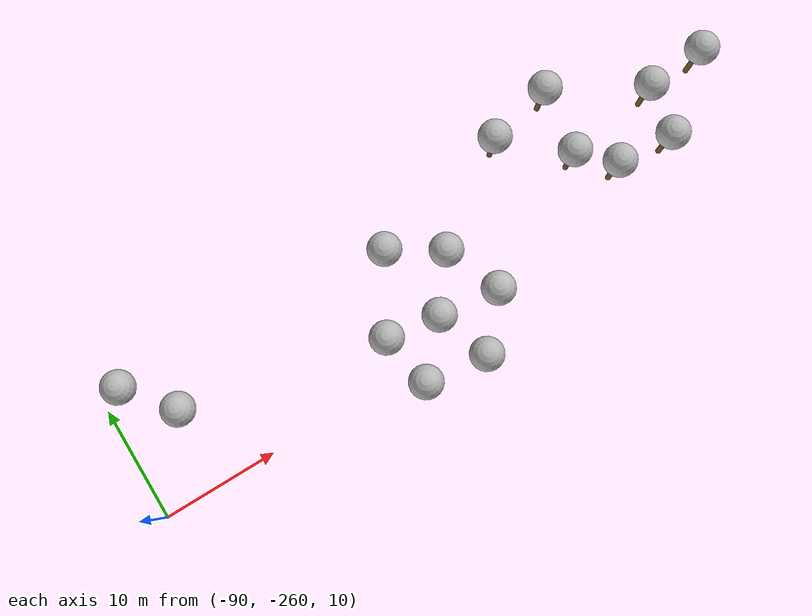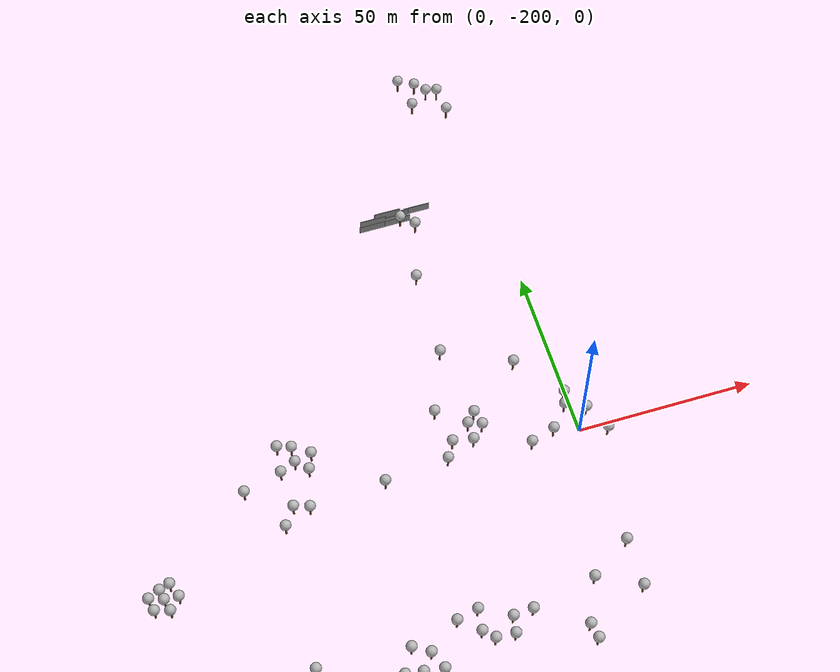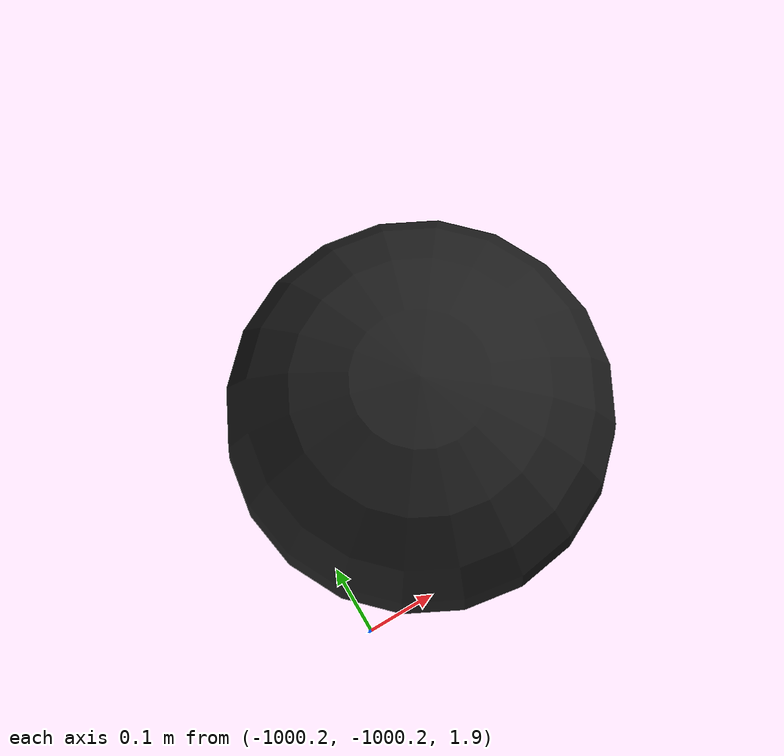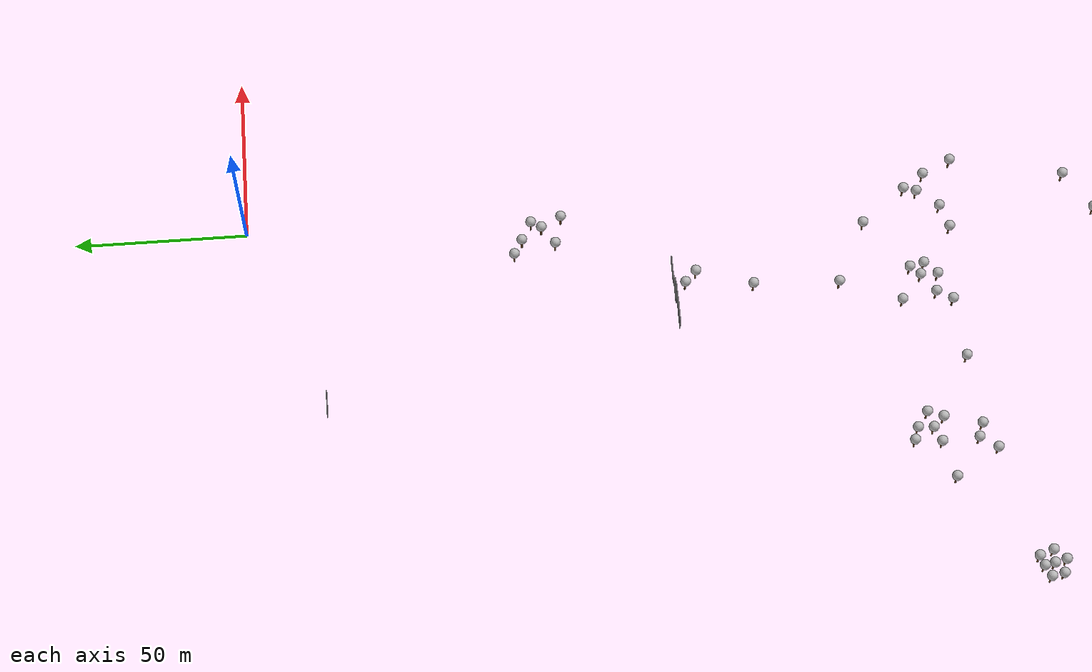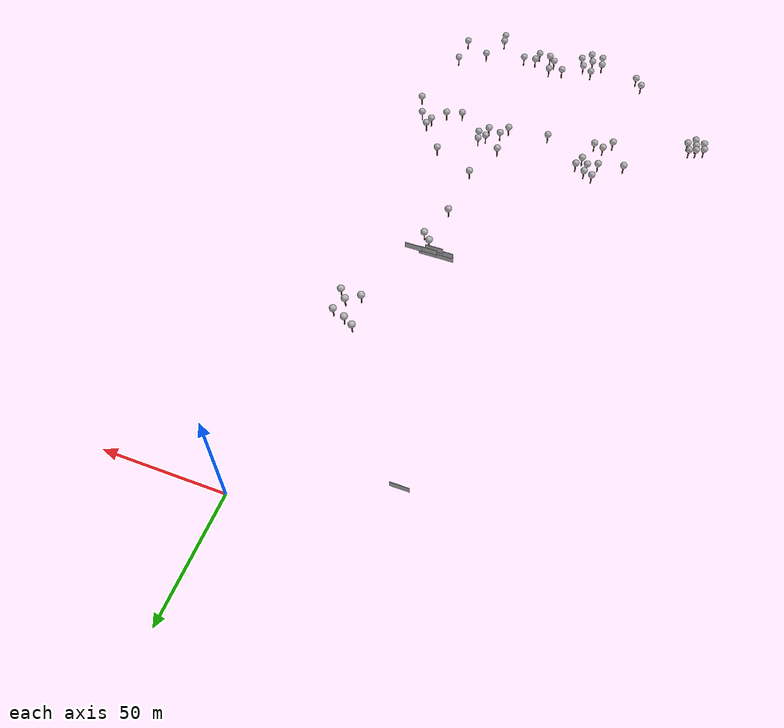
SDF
<sdf version="1.7">
 <world name="default">
  <plugin name="mrs_gazebo_static_transform_republisher_plugin" filename="libMrsGazeboCommonResources_StaticTransformRepublisher.so"/>
  <spherical_coordinates>
   <surface_model>EARTH_WGS84</surface_model>
   <latitude_deg>47.3977</latitude_deg>
   <longitude_deg>8.54559</longitude_deg>
   <elevation>0</elevation>
   <heading_deg>0</heading_deg>
  </spherical_coordinates>
  <physics name="default_physics" default="0" type="ode">
   <ode>
    <solver>
     <type>quick</type>
     <iters>10</iters>
     <sor>1.3</sor>
     <use_dynamic_moi_rescaling>0</use_dynamic_moi_rescaling>
    </solver>
    <constraints>
     <cfm>0</cfm>
     <erp>0.2</erp>
     <contact_max_correcting_vel>1000</contact_max_correcting_vel>
     <contact_surface_layer>0.001</contact_surface_layer>
    </constraints>
   </ode>
   <max_step_size>0.004</max_step_size>
   <real_time_factor>1</real_time_factor>
   <real_time_update_rate>250</real_time_update_rate>
  </physics>
  <scene><shadows>0</shadows><ambient>0.4 0.4 0.4 1</ambient><background>0.7 0.7 0.7 1</background></scene>
  <light name="sun" type="directional">
   <pose>0 0 1000 0.4 0.2 0</pose>
   <diffuse>1 1 1 1</diffuse>
   <specular>0.6 0.6 0.6 1</specular>
   <direction>0.1 0.1 -0.9</direction>
   <attenuation>
    <range>20</range>
    <constant>0.5</constant>
    <linear>0.01</linear>
    <quadratic>0.001</quadratic>
   </attenuation>
   <spot><inner_angle>0</inner_angle><outer_angle>0</outer_angle><falloff>0</falloff></spot>
  </light>
  <model name="the_void">
   <static>1</static>
   <link name="link">
    <pose>0 0 0.1 0 -0 0</pose>
    <visual name="the_void">
     <pose>0 0 2 0 -0 0</pose>
     <geometry><sphere><radius>0.25</radius></sphere></geometry>
     <material>
      <script><uri>file://media/materials/scripts/Gazebo.material</uri><name>Gazebo/Black</name></script>
     </material>
    </visual>
   </link>
   <pose>-1000 -1000 0 0 -0 0</pose>
  </model>
  <plugin name="mrs_gazebo_rviz_cam_synchronizer" filename="libMrsGazeboCommonResources_RvizCameraSynchronizer.so">
   <target_frame_id>gazebo_user_camera</target_frame_id>
   <world_origin_frame_id>uav1/gps_origin</world_origin_frame_id>
   <frame_to_follow>uav1</frame_to_follow>
  </plugin>
  <gravity>0 0 -9.8066</gravity>
  <magnetic_field>6e-06 2.3e-05 -4.2e-05</magnetic_field>
  <atmosphere type="adiabatic"/>
  <model name="tree_simple">
   <static>1</static>
   <link name="link">
    <pose>0 0 0.1 0 -0 0</pose>
    <inertial>
     <mass>666</mass>
     <inertia>
      <ixx>0.0861167</ixx>
      <ixy>0</ixy>
      <ixz>0</ixz>
      <iyy>0.0861167</iyy>
      <iyz>0</iyz>
      <izz>0.0861167</izz>
     </inertia>
    </inertial>
    <collision name="collision_trunk">
     <pose>0 0 2 0 -0 0</pose>
     <geometry><cylinder><radius>0.25</radius><length>4</length></cylinder></geometry>
     <surface>
      <contact>
       <poissons_ratio>0.347</poissons_ratio>
       <elastic_modulus>8.8e+09</elastic_modulus>
       <ode><kp>100000</kp><kd>100</kd><max_vel>100</max_vel><min_depth>0.001</min_depth></ode>
      </contact>
      <friction>
       <torsional>
        <coefficient>1</coefficient>
        <use_patch_radius>0</use_patch_radius>
        <surface_radius>0.01</surface_radius>
       </torsional>
      </friction>
     </surface>
    </collision>
    <collision name="collision_treetop">
     <pose>0 0 5.2 0 -0 0</pose>
     <geometry><sphere><radius>1.5</radius></sphere></geometry>
     <surface>
      <contact>
       <poissons_ratio>0.347</poissons_ratio>
       <elastic_modulus>8.8e+09</elastic_modulus>
       <ode><kp>100000</kp><kd>100</kd><max_vel>100</max_vel><min_depth>0.001</min_depth></ode>
      </contact>
      <friction>
       <torsional>
        <coefficient>1</coefficient>
        <use_patch_radius>0</use_patch_radius>
        <surface_radius>0.01</surface_radius>
       </torsional>
      </friction>
     </surface>
    </collision>
    <visual name="trunk">
     <pose>0 0 2 0 -0 0</pose>
     <geometry><cylinder><radius>0.25</radius><length>4</length></cylinder></geometry>
     <material>
      <script>
       <uri>model://tree_simple/scripts</uri>
       <uri>model://tree_simple/materials/textures</uri>
       <name>TreeSimple/Trunk</name>
      </script>
     </material>
    </visual>
    <visual name="treetop">
     <pose>0 0 5.2 0 -0 0</pose>
     <geometry><sphere><radius>1.5</radius></sphere></geometry>
     <material>
      <script>
       <uri>model://tree_simple/scripts</uri>
       <uri>model://tree_simple/materials/textures</uri>
       <name>TreeSimple/Treetop</name>
      </script>
     </material>
    </visual>
   </link>
   <pose>-14.8583 -77.4349 2.65837 0 -0 0</pose>
  </model>
  <model name="tree_simple_clone">
   <static>1</static>
   <link name="link">
    <pose>0 0 0.1 0 -0 0</pose>
    <inertial>
     <mass>666</mass>
     <inertia>
      <ixx>0.0861167</ixx>
      <ixy>0</ixy>
      <ixz>0</ixz>
      <iyy>0.0861167</iyy>
      <iyz>0</iyz>
      <izz>0.0861167</izz>
     </inertia>
    </inertial>
    <collision name="collision_trunk">
     <pose>0 0 2 0 -0 0</pose>
     <geometry><cylinder><radius>0.25</radius><length>4</length></cylinder></geometry>
     <surface>
      <contact>
       <poissons_ratio>0.347</poissons_ratio>
       <elastic_modulus>8.8e+09</elastic_modulus>
       <ode><kp>100000</kp><kd>100</kd><max_vel>100</max_vel><min_depth>0.001</min_depth></ode>
      </contact>
      <friction>
       <torsional>
        <coefficient>1</coefficient>
        <use_patch_radius>0</use_patch_radius>
        <surface_radius>0.01</surface_radius>
       </torsional>
      </friction>
     </surface>
    </collision>
    <collision name="collision_treetop">
     <pose>0 0 5.2 0 -0 0</pose>
     <geometry><sphere><radius>1.5</radius></sphere></geometry>
     <surface>
      <contact>
       <poissons_ratio>0.347</poissons_ratio>
       <elastic_modulus>8.8e+09</elastic_modulus>
       <ode><kp>100000</kp><kd>100</kd><max_vel>100</max_vel><min_depth>0.001</min_depth></ode>
      </contact>
      <friction>
       <torsional>
        <coefficient>1</coefficient>
        <use_patch_radius>0</use_patch_radius>
        <surface_radius>0.01</surface_radius>
       </torsional>
      </friction>
     </surface>
    </collision>
    <visual name="trunk">
     <pose>0 0 2 0 -0 0</pose>
     <geometry><cylinder><radius>0.25</radius><length>4</length></cylinder></geometry>
     <material>
      <script>
       <uri>model://tree_simple/scripts</uri>
       <uri>model://tree_simple/materials/textures</uri>
       <name>TreeSimple/Trunk</name>
      </script>
     </material>
    </visual>
    <visual name="treetop">
     <pose>0 0 5.2 0 -0 0</pose>
     <geometry><sphere><radius>1.5</radius></sphere></geometry>
     <material>
      <script>
       <uri>model://tree_simple/scripts</uri>
       <uri>model://tree_simple/materials/textures</uri>
       <name>TreeSimple/Treetop</name>
      </script>
     </material>
    </visual>
   </link>
   <pose>-10.5024 -79.8582 2.65837 0 -0 0</pose>
  </model>
  <model name="tree_simple_clone_clone">
   <static>1</static>
   <link name="link">
    <pose>0 0 0.1 0 -0 0</pose>
    <inertial>
     <mass>666</mass>
     <inertia>
      <ixx>0.0861167</ixx>
      <ixy>0</ixy>
      <ixz>0</ixz>
      <iyy>0.0861167</iyy>
      <iyz>0</iyz>
      <izz>0.0861167</izz>
     </inertia>
    </inertial>
    <collision name="collision_trunk">
     <pose>0 0 2 0 -0 0</pose>
     <geometry><cylinder><radius>0.25</radius><length>4</length></cylinder></geometry>
     <surface>
      <contact>
       <poissons_ratio>0.347</poissons_ratio>
       <elastic_modulus>8.8e+09</elastic_modulus>
       <ode><kp>100000</kp><kd>100</kd><max_vel>100</max_vel><min_depth>0.001</min_depth></ode>
      </contact>
      <friction>
       <torsional>
        <coefficient>1</coefficient>
        <use_patch_radius>0</use_patch_radius>
        <surface_radius>0.01</surface_radius>
       </torsional>
      </friction>
     </surface>
    </collision>
    <collision name="collision_treetop">
     <pose>0 0 5.2 0 -0 0</pose>
     <geometry><sphere><radius>1.5</radius></sphere></geometry>
     <surface>
      <contact>
       <poissons_ratio>0.347</poissons_ratio>
       <elastic_modulus>8.8e+09</elastic_modulus>
       <ode><kp>100000</kp><kd>100</kd><max_vel>100</max_vel><min_depth>0.001</min_depth></ode>
      </contact>
      <friction>
       <torsional>
        <coefficient>1</coefficient>
        <use_patch_radius>0</use_patch_radius>
        <surface_radius>0.01</surface_radius>
       </torsional>
      </friction>
     </surface>
    </collision>
    <visual name="trunk">
     <pose>0 0 2 0 -0 0</pose>
     <geometry><cylinder><radius>0.25</radius><length>4</length></cylinder></geometry>
     <material>
      <script>
       <uri>model://tree_simple/scripts</uri>
       <uri>model://tree_simple/materials/textures</uri>
       <name>TreeSimple/Trunk</name>
      </script>
     </material>
    </visual>
    <visual name="treetop">
     <pose>0 0 5.2 0 -0 0</pose>
     <geometry><sphere><radius>1.5</radius></sphere></geometry>
     <material>
      <script>
       <uri>model://tree_simple/scripts</uri>
       <uri>model://tree_simple/materials/textures</uri>
       <name>TreeSimple/Treetop</name>
      </script>
     </material>
    </visual>
   </link>
   <pose>-13.9981 -89.3129 6.52166 0 -0 0</pose>
  </model>
  <model name="tree_simple_clone_clone_clone">
   <static>1</static>
   <link name="link">
    <pose>0 0 0.1 0 -0 0</pose>
    <inertial>
     <mass>666</mass>
     <inertia>
      <ixx>0.0861167</ixx>
      <ixy>0</ixy>
      <ixz>0</ixz>
      <iyy>0.0861167</iyy>
      <iyz>0</iyz>
      <izz>0.0861167</izz>
     </inertia>
    </inertial>
    <collision name="collision_trunk">
     <pose>0 0 2 0 -0 0</pose>
     <geometry><cylinder><radius>0.25</radius><length>4</length></cylinder></geometry>
     <surface>
      <contact>
       <poissons_ratio>0.347</poissons_ratio>
       <elastic_modulus>8.8e+09</elastic_modulus>
       <ode><kp>100000</kp><kd>100</kd><max_vel>100</max_vel><min_depth>0.001</min_depth></ode>
      </contact>
      <friction>
       <torsional>
        <coefficient>1</coefficient>
        <use_patch_radius>0</use_patch_radius>
        <surface_radius>0.01</surface_radius>
       </torsional>
      </friction>
     </surface>
    </collision>
    <collision name="collision_treetop">
     <pose>0 0 5.2 0 -0 0</pose>
     <geometry><sphere><radius>1.5</radius></sphere></geometry>
     <surface>
      <contact>
       <poissons_ratio>0.347</poissons_ratio>
       <elastic_modulus>8.8e+09</elastic_modulus>
       <ode><kp>100000</kp><kd>100</kd><max_vel>100</max_vel><min_depth>0.001</min_depth></ode>
      </contact>
      <friction>
       <torsional>
        <coefficient>1</coefficient>
        <use_patch_radius>0</use_patch_radius>
        <surface_radius>0.01</surface_radius>
       </torsional>
      </friction>
     </surface>
    </collision>
    <visual name="trunk">
     <pose>0 0 2 0 -0 0</pose>
     <geometry><cylinder><radius>0.25</radius><length>4</length></cylinder></geometry>
     <material>
      <script>
       <uri>model://tree_simple/scripts</uri>
       <uri>model://tree_simple/materials/textures</uri>
       <name>TreeSimple/Trunk</name>
      </script>
     </material>
    </visual>
    <visual name="treetop">
     <pose>0 0 5.2 0 -0 0</pose>
     <geometry><sphere><radius>1.5</radius></sphere></geometry>
     <material>
      <script>
       <uri>model://tree_simple/scripts</uri>
       <uri>model://tree_simple/materials/textures</uri>
       <name>TreeSimple/Treetop</name>
      </script>
     </material>
    </visual>
   </link>
   <pose>-8.68555 -85.6352 6.52166 0 -0 0</pose>
  </model>
  <model name="tree_simple_clone_clone_clone_0">
   <static>1</static>
   <link name="link">
    <pose>0 0 0.1 0 -0 0</pose>
    <inertial>
     <mass>666</mass>
     <inertia>
      <ixx>0.0861167</ixx>
      <ixy>0</ixy>
      <ixz>0</ixz>
      <iyy>0.0861167</iyy>
      <iyz>0</iyz>
      <izz>0.0861167</izz>
     </inertia>
    </inertial>
    <collision name="collision_trunk">
     <pose>0 0 2 0 -0 0</pose>
     <geometry><cylinder><radius>0.25</radius><length>4</length></cylinder></geometry>
     <surface>
      <contact>
       <poissons_ratio>0.347</poissons_ratio>
       <elastic_modulus>8.8e+09</elastic_modulus>
       <ode><kp>100000</kp><kd>100</kd><max_vel>100</max_vel><min_depth>0.001</min_depth></ode>
      </contact>
      <friction>
       <torsional>
        <coefficient>1</coefficient>
        <use_patch_radius>0</use_patch_radius>
        <surface_radius>0.01</surface_radius>
       </torsional>
      </friction>
     </surface>
    </collision>
    <collision name="collision_treetop">
     <pose>0 0 5.2 0 -0 0</pose>
     <geometry><sphere><radius>1.5</radius></sphere></geometry>
     <surface>
      <contact>
       <poissons_ratio>0.347</poissons_ratio>
       <elastic_modulus>8.8e+09</elastic_modulus>
       <ode><kp>100000</kp><kd>100</kd><max_vel>100</max_vel><min_depth>0.001</min_depth></ode>
      </contact>
      <friction>
       <torsional>
        <coefficient>1</coefficient>
        <use_patch_radius>0</use_patch_radius>
        <surface_radius>0.01</surface_radius>
       </torsional>
      </friction>
     </surface>
    </collision>
    <visual name="trunk">
     <pose>0 0 2 0 -0 0</pose>
     <geometry><cylinder><radius>0.25</radius><length>4</length></cylinder></geometry>
     <material>
      <script>
       <uri>model://tree_simple/scripts</uri>
       <uri>model://tree_simple/materials/textures</uri>
       <name>TreeSimple/Trunk</name>
      </script>
     </material>
    </visual>
    <visual name="treetop">
     <pose>0 0 5.2 0 -0 0</pose>
     <geometry><sphere><radius>1.5</radius></sphere></geometry>
     <material>
      <script>
       <uri>model://tree_simple/scripts</uri>
       <uri>model://tree_simple/materials/textures</uri>
       <name>TreeSimple/Treetop</name>
      </script>
     </material>
    </visual>
   </link>
   <pose>-4.38555 -82.8281 1.43203 0 -0 0</pose>
  </model>
  <model name="tree_simple_clone_clone_clone_1">
   <static>1</static>
   <link name="link">
    <pose>0 0 0.1 0 -0 0</pose>
    <inertial>
     <mass>666</mass>
     <inertia>
      <ixx>0.0861167</ixx>
      <ixy>0</ixy>
      <ixz>0</ixz>
      <iyy>0.0861167</iyy>
      <iyz>0</iyz>
      <izz>0.0861167</izz>
     </inertia>
    </inertial>
    <collision name="collision_trunk">
     <pose>0 0 2 0 -0 0</pose>
     <geometry><cylinder><radius>0.25</radius><length>4</length></cylinder></geometry>
     <surface>
      <contact>
       <poissons_ratio>0.347</poissons_ratio>
       <elastic_modulus>8.8e+09</elastic_modulus>
       <ode><kp>100000</kp><kd>100</kd><max_vel>100</max_vel><min_depth>0.001</min_depth></ode>
      </contact>
      <friction>
       <torsional>
        <coefficient>1</coefficient>
        <use_patch_radius>0</use_patch_radius>
        <surface_radius>0.01</surface_radius>
       </torsional>
      </friction>
     </surface>
    </collision>
    <collision name="collision_treetop">
     <pose>0 0 5.2 0 -0 0</pose>
     <geometry><sphere><radius>1.5</radius></sphere></geometry>
     <surface>
      <contact>
       <poissons_ratio>0.347</poissons_ratio>
       <elastic_modulus>8.8e+09</elastic_modulus>
       <ode><kp>100000</kp><kd>100</kd><max_vel>100</max_vel><min_depth>0.001</min_depth></ode>
      </contact>
      <friction>
       <torsional>
        <coefficient>1</coefficient>
        <use_patch_radius>0</use_patch_radius>
        <surface_radius>0.01</surface_radius>
       </torsional>
      </friction>
     </surface>
    </collision>
    <visual name="trunk">
     <pose>0 0 2 0 -0 0</pose>
     <geometry><cylinder><radius>0.25</radius><length>4</length></cylinder></geometry>
     <material>
      <script>
       <uri>model://tree_simple/scripts</uri>
       <uri>model://tree_simple/materials/textures</uri>
       <name>TreeSimple/Trunk</name>
      </script>
     </material>
    </visual>
    <visual name="treetop">
     <pose>0 0 5.2 0 -0 0</pose>
     <geometry><sphere><radius>1.5</radius></sphere></geometry>
     <material>
      <script>
       <uri>model://tree_simple/scripts</uri>
       <uri>model://tree_simple/materials/textures</uri>
       <name>TreeSimple/Treetop</name>
      </script>
     </material>
    </visual>
   </link>
   <pose>-4.13426 -91.5385 3.4407 0 -0 0</pose>
  </model>
  <light name="user_point_light_0" type="point">
   <pose>-28.2042 -88.5327 1 0 -0 0</pose>
   <diffuse>0.5 0.5 0.5 1</diffuse>
   <specular>0.1 0.1 0.1 1</specular>
   <attenuation>
    <range>20</range>
    <constant>0.5</constant>
    <linear>0.01</linear>
    <quadratic>0.001</quadratic>
   </attenuation>
   <cast_shadows>0</cast_shadows>
   <direction>0 0 -1</direction>
   <spot><inner_angle>0</inner_angle><outer_angle>0</outer_angle><falloff>0</falloff></spot>
  </light>
  <light name="user_point_light_0_clone" type="point">
   <pose>-24.6017 -97.8932 5.06114 0 -0 0</pose>
   <diffuse>0.5 0.5 0.5 1</diffuse>
   <specular>0.1 0.1 0.1 1</specular>
   <direction>0 0 -1</direction>
   <attenuation>
    <range>20</range>
    <constant>0.5</constant>
    <linear>0.01</linear>
    <quadratic>0.001</quadratic>
   </attenuation>
   <cast_shadows>0</cast_shadows>
   <spot><inner_angle>0</inner_angle><outer_angle>0</outer_angle><falloff>0</falloff></spot>
  </light>
  <light name="user_point_light_0_clone_0" type="point">
   <pose>-36.8154 -121.422 5.06114 0 -0 0</pose>
   <diffuse>0.5 0.5 0.5 1</diffuse>
   <specular>0.1 0.1 0.1 1</specular>
   <direction>0 0 -1</direction>
   <attenuation>
    <range>20</range>
    <constant>0.5</constant>
    <linear>0.01</linear>
    <quadratic>0.001</quadratic>
   </attenuation>
   <cast_shadows>0</cast_shadows>
   <spot><inner_angle>0</inner_angle><outer_angle>0</outer_angle><falloff>0</falloff></spot>
  </light>
  <light name="user_point_light_0_clone_1" type="point">
   <pose>-36.8589 -115.31 5.06114 0 -0 0</pose>
   <diffuse>0.5 0.5 0.5 1</diffuse>
   <specular>0.1 0.1 0.1 1</specular>
   <direction>0 0 -1</direction>
   <attenuation>
    <range>20</range>
    <constant>0.5</constant>
    <linear>0.01</linear>
    <quadratic>0.001</quadratic>
   </attenuation>
   <cast_shadows>0</cast_shadows>
   <spot><inner_angle>0</inner_angle><outer_angle>0</outer_angle><falloff>0</falloff></spot>
  </light>
  <light name="user_point_light_0_clone_2" type="point">
   <pose>-26.9238 -122.652 5.06114 0 -0 0</pose>
   <diffuse>0.5 0.5 0.5 1</diffuse>
   <specular>0.1 0.1 0.1 1</specular>
   <direction>0 0 -1</direction>
   <attenuation>
    <range>20</range>
    <constant>0.5</constant>
    <linear>0.01</linear>
    <quadratic>0.001</quadratic>
   </attenuation>
   <cast_shadows>0</cast_shadows>
   <spot><inner_angle>0</inner_angle><outer_angle>0</outer_angle><falloff>0</falloff></spot>
  </light>
  <light name="user_point_light_0_clone_3" type="point">
   <pose>-35.9856 -150.691 5.06114 0 -0 0</pose>
   <diffuse>0.5 0.5 0.5 1</diffuse>
   <specular>0.1 0.1 0.1 1</specular>
   <direction>0 0 -1</direction>
   <attenuation>
    <range>20</range>
    <constant>0.5</constant>
    <linear>0.01</linear>
    <quadratic>0.001</quadratic>
   </attenuation>
   <cast_shadows>0</cast_shadows>
   <spot><inner_angle>0</inner_angle><outer_angle>0</outer_angle><falloff>0</falloff></spot>
  </light>
  <light name="user_point_light_0_clone_3_clone" type="point">
   <pose>-19.0277 -155.283 6.2099 0 -0 0</pose>
   <diffuse>0.5 0.5 0.5 1</diffuse>
   <specular>0.1 0.1 0.1 1</specular>
   <direction>0 0 -1</direction>
   <attenuation>
    <range>20</range>
    <constant>0.5</constant>
    <linear>0.01</linear>
    <quadratic>0.001</quadratic>
   </attenuation>
   <cast_shadows>0</cast_shadows>
   <spot><inner_angle>0</inner_angle><outer_angle>0</outer_angle><falloff>0</falloff></spot>
  </light>
  <light name="user_point_light_0_clone_3_clone_0" type="point">
   <pose>-16.9619 -192.764 6.2099 0 -0 0</pose>
   <diffuse>0.5 0.5 0.5 1</diffuse>
   <specular>0.1 0.1 0.1 1</specular>
   <direction>0 0 -1</direction>
   <attenuation>
    <range>20</range>
    <constant>0.5</constant>
    <linear>0.01</linear>
    <quadratic>0.001</quadratic>
   </attenuation>
   <cast_shadows>0</cast_shadows>
   <spot><inner_angle>0</inner_angle><outer_angle>0</outer_angle><falloff>0</falloff></spot>
  </light>
  <light name="user_point_light_0_clone_3_clone_1" type="point">
   <pose>-17.1098 -195.583 6.2099 0 -0 0</pose>
   <diffuse>0.5 0.5 0.5 1</diffuse>
   <specular>0.1 0.1 0.1 1</specular>
   <direction>0 0 -1</direction>
   <attenuation>
    <range>20</range>
    <constant>0.5</constant>
    <linear>0.01</linear>
    <quadratic>0.001</quadratic>
   </attenuation>
   <cast_shadows>0</cast_shadows>
   <spot><inner_angle>0</inner_angle><outer_angle>0</outer_angle><falloff>0</falloff></spot>
  </light>
  <light name="user_point_light_0_clone_3_clone_2" type="point">
   <pose>-31.6665 -180.812 6.2099 0 -0 0</pose>
   <diffuse>0.5 0.5 0.5 1</diffuse>
   <specular>0.1 0.1 0.1 1</specular>
   <direction>0 0 -1</direction>
   <attenuation>
    <range>20</range>
    <constant>0.5</constant>
    <linear>0.01</linear>
    <quadratic>0.001</quadratic>
   </attenuation>
   <cast_shadows>0</cast_shadows>
   <spot><inner_angle>0</inner_angle><outer_angle>0</outer_angle><falloff>0</falloff></spot>
  </light>
  <light name="user_point_light_0_clone_3_clone_3" type="point">
   <pose>-44.0178 -195.517 6.2099 0 -0 0</pose>
   <diffuse>0.5 0.5 0.5 1</diffuse>
   <specular>0.1 0.1 0.1 1</specular>
   <direction>0 0 -1</direction>
   <attenuation>
    <range>20</range>
    <constant>0.5</constant>
    <linear>0.01</linear>
    <quadratic>0.001</quadratic>
   </attenuation>
   <cast_shadows>0</cast_shadows>
   <spot><inner_angle>0</inner_angle><outer_angle>0</outer_angle><falloff>0</falloff></spot>
  </light>
  <light name="user_point_light_0_clone_3_clone_4" type="point">
   <pose>-66.4909 -204.295 6.2099 0 -0 0</pose>
   <diffuse>0.5 0.5 0.5 1</diffuse>
   <specular>0.1 0.1 0.1 1</specular>
   <direction>0 0 -1</direction>
   <attenuation>
    <range>20</range>
    <constant>0.5</constant>
    <linear>0.01</linear>
    <quadratic>0.001</quadratic>
   </attenuation>
   <cast_shadows>0</cast_shadows>
   <spot><inner_angle>0</inner_angle><outer_angle>0</outer_angle><falloff>0</falloff></spot>
  </light>
  <light name="user_point_light_0_clone_3_clone_5" type="point">
   <pose>-67.7515 -205.576 6.2099 0 -0 0</pose>
   <diffuse>0.5 0.5 0.5 1</diffuse>
   <specular>0.1 0.1 0.1 1</specular>
   <direction>0 0 -1</direction>
   <attenuation>
    <range>20</range>
    <constant>0.5</constant>
    <linear>0.01</linear>
    <quadratic>0.001</quadratic>
   </attenuation>
   <cast_shadows>0</cast_shadows>
   <spot><inner_angle>0</inner_angle><outer_angle>0</outer_angle><falloff>0</falloff></spot>
  </light>
  <light name="user_point_light_0_clone_3_clone_6" type="point">
   <pose>-88.674 -185.898 6.2099 0 -0 0</pose>
   <diffuse>0.5 0.5 0.5 1</diffuse>
   <specular>0.1 0.1 0.1 1</specular>
   <direction>0 0 -1</direction>
   <attenuation>
    <range>20</range>
    <constant>0.5</constant>
    <linear>0.01</linear>
    <quadratic>0.001</quadratic>
   </attenuation>
   <cast_shadows>0</cast_shadows>
   <spot><inner_angle>0</inner_angle><outer_angle>0</outer_angle><falloff>0</falloff></spot>
  </light>
  <light name="user_point_light_0_clone_3_clone_7" type="point">
   <pose>-82.7977 -170.948 6.2099 0 -0 0</pose>
   <diffuse>0.5 0.5 0.5 1</diffuse>
   <specular>0.1 0.1 0.1 1</specular>
   <direction>0 0 -1</direction>
   <attenuation>
    <range>20</range>
    <constant>0.5</constant>
    <linear>0.01</linear>
    <quadratic>0.001</quadratic>
   </attenuation>
   <cast_shadows>0</cast_shadows>
   <spot><inner_angle>0</inner_angle><outer_angle>0</outer_angle><falloff>0</falloff></spot>
  </light>
  <light name="user_point_light_0_clone_3_clone_7_clone" type="point">
   <pose>-67.0058 -157.305 7.47363 0 -0 0</pose>
   <diffuse>0.5 0.5 0.5 1</diffuse>
   <specular>0.1 0.1 0.1 1</specular>
   <direction>0 0 -1</direction>
   <attenuation>
    <range>20</range>
    <constant>0.5</constant>
    <linear>0.01</linear>
    <quadratic>0.001</quadratic>
   </attenuation>
   <cast_shadows>0</cast_shadows>
   <spot><inner_angle>0</inner_angle><outer_angle>0</outer_angle><falloff>0</falloff></spot>
  </light>
  <light name="user_point_light_0_clone_3_clone_7_clone_0" type="point">
   <pose>-80.8425 -206.294 7.47363 0 -0 0</pose>
   <diffuse>0.5 0.5 0.5 1</diffuse>
   <specular>0.1 0.1 0.1 1</specular>
   <direction>0 0 -1</direction>
   <attenuation>
    <range>20</range>
    <constant>0.5</constant>
    <linear>0.01</linear>
    <quadratic>0.001</quadratic>
   </attenuation>
   <cast_shadows>0</cast_shadows>
   <spot><inner_angle>0</inner_angle><outer_angle>0</outer_angle><falloff>0</falloff></spot>
  </light>
  <light name="user_point_light_0_clone_3_clone_7_clone_1" type="point">
   <pose>-80.593 -206.745 7.47363 0 -0 0</pose>
   <diffuse>0.5 0.5 0.5 1</diffuse>
   <specular>0.1 0.1 0.1 1</specular>
   <direction>0 0 -1</direction>
   <attenuation>
    <range>20</range>
    <constant>0.5</constant>
    <linear>0.01</linear>
    <quadratic>0.001</quadratic>
   </attenuation>
   <cast_shadows>0</cast_shadows>
   <spot><inner_angle>0</inner_angle><outer_angle>0</outer_angle><falloff>0</falloff></spot>
  </light>
  <light name="user_point_light_0_clone_3_clone_7_clone_2" type="point">
   <pose>-98.6647 -215.591 7.47363 0 -0 0</pose>
   <diffuse>0.5 0.5 0.5 1</diffuse>
   <specular>0.1 0.1 0.1 1</specular>
   <direction>0 0 -1</direction>
   <attenuation>
    <range>20</range>
    <constant>0.5</constant>
    <linear>0.01</linear>
    <quadratic>0.001</quadratic>
   </attenuation>
   <cast_shadows>0</cast_shadows>
   <spot><inner_angle>0</inner_angle><outer_angle>0</outer_angle><falloff>0</falloff></spot>
  </light>
  <light name="user_point_light_0_clone_3_clone_7_clone_3" type="point">
   <pose>-116.327 -208.024 7.47363 0 -0 0</pose>
   <diffuse>0.5 0.5 0.5 1</diffuse>
   <specular>0.1 0.1 0.1 1</specular>
   <direction>0 0 -1</direction>
   <attenuation>
    <range>20</range>
    <constant>0.5</constant>
    <linear>0.01</linear>
    <quadratic>0.001</quadratic>
   </attenuation>
   <cast_shadows>0</cast_shadows>
   <spot><inner_angle>0</inner_angle><outer_angle>0</outer_angle><falloff>0</falloff></spot>
  </light>
  <light name="user_point_light_0_clone_3_clone_7_clone_4" type="point">
   <pose>-123.432 -234.216 7.47363 0 -0 0</pose>
   <diffuse>0.5 0.5 0.5 1</diffuse>
   <specular>0.1 0.1 0.1 1</specular>
   <direction>0 0 -1</direction>
   <attenuation>
    <range>20</range>
    <constant>0.5</constant>
    <linear>0.01</linear>
    <quadratic>0.001</quadratic>
   </attenuation>
   <cast_shadows>0</cast_shadows>
   <spot><inner_angle>0</inner_angle><outer_angle>0</outer_angle><falloff>0</falloff></spot>
  </light>
  <light name="user_point_light_0_clone_3_clone_7_clone_5" type="point">
   <pose>-109.213 -253.892 7.47363 0 -0 0</pose>
   <diffuse>0.5 0.5 0.5 1</diffuse>
   <specular>0.1 0.1 0.1 1</specular>
   <direction>0 0 -1</direction>
   <attenuation>
    <range>20</range>
    <constant>0.5</constant>
    <linear>0.01</linear>
    <quadratic>0.001</quadratic>
   </attenuation>
   <cast_shadows>0</cast_shadows>
   <spot><inner_angle>0</inner_angle><outer_angle>0</outer_angle><falloff>0</falloff></spot>
  </light>
  <light name="user_point_light_0_clone_3_clone_7_clone_6" type="point">
   <pose>-101.212 -255.509 7.47363 0 -0 0</pose>
   <diffuse>0.5 0.5 0.5 1</diffuse>
   <specular>0.1 0.1 0.1 1</specular>
   <direction>0 0 -1</direction>
   <attenuation>
    <range>20</range>
    <constant>0.5</constant>
    <linear>0.01</linear>
    <quadratic>0.001</quadratic>
   </attenuation>
   <cast_shadows>0</cast_shadows>
   <spot><inner_angle>0</inner_angle><outer_angle>0</outer_angle><falloff>0</falloff></spot>
  </light>
  <light name="user_point_light_0_clone_3_clone_7_clone_6_clone" type="point">
   <pose>-77.215 -264.385 9.16416 0 -0 0</pose>
   <diffuse>0.5 0.5 0.5 1</diffuse>
   <specular>0.1 0.1 0.1 1</specular>
   <direction>0 0 -1</direction>
   <attenuation>
    <range>20</range>
    <constant>0.5</constant>
    <linear>0.01</linear>
    <quadratic>0.001</quadratic>
   </attenuation>
   <cast_shadows>0</cast_shadows>
   <spot><inner_angle>0</inner_angle><outer_angle>0</outer_angle><falloff>0</falloff></spot>
  </light>
  <light name="user_point_light_0_clone_3_clone_7_clone_6_clone_0" type="point">
   <pose>-42.477 -246.092 9.16416 0 -0 0</pose>
   <diffuse>0.5 0.5 0.5 1</diffuse>
   <specular>0.1 0.1 0.1 1</specular>
   <direction>0 0 -1</direction>
   <attenuation>
    <range>20</range>
    <constant>0.5</constant>
    <linear>0.01</linear>
    <quadratic>0.001</quadratic>
   </attenuation>
   <cast_shadows>0</cast_shadows>
   <spot><inner_angle>0</inner_angle><outer_angle>0</outer_angle><falloff>0</falloff></spot>
  </light>
  <light name="user_point_light_0_clone_3_clone_7_clone_6_clone_1" type="point">
   <pose>-41.1209 -245.259 9.16416 0 -0 0</pose>
   <diffuse>0.5 0.5 0.5 1</diffuse>
   <specular>0.1 0.1 0.1 1</specular>
   <direction>0 0 -1</direction>
   <attenuation>
    <range>20</range>
    <constant>0.5</constant>
    <linear>0.01</linear>
    <quadratic>0.001</quadratic>
   </attenuation>
   <cast_shadows>0</cast_shadows>
   <spot><inner_angle>0</inner_angle><outer_angle>0</outer_angle><falloff>0</falloff></spot>
  </light>
  <light name="user_point_light_0_clone_3_clone_7_clone_6_clone_2" type="point">
   <pose>-35.0223 -264.542 9.16416 0 -0 0</pose>
   <diffuse>0.5 0.5 0.5 1</diffuse>
   <specular>0.1 0.1 0.1 1</specular>
   <direction>0 0 -1</direction>
   <attenuation>
    <range>20</range>
    <constant>0.5</constant>
    <linear>0.01</linear>
    <quadratic>0.001</quadratic>
   </attenuation>
   <cast_shadows>0</cast_shadows>
   <spot><inner_angle>0</inner_angle><outer_angle>0</outer_angle><falloff>0</falloff></spot>
  </light>
  <light name="user_point_light_0_clone_3_clone_7_clone_6_clone_3" type="point">
   <pose>-7.7167 -251.438 9.16416 0 -0 0</pose>
   <diffuse>0.5 0.5 0.5 1</diffuse>
   <specular>0.1 0.1 0.1 1</specular>
   <direction>0 0 -1</direction>
   <attenuation>
    <range>20</range>
    <constant>0.5</constant>
    <linear>0.01</linear>
    <quadratic>0.001</quadratic>
   </attenuation>
   <cast_shadows>0</cast_shadows>
   <spot><inner_angle>0</inner_angle><outer_angle>0</outer_angle><falloff>0</falloff></spot>
  </light>
  <light name="user_point_light_0_clone_3_clone_7_clone_6_clone_4" type="point">
   <pose>9.93738 -221.752 9.16416 0 -0 0</pose>
   <diffuse>0.5 0.5 0.5 1</diffuse>
   <specular>0.1 0.1 0.1 1</specular>
   <direction>0 0 -1</direction>
   <attenuation>
    <range>20</range>
    <constant>0.5</constant>
    <linear>0.01</linear>
    <quadratic>0.001</quadratic>
   </attenuation>
   <cast_shadows>0</cast_shadows>
   <spot><inner_angle>0</inner_angle><outer_angle>0</outer_angle><falloff>0</falloff></spot>
  </light>
  <light name="user_point_light_0_clone_3_clone_7_clone_6_clone_5" type="point">
   <pose>-3.75027 -187.977 9.16416 0 -0 0</pose>
   <diffuse>0.5 0.5 0.5 1</diffuse>
   <specular>0.1 0.1 0.1 1</specular>
   <direction>0 0 -1</direction>
   <attenuation>
    <range>20</range>
    <constant>0.5</constant>
    <linear>0.01</linear>
    <quadratic>0.001</quadratic>
   </attenuation>
   <cast_shadows>0</cast_shadows>
   <spot><inner_angle>0</inner_angle><outer_angle>0</outer_angle><falloff>0</falloff></spot>
  </light>
  <light name="user_point_light_1" type="point">
   <pose>-9.7614 -69.1698 1 0 -0 0</pose>
   <diffuse>0.5 0.5 0.5 1</diffuse>
   <specular>0.1 0.1 0.1 1</specular>
   <attenuation>
    <range>20</range>
    <constant>0.5</constant>
    <linear>0.01</linear>
    <quadratic>0.001</quadratic>
   </attenuation>
   <cast_shadows>0</cast_shadows>
   <direction>0 0 -1</direction>
   <spot><inner_angle>0</inner_angle><outer_angle>0</outer_angle><falloff>0</falloff></spot>
  </light>
  <light name="user_point_light_1_clone" type="point">
   <pose>-16.1409 -74.3403 4.03149 0 -0 0</pose>
   <diffuse>0.5 0.5 0.5 1</diffuse>
   <specular>0.1 0.1 0.1 1</specular>
   <direction>0 0 -1</direction>
   <attenuation>
    <range>20</range>
    <constant>0.5</constant>
    <linear>0.01</linear>
    <quadratic>0.001</quadratic>
   </attenuation>
   <cast_shadows>0</cast_shadows>
   <spot><inner_angle>0</inner_angle><outer_angle>0</outer_angle><falloff>0</falloff></spot>
  </light>
  <model name="grey_wall">
   <static>1</static>
   <link name="link">
    <pose>0 0 1.4 0 -0 0</pose>
    <collision name="collision"><geometry><box><size>7.5 0.2 2.8</size></box></geometry></collision>
    <visual name="visual">
     <cast_shadows>0</cast_shadows>
     <geometry><box><size>7.5 0.2 2.8</size></box></geometry>
     <material>
      <script>
       <uri>model://grey_wall/materials/scripts</uri>
       <uri>model://grey_wall/materials/textures</uri>
       <name>vrc/grey_wall</name>
      </script>
     </material>
    </visual>
   </link>
   <pose>-28.7982 -123.213 3.76333 0 -0 0</pose>
  </model>
  <model name="grey_wall_clone">
   <static>1</static>
   <link name="link">
    <pose>0 0 1.4 0 -0 0</pose>
    <collision name="collision"><geometry><box><size>7.5 0.2 2.8</size></box></geometry></collision>
    <visual name="visual">
     <cast_shadows>0</cast_shadows>
     <geometry><box><size>7.5 0.2 2.8</size></box></geometry>
     <material>
      <script>
       <uri>model://grey_wall/materials/scripts</uri>
       <uri>model://grey_wall/materials/textures</uri>
       <name>vrc/grey_wall</name>
      </script>
     </material>
    </visual>
   </link>
   <pose>-36.2889 -123.278 3.76333 0 -0 0</pose>
  </model>
  <model name="grey_wall_clone_0">
   <static>1</static>
   <link name="link">
    <pose>0 0 1.4 0 -0 0</pose>
    <collision name="collision"><geometry><box><size>7.5 0.2 2.8</size></box></geometry></collision>
    <visual name="visual">
     <cast_shadows>0</cast_shadows>
     <geometry><box><size>7.5 0.2 2.8</size></box></geometry>
     <material>
      <script>
       <uri>model://grey_wall/materials/scripts</uri>
       <uri>model://grey_wall/materials/textures</uri>
       <name>vrc/grey_wall</name>
      </script>
     </material>
    </visual>
   </link>
   <pose>-36.0705 -123.228 6.22335 0 -0 0</pose>
  </model>
  <model name="grey_wall_clone_1">
   <static>1</static>
   <link name="link">
    <pose>0 0 1.4 0 -0 0</pose>
    <collision name="collision"><geometry><box><size>7.5 0.2 2.8</size></box></geometry></collision>
    <visual name="visual">
     <cast_shadows>0</cast_shadows>
     <geometry><box><size>7.5 0.2 2.8</size></box></geometry>
     <material>
      <script>
       <uri>model://grey_wall/materials/scripts</uri>
       <uri>model://grey_wall/materials/textures</uri>
       <name>vrc/grey_wall</name>
      </script>
     </material>
    </visual>
   </link>
   <pose>-57.0827 -21.4994 3.76333 0 -0 0</pose>
  </model>
  <model name="grey_wall_clone_0_clone">
   <static>1</static>
   <link name="link">
    <pose>0 0 1.4 0 -0 0</pose>
    <collision name="collision"><geometry><box><size>7.5 0.2 2.8</size></box></geometry></collision>
    <visual name="visual">
     <cast_shadows>0</cast_shadows>
     <geometry><box><size>7.5 0.2 2.8</size></box></geometry>
     <material>
      <script>
       <uri>model://grey_wall/materials/scripts</uri>
       <uri>model://grey_wall/materials/textures</uri>
       <name>vrc/grey_wall</name>
      </script>
     </material>
    </visual>
   </link>
   <pose>-29.2567 -122.676 6.22335 0 -0 0</pose>
  </model>
  <model name="grey_wall_clone_0_clone_0">
   <static>1</static>
   <link name="link">
    <pose>0 0 1.4 0 -0 0</pose>
    <collision name="collision"><geometry><box><size>7.5 0.2 2.8</size></box></geometry></collision>
    <visual name="visual">
     <cast_shadows>0</cast_shadows>
     <geometry><box><size>7.5 0.2 2.8</size></box></geometry>
     <material>
      <script>
       <uri>model://grey_wall/materials/scripts</uri>
       <uri>model://grey_wall/materials/textures</uri>
       <name>vrc/grey_wall</name>
      </script>
     </material>
    </visual>
   </link>
   <pose>-22.991 -122.458 6.22335 0 -0 0</pose>
  </model>
  <model name="grey_wall_clone_0_clone_clone">
   <static>1</static>
   <link name="link">
    <pose>0 0 1.4 0 -0 0</pose>
    <collision name="collision"><geometry><box><size>7.5 0.2 2.8</size></box></geometry></collision>
    <visual name="visual">
     <cast_shadows>0</cast_shadows>
     <geometry><box><size>7.5 0.2 2.8</size></box></geometry>
     <material>
      <script>
       <uri>model://grey_wall/materials/scripts</uri>
       <uri>model://grey_wall/materials/textures</uri>
       <name>vrc/grey_wall</name>
      </script>
     </material>
    </visual>
   </link>
   <pose>-31.8067 -122.991 7.86464 0 -0 0</pose>
  </model>
  <model name="tree_simple_0">
   <static>1</static>
   <link name="link">
    <pose>0 0 0.1 0 -0 0</pose>
    <inertial>
     <mass>666</mass>
     <inertia>
      <ixx>0.0861167</ixx>
      <ixy>0</ixy>
      <ixz>0</ixz>
      <iyy>0.0861167</iyy>
      <iyz>0</iyz>
      <izz>0.0861167</izz>
     </inertia>
    </inertial>
    <collision name="collision_trunk">
     <pose>0 0 2 0 -0 0</pose>
     <geometry><cylinder><radius>0.25</radius><length>4</length></cylinder></geometry>
     <surface>
      <contact>
       <poissons_ratio>0.347</poissons_ratio>
       <elastic_modulus>8.8e+09</elastic_modulus>
       <ode><kp>100000</kp><kd>100</kd><max_vel>100</max_vel><min_depth>0.001</min_depth></ode>
      </contact>
      <friction>
       <torsional>
        <coefficient>1</coefficient>
        <use_patch_radius>0</use_patch_radius>
        <surface_radius>0.01</surface_radius>
       </torsional>
      </friction>
     </surface>
    </collision>
    <collision name="collision_treetop">
     <pose>0 0 5.2 0 -0 0</pose>
     <geometry><sphere><radius>1.5</radius></sphere></geometry>
     <surface>
      <contact>
       <poissons_ratio>0.347</poissons_ratio>
       <elastic_modulus>8.8e+09</elastic_modulus>
       <ode><kp>100000</kp><kd>100</kd><max_vel>100</max_vel><min_depth>0.001</min_depth></ode>
      </contact>
      <friction>
       <torsional>
        <coefficient>1</coefficient>
        <use_patch_radius>0</use_patch_radius>
        <surface_radius>0.01</surface_radius>
       </torsional>
      </friction>
     </surface>
    </collision>
    <visual name="trunk">
     <pose>0 0 2 0 -0 0</pose>
     <geometry><cylinder><radius>0.25</radius><length>4</length></cylinder></geometry>
     <material>
      <script>
       <uri>model://tree_simple/scripts</uri>
       <uri>model://tree_simple/materials/textures</uri>
       <name>TreeSimple/Trunk</name>
      </script>
     </material>
    </visual>
    <visual name="treetop">
     <pose>0 0 5.2 0 -0 0</pose>
     <geometry><sphere><radius>1.5</radius></sphere></geometry>
     <material>
      <script>
       <uri>model://tree_simple/scripts</uri>
       <uri>model://tree_simple/materials/textures</uri>
       <name>TreeSimple/Treetop</name>
      </script>
     </material>
    </visual>
   </link>
   <pose>-29.9017 -145.155 4.71357 0 -0 0</pose>
  </model>
  <model name="tree_simple_0_clone">
   <static>1</static>
   <link name="link">
    <pose>0 0 0.1 0 -0 0</pose>
    <inertial>
     <mass>666</mass>
     <inertia>
      <ixx>0.0861167</ixx>
      <ixy>0</ixy>
      <ixz>0</ixz>
      <iyy>0.0861167</iyy>
      <iyz>0</iyz>
      <izz>0.0861167</izz>
     </inertia>
    </inertial>
    <collision name="collision_trunk">
     <pose>0 0 2 0 -0 0</pose>
     <geometry><cylinder><radius>0.25</radius><length>4</length></cylinder></geometry>
     <surface>
      <contact>
       <poissons_ratio>0.347</poissons_ratio>
       <elastic_modulus>8.8e+09</elastic_modulus>
       <ode><kp>100000</kp><kd>100</kd><max_vel>100</max_vel><min_depth>0.001</min_depth></ode>
      </contact>
      <friction>
       <torsional>
        <coefficient>1</coefficient>
        <use_patch_radius>0</use_patch_radius>
        <surface_radius>0.01</surface_radius>
       </torsional>
      </friction>
     </surface>
    </collision>
    <collision name="collision_treetop">
     <pose>0 0 5.2 0 -0 0</pose>
     <geometry><sphere><radius>1.5</radius></sphere></geometry>
     <surface>
      <contact>
       <poissons_ratio>0.347</poissons_ratio>
       <elastic_modulus>8.8e+09</elastic_modulus>
       <ode><kp>100000</kp><kd>100</kd><max_vel>100</max_vel><min_depth>0.001</min_depth></ode>
      </contact>
      <friction>
       <torsional>
        <coefficient>1</coefficient>
        <use_patch_radius>0</use_patch_radius>
        <surface_radius>0.01</surface_radius>
       </torsional>
      </friction>
     </surface>
    </collision>
    <visual name="trunk">
     <pose>0 0 2 0 -0 0</pose>
     <geometry><cylinder><radius>0.25</radius><length>4</length></cylinder></geometry>
     <material>
      <script>
       <uri>model://tree_simple/scripts</uri>
       <uri>model://tree_simple/materials/textures</uri>
       <name>TreeSimple/Trunk</name>
      </script>
     </material>
    </visual>
    <visual name="treetop">
     <pose>0 0 5.2 0 -0 0</pose>
     <geometry><sphere><radius>1.5</radius></sphere></geometry>
     <material>
      <script>
       <uri>model://tree_simple/scripts</uri>
       <uri>model://tree_simple/materials/textures</uri>
       <name>TreeSimple/Treetop</name>
      </script>
     </material>
    </visual>
   </link>
   <pose>-81.3875 -185.462 4.71357 0 -0 0</pose>
  </model>
  <model name="tree_simple_0_clone_0">
   <static>1</static>
   <link name="link">
    <pose>0 0 0.1 0 -0 0</pose>
    <inertial>
     <mass>666</mass>
     <inertia>
      <ixx>0.0861167</ixx>
      <ixy>0</ixy>
      <ixz>0</ixz>
      <iyy>0.0861167</iyy>
      <iyz>0</iyz>
      <izz>0.0861167</izz>
     </inertia>
    </inertial>
    <collision name="collision_trunk">
     <pose>0 0 2 0 -0 0</pose>
     <geometry><cylinder><radius>0.25</radius><length>4</length></cylinder></geometry>
     <surface>
      <contact>
       <poissons_ratio>0.347</poissons_ratio>
       <elastic_modulus>8.8e+09</elastic_modulus>
       <ode><kp>100000</kp><kd>100</kd><max_vel>100</max_vel><min_depth>0.001</min_depth></ode>
      </contact>
      <friction>
       <torsional>
        <coefficient>1</coefficient>
        <use_patch_radius>0</use_patch_radius>
        <surface_radius>0.01</surface_radius>
       </torsional>
      </friction>
     </surface>
    </collision>
    <collision name="collision_treetop">
     <pose>0 0 5.2 0 -0 0</pose>
     <geometry><sphere><radius>1.5</radius></sphere></geometry>
     <surface>
      <contact>
       <poissons_ratio>0.347</poissons_ratio>
       <elastic_modulus>8.8e+09</elastic_modulus>
       <ode><kp>100000</kp><kd>100</kd><max_vel>100</max_vel><min_depth>0.001</min_depth></ode>
      </contact>
      <friction>
       <torsional>
        <coefficient>1</coefficient>
        <use_patch_radius>0</use_patch_radius>
        <surface_radius>0.01</surface_radius>
       </torsional>
      </friction>
     </surface>
    </collision>
    <visual name="trunk">
     <pose>0 0 2 0 -0 0</pose>
     <geometry><cylinder><radius>0.25</radius><length>4</length></cylinder></geometry>
     <material>
      <script>
       <uri>model://tree_simple/scripts</uri>
       <uri>model://tree_simple/materials/textures</uri>
       <name>TreeSimple/Trunk</name>
      </script>
     </material>
    </visual>
    <visual name="treetop">
     <pose>0 0 5.2 0 -0 0</pose>
     <geometry><sphere><radius>1.5</radius></sphere></geometry>
     <material>
      <script>
       <uri>model://tree_simple/scripts</uri>
       <uri>model://tree_simple/materials/textures</uri>
       <name>TreeSimple/Treetop</name>
      </script>
     </material>
    </visual>
   </link>
   <pose>-93.0439 -195.793 4.71357 0 -0 0</pose>
  </model>
  <model name="tree_simple_0_clone_1">
   <static>1</static>
   <link name="link">
    <pose>0 0 0.1 0 -0 0</pose>
    <inertial>
     <mass>666</mass>
     <inertia>
      <ixx>0.0861167</ixx>
      <ixy>0</ixy>
      <ixz>0</ixz>
      <iyy>0.0861167</iyy>
      <iyz>0</iyz>
      <izz>0.0861167</izz>
     </inertia>
    </inertial>
    <collision name="collision_trunk">
     <pose>0 0 2 0 -0 0</pose>
     <geometry><cylinder><radius>0.25</radius><length>4</length></cylinder></geometry>
     <surface>
      <contact>
       <poissons_ratio>0.347</poissons_ratio>
       <elastic_modulus>8.8e+09</elastic_modulus>
       <ode><kp>100000</kp><kd>100</kd><max_vel>100</max_vel><min_depth>0.001</min_depth></ode>
      </contact>
      <friction>
       <torsional>
        <coefficient>1</coefficient>
        <use_patch_radius>0</use_patch_radius>
        <surface_radius>0.01</surface_radius>
       </torsional>
      </friction>
     </surface>
    </collision>
    <collision name="collision_treetop">
     <pose>0 0 5.2 0 -0 0</pose>
     <geometry><sphere><radius>1.5</radius></sphere></geometry>
     <surface>
      <contact>
       <poissons_ratio>0.347</poissons_ratio>
       <elastic_modulus>8.8e+09</elastic_modulus>
       <ode><kp>100000</kp><kd>100</kd><max_vel>100</max_vel><min_depth>0.001</min_depth></ode>
      </contact>
      <friction>
       <torsional>
        <coefficient>1</coefficient>
        <use_patch_radius>0</use_patch_radius>
        <surface_radius>0.01</surface_radius>
       </torsional>
      </friction>
     </surface>
    </collision>
    <visual name="trunk">
     <pose>0 0 2 0 -0 0</pose>
     <geometry><cylinder><radius>0.25</radius><length>4</length></cylinder></geometry>
     <material>
      <script>
       <uri>model://tree_simple/scripts</uri>
       <uri>model://tree_simple/materials/textures</uri>
       <name>TreeSimple/Trunk</name>
      </script>
     </material>
    </visual>
    <visual name="treetop">
     <pose>0 0 5.2 0 -0 0</pose>
     <geometry><sphere><radius>1.5</radius></sphere></geometry>
     <material>
      <script>
       <uri>model://tree_simple/scripts</uri>
       <uri>model://tree_simple/materials/textures</uri>
       <name>TreeSimple/Treetop</name>
      </script>
     </material>
    </visual>
   </link>
   <pose>-85.1171 -208.447 4.71357 0 -0 0</pose>
  </model>
  <model name="tree_simple_0_clone_2">
   <static>1</static>
   <link name="link">
    <pose>0 0 0.1 0 -0 0</pose>
    <inertial>
     <mass>666</mass>
     <inertia>
      <ixx>0.0861167</ixx>
      <ixy>0</ixy>
      <ixz>0</ixz>
      <iyy>0.0861167</iyy>
      <iyz>0</iyz>
      <izz>0.0861167</izz>
     </inertia>
    </inertial>
    <collision name="collision_trunk">
     <pose>0 0 2 0 -0 0</pose>
     <geometry><cylinder><radius>0.25</radius><length>4</length></cylinder></geometry>
     <surface>
      <contact>
       <poissons_ratio>0.347</poissons_ratio>
       <elastic_modulus>8.8e+09</elastic_modulus>
       <ode><kp>100000</kp><kd>100</kd><max_vel>100</max_vel><min_depth>0.001</min_depth></ode>
      </contact>
      <friction>
       <torsional>
        <coefficient>1</coefficient>
        <use_patch_radius>0</use_patch_radius>
        <surface_radius>0.01</surface_radius>
       </torsional>
      </friction>
     </surface>
    </collision>
    <collision name="collision_treetop">
     <pose>0 0 5.2 0 -0 0</pose>
     <geometry><sphere><radius>1.5</radius></sphere></geometry>
     <surface>
      <contact>
       <poissons_ratio>0.347</poissons_ratio>
       <elastic_modulus>8.8e+09</elastic_modulus>
       <ode><kp>100000</kp><kd>100</kd><max_vel>100</max_vel><min_depth>0.001</min_depth></ode>
      </contact>
      <friction>
       <torsional>
        <coefficient>1</coefficient>
        <use_patch_radius>0</use_patch_radius>
        <surface_radius>0.01</surface_radius>
       </torsional>
      </friction>
     </surface>
    </collision>
    <visual name="trunk">
     <pose>0 0 2 0 -0 0</pose>
     <geometry><cylinder><radius>0.25</radius><length>4</length></cylinder></geometry>
     <material>
      <script>
       <uri>model://tree_simple/scripts</uri>
       <uri>model://tree_simple/materials/textures</uri>
       <name>TreeSimple/Trunk</name>
      </script>
     </material>
    </visual>
    <visual name="treetop">
     <pose>0 0 5.2 0 -0 0</pose>
     <geometry><sphere><radius>1.5</radius></sphere></geometry>
     <material>
      <script>
       <uri>model://tree_simple/scripts</uri>
       <uri>model://tree_simple/materials/textures</uri>
       <name>TreeSimple/Treetop</name>
      </script>
     </material>
    </visual>
   </link>
   <pose>-50.3149 -246.75 5.69981 0 -0 0</pose>
  </model>
  <model name="tree_simple_0_clone_2_clone">
   <static>1</static>
   <link name="link">
    <pose>0 0 0.1 0 -0 0</pose>
    <inertial>
     <mass>666</mass>
     <inertia>
      <ixx>0.0861167</ixx>
      <ixy>0</ixy>
      <ixz>0</ixz>
      <iyy>0.0861167</iyy>
      <iyz>0</iyz>
      <izz>0.0861167</izz>
     </inertia>
    </inertial>
    <collision name="collision_trunk">
     <pose>0 0 2 0 -0 0</pose>
     <geometry><cylinder><radius>0.25</radius><length>4</length></cylinder></geometry>
     <surface>
      <contact>
       <poissons_ratio>0.347</poissons_ratio>
       <elastic_modulus>8.8e+09</elastic_modulus>
       <ode><kp>100000</kp><kd>100</kd><max_vel>100</max_vel><min_depth>0.001</min_depth></ode>
      </contact>
      <friction>
       <torsional>
        <coefficient>1</coefficient>
        <use_patch_radius>0</use_patch_radius>
        <surface_radius>0.01</surface_radius>
       </torsional>
      </friction>
     </surface>
    </collision>
    <collision name="collision_treetop">
     <pose>0 0 5.2 0 -0 0</pose>
     <geometry><sphere><radius>1.5</radius></sphere></geometry>
     <surface>
      <contact>
       <poissons_ratio>0.347</poissons_ratio>
       <elastic_modulus>8.8e+09</elastic_modulus>
       <ode><kp>100000</kp><kd>100</kd><max_vel>100</max_vel><min_depth>0.001</min_depth></ode>
      </contact>
      <friction>
       <torsional>
        <coefficient>1</coefficient>
        <use_patch_radius>0</use_patch_radius>
        <surface_radius>0.01</surface_radius>
       </torsional>
      </friction>
     </surface>
    </collision>
    <visual name="trunk">
     <pose>0 0 2 0 -0 0</pose>
     <geometry><cylinder><radius>0.25</radius><length>4</length></cylinder></geometry>
     <material>
      <script>
       <uri>model://tree_simple/scripts</uri>
       <uri>model://tree_simple/materials/textures</uri>
       <name>TreeSimple/Trunk</name>
      </script>
     </material>
    </visual>
    <visual name="treetop">
     <pose>0 0 5.2 0 -0 0</pose>
     <geometry><sphere><radius>1.5</radius></sphere></geometry>
     <material>
      <script>
       <uri>model://tree_simple/scripts</uri>
       <uri>model://tree_simple/materials/textures</uri>
       <name>TreeSimple/Treetop</name>
      </script>
     </material>
    </visual>
   </link>
   <pose>-66.3704 -261.592 5.69982 0 -0 0</pose>
  </model>
  <model name="tree_simple_0_clone_2_clone_0">
   <static>1</static>
   <link name="link">
    <pose>0 0 0.1 0 -0 0</pose>
    <inertial>
     <mass>666</mass>
     <inertia>
      <ixx>0.0861167</ixx>
      <ixy>0</ixy>
      <ixz>0</ixz>
      <iyy>0.0861167</iyy>
      <iyz>0</iyz>
      <izz>0.0861167</izz>
     </inertia>
    </inertial>
    <collision name="collision_trunk">
     <pose>0 0 2 0 -0 0</pose>
     <geometry><cylinder><radius>0.25</radius><length>4</length></cylinder></geometry>
     <surface>
      <contact>
       <poissons_ratio>0.347</poissons_ratio>
       <elastic_modulus>8.8e+09</elastic_modulus>
       <ode><kp>100000</kp><kd>100</kd><max_vel>100</max_vel><min_depth>0.001</min_depth></ode>
      </contact>
      <friction>
       <torsional>
        <coefficient>1</coefficient>
        <use_patch_radius>0</use_patch_radius>
        <surface_radius>0.01</surface_radius>
       </torsional>
      </friction>
     </surface>
    </collision>
    <collision name="collision_treetop">
     <pose>0 0 5.2 0 -0 0</pose>
     <geometry><sphere><radius>1.5</radius></sphere></geometry>
     <surface>
      <contact>
       <poissons_ratio>0.347</poissons_ratio>
       <elastic_modulus>8.8e+09</elastic_modulus>
       <ode><kp>100000</kp><kd>100</kd><max_vel>100</max_vel><min_depth>0.001</min_depth></ode>
      </contact>
      <friction>
       <torsional>
        <coefficient>1</coefficient>
        <use_patch_radius>0</use_patch_radius>
        <surface_radius>0.01</surface_radius>
       </torsional>
      </friction>
     </surface>
    </collision>
    <visual name="trunk">
     <pose>0 0 2 0 -0 0</pose>
     <geometry><cylinder><radius>0.25</radius><length>4</length></cylinder></geometry>
     <material>
      <script>
       <uri>model://tree_simple/scripts</uri>
       <uri>model://tree_simple/materials/textures</uri>
       <name>TreeSimple/Trunk</name>
      </script>
     </material>
    </visual>
    <visual name="treetop">
     <pose>0 0 5.2 0 -0 0</pose>
     <geometry><sphere><radius>1.5</radius></sphere></geometry>
     <material>
      <script>
       <uri>model://tree_simple/scripts</uri>
       <uri>model://tree_simple/materials/textures</uri>
       <name>TreeSimple/Treetop</name>
      </script>
     </material>
    </visual>
   </link>
   <pose>-42.3253 -254.089 5.69982 0 -0 0</pose>
  </model>
  <model name="tree_simple_0_clone_1_clone">
   <static>1</static>
   <link name="link">
    <pose>0 0 0.1 0 -0 0</pose>
    <inertial>
     <mass>666</mass>
     <inertia>
      <ixx>0.0861167</ixx>
      <ixy>0</ixy>
      <ixz>0</ixz>
      <iyy>0.0861167</iyy>
      <iyz>0</iyz>
      <izz>0.0861167</izz>
     </inertia>
    </inertial>
    <collision name="collision_trunk">
     <pose>0 0 2 0 -0 0</pose>
     <geometry><cylinder><radius>0.25</radius><length>4</length></cylinder></geometry>
     <surface>
      <contact>
       <poissons_ratio>0.347</poissons_ratio>
       <elastic_modulus>8.8e+09</elastic_modulus>
       <ode><kp>100000</kp><kd>100</kd><max_vel>100</max_vel><min_depth>0.001</min_depth></ode>
      </contact>
      <friction>
       <torsional>
        <coefficient>1</coefficient>
        <use_patch_radius>0</use_patch_radius>
        <surface_radius>0.01</surface_radius>
       </torsional>
      </friction>
     </surface>
    </collision>
    <collision name="collision_treetop">
     <pose>0 0 5.2 0 -0 0</pose>
     <geometry><sphere><radius>1.5</radius></sphere></geometry>
     <surface>
      <contact>
       <poissons_ratio>0.347</poissons_ratio>
       <elastic_modulus>8.8e+09</elastic_modulus>
       <ode><kp>100000</kp><kd>100</kd><max_vel>100</max_vel><min_depth>0.001</min_depth></ode>
      </contact>
      <friction>
       <torsional>
        <coefficient>1</coefficient>
        <use_patch_radius>0</use_patch_radius>
        <surface_radius>0.01</surface_radius>
       </torsional>
      </friction>
     </surface>
    </collision>
    <visual name="trunk">
     <pose>0 0 2 0 -0 0</pose>
     <geometry><cylinder><radius>0.25</radius><length>4</length></cylinder></geometry>
     <material>
      <script>
       <uri>model://tree_simple/scripts</uri>
       <uri>model://tree_simple/materials/textures</uri>
       <name>TreeSimple/Trunk</name>
      </script>
     </material>
    </visual>
    <visual name="treetop">
     <pose>0 0 5.2 0 -0 0</pose>
     <geometry><sphere><radius>1.5</radius></sphere></geometry>
     <material>
      <script>
       <uri>model://tree_simple/scripts</uri>
       <uri>model://tree_simple/materials/textures</uri>
       <name>TreeSimple/Treetop</name>
      </script>
     </material>
    </visual>
   </link>
   <pose>-12.3952 -178.664 4.14033 0 -0 0</pose>
  </model>
  <model name="tree_simple_0_clone_1_clone_0">
   <static>1</static>
   <link name="link">
    <pose>0 0 0.1 0 -0 0</pose>
    <inertial>
     <mass>666</mass>
     <inertia>
      <ixx>0.0861167</ixx>
      <ixy>0</ixy>
      <ixz>0</ixz>
      <iyy>0.0861167</iyy>
      <iyz>0</iyz>
      <izz>0.0861167</izz>
     </inertia>
    </inertial>
    <collision name="collision_trunk">
     <pose>0 0 2 0 -0 0</pose>
     <geometry><cylinder><radius>0.25</radius><length>4</length></cylinder></geometry>
     <surface>
      <contact>
       <poissons_ratio>0.347</poissons_ratio>
       <elastic_modulus>8.8e+09</elastic_modulus>
       <ode><kp>100000</kp><kd>100</kd><max_vel>100</max_vel><min_depth>0.001</min_depth></ode>
      </contact>
      <friction>
       <torsional>
        <coefficient>1</coefficient>
        <use_patch_radius>0</use_patch_radius>
        <surface_radius>0.01</surface_radius>
       </torsional>
      </friction>
     </surface>
    </collision>
    <collision name="collision_treetop">
     <pose>0 0 5.2 0 -0 0</pose>
     <geometry><sphere><radius>1.5</radius></sphere></geometry>
     <surface>
      <contact>
       <poissons_ratio>0.347</poissons_ratio>
       <elastic_modulus>8.8e+09</elastic_modulus>
       <ode><kp>100000</kp><kd>100</kd><max_vel>100</max_vel><min_depth>0.001</min_depth></ode>
      </contact>
      <friction>
       <torsional>
        <coefficient>1</coefficient>
        <use_patch_radius>0</use_patch_radius>
        <surface_radius>0.01</surface_radius>
       </torsional>
      </friction>
     </surface>
    </collision>
    <visual name="trunk">
     <pose>0 0 2 0 -0 0</pose>
     <geometry><cylinder><radius>0.25</radius><length>4</length></cylinder></geometry>
     <material>
      <script>
       <uri>model://tree_simple/scripts</uri>
       <uri>model://tree_simple/materials/textures</uri>
       <name>TreeSimple/Trunk</name>
      </script>
     </material>
    </visual>
    <visual name="treetop">
     <pose>0 0 5.2 0 -0 0</pose>
     <geometry><sphere><radius>1.5</radius></sphere></geometry>
     <material>
      <script>
       <uri>model://tree_simple/scripts</uri>
       <uri>model://tree_simple/materials/textures</uri>
       <name>TreeSimple/Treetop</name>
      </script>
     </material>
    </visual>
   </link>
   <pose>-30.1583 -193.288 4.24809 0 -0 0</pose>
  </model>
  <model name="tree_simple_0_clone_1_clone_clone">
   <static>1</static>
   <link name="link">
    <pose>0 0 0.1 0 -0 0</pose>
    <inertial>
     <mass>666</mass>
     <inertia>
      <ixx>0.0861167</ixx>
      <ixy>0</ixy>
      <ixz>0</ixz>
      <iyy>0.0861167</iyy>
      <iyz>0</iyz>
      <izz>0.0861167</izz>
     </inertia>
    </inertial>
    <collision name="collision_trunk">
     <pose>0 0 2 0 -0 0</pose>
     <geometry><cylinder><radius>0.25</radius><length>4</length></cylinder></geometry>
     <surface>
      <contact>
       <poissons_ratio>0.347</poissons_ratio>
       <elastic_modulus>8.8e+09</elastic_modulus>
       <ode><kp>100000</kp><kd>100</kd><max_vel>100</max_vel><min_depth>0.001</min_depth></ode>
      </contact>
      <friction>
       <torsional>
        <coefficient>1</coefficient>
        <use_patch_radius>0</use_patch_radius>
        <surface_radius>0.01</surface_radius>
       </torsional>
      </friction>
     </surface>
    </collision>
    <collision name="collision_treetop">
     <pose>0 0 5.2 0 -0 0</pose>
     <geometry><sphere><radius>1.5</radius></sphere></geometry>
     <surface>
      <contact>
       <poissons_ratio>0.347</poissons_ratio>
       <elastic_modulus>8.8e+09</elastic_modulus>
       <ode><kp>100000</kp><kd>100</kd><max_vel>100</max_vel><min_depth>0.001</min_depth></ode>
      </contact>
      <friction>
       <torsional>
        <coefficient>1</coefficient>
        <use_patch_radius>0</use_patch_radius>
        <surface_radius>0.01</surface_radius>
       </torsional>
      </friction>
     </surface>
    </collision>
    <visual name="trunk">
     <pose>0 0 2 0 -0 0</pose>
     <geometry><cylinder><radius>0.25</radius><length>4</length></cylinder></geometry>
     <material>
      <script>
       <uri>model://tree_simple/scripts</uri>
       <uri>model://tree_simple/materials/textures</uri>
       <name>TreeSimple/Trunk</name>
      </script>
     </material>
    </visual>
    <visual name="treetop">
     <pose>0 0 5.2 0 -0 0</pose>
     <geometry><sphere><radius>1.5</radius></sphere></geometry>
     <material>
      <script>
       <uri>model://tree_simple/scripts</uri>
       <uri>model://tree_simple/materials/textures</uri>
       <name>TreeSimple/Treetop</name>
      </script>
     </material>
    </visual>
   </link>
   <pose>-30.6534 -169.847 4.14034 0 -0 0</pose>
  </model>
  <light name="user_point_light_0_clone_3_clone_6_clone" type="point">
   <pose>-83.5682 -185.725 6.2099 0 -0 0</pose>
   <diffuse>0.5 0.5 0.5 1</diffuse>
   <specular>0.1 0.1 0.1 1</specular>
   <direction>0 0 -1</direction>
   <attenuation>
    <range>20</range>
    <constant>0.5</constant>
    <linear>0.01</linear>
    <quadratic>0.001</quadratic>
   </attenuation>
   <cast_shadows>0</cast_shadows>
  </light>
  <light name="user_point_light_0_clone_3_clone_6_clone_0" type="point">
   <pose>-93.2578 -183.006 6.2099 0 -0 0</pose>
   <diffuse>0.5 0.5 0.5 1</diffuse>
   <specular>0.1 0.1 0.1 1</specular>
   <direction>0 0 -1</direction>
   <attenuation>
    <range>20</range>
    <constant>0.5</constant>
    <linear>0.01</linear>
    <quadratic>0.001</quadratic>
   </attenuation>
   <cast_shadows>0</cast_shadows>
  </light>
  <light name="user_point_light_0_clone_3_clone_6_clone_1" type="point">
   <pose>-91.355 -181.645 6.2099 0 -0 0</pose>
   <diffuse>0.5 0.5 0.5 1</diffuse>
   <specular>0.1 0.1 0.1 1</specular>
   <direction>0 0 -1</direction>
   <attenuation>
    <range>20</range>
    <constant>0.5</constant>
    <linear>0.01</linear>
    <quadratic>0.001</quadratic>
   </attenuation>
   <cast_shadows>0</cast_shadows>
  </light>
  <light name="user_point_light_0_clone_3_clone_6_clone_2" type="point">
   <pose>-83.2177 -177.663 6.2099 0 -0 0</pose>
   <diffuse>0.5 0.5 0.5 1</diffuse>
   <specular>0.1 0.1 0.1 1</specular>
   <direction>0 0 -1</direction>
   <attenuation>
    <range>20</range>
    <constant>0.5</constant>
    <linear>0.01</linear>
    <quadratic>0.001</quadratic>
   </attenuation>
   <cast_shadows>0</cast_shadows>
  </light>
  <light name="user_point_light_0_clone_3_clone_8" type="point">
   <pose>-26.5155 -171.169 6.2099 0 -0 0</pose>
   <diffuse>0.5 0.5 0.5 1</diffuse>
   <specular>0.1 0.1 0.1 1</specular>
   <direction>0 0 -1</direction>
   <attenuation>
    <range>20</range>
    <constant>0.5</constant>
    <linear>0.01</linear>
    <quadratic>0.001</quadratic>
   </attenuation>
   <cast_shadows>0</cast_shadows>
  </light>
  <light name="user_point_light_0_clone_3_clone_9" type="point">
   <pose>-16.1194 -170.087 6.2099 0 -0 0</pose>
   <diffuse>0.5 0.5 0.5 1</diffuse>
   <specular>0.1 0.1 0.1 1</specular>
   <direction>0 0 -1</direction>
   <attenuation>
    <range>20</range>
    <constant>0.5</constant>
    <linear>0.01</linear>
    <quadratic>0.001</quadratic>
   </attenuation>
   <cast_shadows>0</cast_shadows>
  </light>
  <model name="tree_simple_0_clone_1_clone_0_clone">
   <static>1</static>
   <link name="link">
    <pose>0 0 0.1 0 -0 0</pose>
    <inertial>
     <mass>666</mass>
     <inertia>
      <ixx>0.0861167</ixx>
      <ixy>0</ixy>
      <ixz>0</ixz>
      <iyy>0.0861167</iyy>
      <iyz>0</iyz>
      <izz>0.0861167</izz>
     </inertia>
    </inertial>
    <collision name="collision_trunk">
     <pose>0 0 2 0 -0 0</pose>
     <geometry><cylinder><radius>0.25</radius><length>4</length></cylinder></geometry>
     <surface>
      <contact>
       <poissons_ratio>0.347</poissons_ratio>
       <elastic_modulus>8.8e+09</elastic_modulus>
       <ode><kp>100000</kp><kd>100</kd><max_vel>100</max_vel><min_depth>0.001</min_depth></ode>
      </contact>
      <friction>
       <torsional>
        <coefficient>1</coefficient>
        <use_patch_radius>0</use_patch_radius>
        <surface_radius>0.01</surface_radius>
       </torsional>
      </friction>
     </surface>
    </collision>
    <collision name="collision_treetop">
     <pose>0 0 5.2 0 -0 0</pose>
     <geometry><sphere><radius>1.5</radius></sphere></geometry>
     <surface>
      <contact>
       <poissons_ratio>0.347</poissons_ratio>
       <elastic_modulus>8.8e+09</elastic_modulus>
       <ode><kp>100000</kp><kd>100</kd><max_vel>100</max_vel><min_depth>0.001</min_depth></ode>
      </contact>
      <friction>
       <torsional>
        <coefficient>1</coefficient>
        <use_patch_radius>0</use_patch_radius>
        <surface_radius>0.01</surface_radius>
       </torsional>
      </friction>
     </surface>
    </collision>
    <visual name="trunk">
     <pose>0 0 2 0 -0 0</pose>
     <geometry><cylinder><radius>0.25</radius><length>4</length></cylinder></geometry>
     <material>
      <script>
       <uri>model://tree_simple/scripts</uri>
       <uri>model://tree_simple/materials/textures</uri>
       <name>TreeSimple/Trunk</name>
      </script>
     </material>
    </visual>
    <visual name="treetop">
     <pose>0 0 5.2 0 -0 0</pose>
     <geometry><sphere><radius>1.5</radius></sphere></geometry>
     <material>
      <script>
       <uri>model://tree_simple/scripts</uri>
       <uri>model://tree_simple/materials/textures</uri>
       <name>TreeSimple/Treetop</name>
      </script>
     </material>
    </visual>
   </link>
   <pose>-37.6725 -187.212 4.24809 0 -0 0</pose>
  </model>
  <model name="tree_simple_0_clone_1_clone_0_clone_0">
   <static>1</static>
   <link name="link">
    <pose>0 0 0.1 0 -0 0</pose>
    <inertial>
     <mass>666</mass>
     <inertia>
      <ixx>0.0861167</ixx>
      <ixy>0</ixy>
      <ixz>0</ixz>
      <iyy>0.0861167</iyy>
      <iyz>0</iyz>
      <izz>0.0861167</izz>
     </inertia>
    </inertial>
    <collision name="collision_trunk">
     <pose>0 0 2 0 -0 0</pose>
     <geometry><cylinder><radius>0.25</radius><length>4</length></cylinder></geometry>
     <surface>
      <contact>
       <poissons_ratio>0.347</poissons_ratio>
       <elastic_modulus>8.8e+09</elastic_modulus>
       <ode><kp>100000</kp><kd>100</kd><max_vel>100</max_vel><min_depth>0.001</min_depth></ode>
      </contact>
      <friction>
       <torsional>
        <coefficient>1</coefficient>
        <use_patch_radius>0</use_patch_radius>
        <surface_radius>0.01</surface_radius>
       </torsional>
      </friction>
     </surface>
    </collision>
    <collision name="collision_treetop">
     <pose>0 0 5.2 0 -0 0</pose>
     <geometry><sphere><radius>1.5</radius></sphere></geometry>
     <surface>
      <contact>
       <poissons_ratio>0.347</poissons_ratio>
       <elastic_modulus>8.8e+09</elastic_modulus>
       <ode><kp>100000</kp><kd>100</kd><max_vel>100</max_vel><min_depth>0.001</min_depth></ode>
      </contact>
      <friction>
       <torsional>
        <coefficient>1</coefficient>
        <use_patch_radius>0</use_patch_radius>
        <surface_radius>0.01</surface_radius>
       </torsional>
      </friction>
     </surface>
    </collision>
    <visual name="trunk">
     <pose>0 0 2 0 -0 0</pose>
     <geometry><cylinder><radius>0.25</radius><length>4</length></cylinder></geometry>
     <material>
      <script>
       <uri>model://tree_simple/scripts</uri>
       <uri>model://tree_simple/materials/textures</uri>
       <name>TreeSimple/Trunk</name>
      </script>
     </material>
    </visual>
    <visual name="treetop">
     <pose>0 0 5.2 0 -0 0</pose>
     <geometry><sphere><radius>1.5</radius></sphere></geometry>
     <material>
      <script>
       <uri>model://tree_simple/scripts</uri>
       <uri>model://tree_simple/materials/textures</uri>
       <name>TreeSimple/Treetop</name>
      </script>
     </material>
    </visual>
   </link>
   <pose>-38.3659 -201.664 4.24809 0 -0 0</pose>
  </model>
  <model name="tree_simple_0_clone_1_clone_0_clone_1">
   <static>1</static>
   <link name="link">
    <pose>0 0 0.1 0 -0 0</pose>
    <inertial>
     <mass>666</mass>
     <inertia>
      <ixx>0.0861167</ixx>
      <ixy>0</ixy>
      <ixz>0</ixz>
      <iyy>0.0861167</iyy>
      <iyz>0</iyz>
      <izz>0.0861167</izz>
     </inertia>
    </inertial>
    <collision name="collision_trunk">
     <pose>0 0 2 0 -0 0</pose>
     <geometry><cylinder><radius>0.25</radius><length>4</length></cylinder></geometry>
     <surface>
      <contact>
       <poissons_ratio>0.347</poissons_ratio>
       <elastic_modulus>8.8e+09</elastic_modulus>
       <ode><kp>100000</kp><kd>100</kd><max_vel>100</max_vel><min_depth>0.001</min_depth></ode>
      </contact>
      <friction>
       <torsional>
        <coefficient>1</coefficient>
        <use_patch_radius>0</use_patch_radius>
        <surface_radius>0.01</surface_radius>
       </torsional>
      </friction>
     </surface>
    </collision>
    <collision name="collision_treetop">
     <pose>0 0 5.2 0 -0 0</pose>
     <geometry><sphere><radius>1.5</radius></sphere></geometry>
     <surface>
      <contact>
       <poissons_ratio>0.347</poissons_ratio>
       <elastic_modulus>8.8e+09</elastic_modulus>
       <ode><kp>100000</kp><kd>100</kd><max_vel>100</max_vel><min_depth>0.001</min_depth></ode>
      </contact>
      <friction>
       <torsional>
        <coefficient>1</coefficient>
        <use_patch_radius>0</use_patch_radius>
        <surface_radius>0.01</surface_radius>
       </torsional>
      </friction>
     </surface>
    </collision>
    <visual name="trunk">
     <pose>0 0 2 0 -0 0</pose>
     <geometry><cylinder><radius>0.25</radius><length>4</length></cylinder></geometry>
     <material>
      <script>
       <uri>model://tree_simple/scripts</uri>
       <uri>model://tree_simple/materials/textures</uri>
       <name>TreeSimple/Trunk</name>
      </script>
     </material>
    </visual>
    <visual name="treetop">
     <pose>0 0 5.2 0 -0 0</pose>
     <geometry><sphere><radius>1.5</radius></sphere></geometry>
     <material>
      <script>
       <uri>model://tree_simple/scripts</uri>
       <uri>model://tree_simple/materials/textures</uri>
       <name>TreeSimple/Treetop</name>
      </script>
     </material>
    </visual>
   </link>
   <pose>-35.7528 -197.175 4.24809 0 -0 0</pose>
  </model>
  <model name="tree_simple_0_clone_1_clone_0_clone_2">
   <static>1</static>
   <link name="link">
    <pose>0 0 0.1 0 -0 0</pose>
    <inertial>
     <mass>666</mass>
     <inertia>
      <ixx>0.0861167</ixx>
      <ixy>0</ixy>
      <ixz>0</ixz>
      <iyy>0.0861167</iyy>
      <iyz>0</iyz>
      <izz>0.0861167</izz>
     </inertia>
    </inertial>
    <collision name="collision_trunk">
     <pose>0 0 2 0 -0 0</pose>
     <geometry><cylinder><radius>0.25</radius><length>4</length></cylinder></geometry>
     <surface>
      <contact>
       <poissons_ratio>0.347</poissons_ratio>
       <elastic_modulus>8.8e+09</elastic_modulus>
       <ode><kp>100000</kp><kd>100</kd><max_vel>100</max_vel><min_depth>0.001</min_depth></ode>
      </contact>
      <friction>
       <torsional>
        <coefficient>1</coefficient>
        <use_patch_radius>0</use_patch_radius>
        <surface_radius>0.01</surface_radius>
       </torsional>
      </friction>
     </surface>
    </collision>
    <collision name="collision_treetop">
     <pose>0 0 5.2 0 -0 0</pose>
     <geometry><sphere><radius>1.5</radius></sphere></geometry>
     <surface>
      <contact>
       <poissons_ratio>0.347</poissons_ratio>
       <elastic_modulus>8.8e+09</elastic_modulus>
       <ode><kp>100000</kp><kd>100</kd><max_vel>100</max_vel><min_depth>0.001</min_depth></ode>
      </contact>
      <friction>
       <torsional>
        <coefficient>1</coefficient>
        <use_patch_radius>0</use_patch_radius>
        <surface_radius>0.01</surface_radius>
       </torsional>
      </friction>
     </surface>
    </collision>
    <visual name="trunk">
     <pose>0 0 2 0 -0 0</pose>
     <geometry><cylinder><radius>0.25</radius><length>4</length></cylinder></geometry>
     <material>
      <script>
       <uri>model://tree_simple/scripts</uri>
       <uri>model://tree_simple/materials/textures</uri>
       <name>TreeSimple/Trunk</name>
      </script>
     </material>
    </visual>
    <visual name="treetop">
     <pose>0 0 5.2 0 -0 0</pose>
     <geometry><sphere><radius>1.5</radius></sphere></geometry>
     <material>
      <script>
       <uri>model://tree_simple/scripts</uri>
       <uri>model://tree_simple/materials/textures</uri>
       <name>TreeSimple/Treetop</name>
      </script>
     </material>
    </visual>
   </link>
   <pose>-30.1563 -198.213 4.24809 0 -0 0</pose>
  </model>
  <model name="tree_simple_0_clone_1_clone_0_clone_3">
   <static>1</static>
   <link name="link">
    <pose>0 0 0.1 0 -0 0</pose>
    <inertial>
     <mass>666</mass>
     <inertia>
      <ixx>0.0861167</ixx>
      <ixy>0</ixy>
      <ixz>0</ixz>
      <iyy>0.0861167</iyy>
      <iyz>0</iyz>
      <izz>0.0861167</izz>
     </inertia>
    </inertial>
    <collision name="collision_trunk">
     <pose>0 0 2 0 -0 0</pose>
     <geometry><cylinder><radius>0.25</radius><length>4</length></cylinder></geometry>
     <surface>
      <contact>
       <poissons_ratio>0.347</poissons_ratio>
       <elastic_modulus>8.8e+09</elastic_modulus>
       <ode><kp>100000</kp><kd>100</kd><max_vel>100</max_vel><min_depth>0.001</min_depth></ode>
      </contact>
      <friction>
       <torsional>
        <coefficient>1</coefficient>
        <use_patch_radius>0</use_patch_radius>
        <surface_radius>0.01</surface_radius>
       </torsional>
      </friction>
     </surface>
    </collision>
    <collision name="collision_treetop">
     <pose>0 0 5.2 0 -0 0</pose>
     <geometry><sphere><radius>1.5</radius></sphere></geometry>
     <surface>
      <contact>
       <poissons_ratio>0.347</poissons_ratio>
       <elastic_modulus>8.8e+09</elastic_modulus>
       <ode><kp>100000</kp><kd>100</kd><max_vel>100</max_vel><min_depth>0.001</min_depth></ode>
      </contact>
      <friction>
       <torsional>
        <coefficient>1</coefficient>
        <use_patch_radius>0</use_patch_radius>
        <surface_radius>0.01</surface_radius>
       </torsional>
      </friction>
     </surface>
    </collision>
    <visual name="trunk">
     <pose>0 0 2 0 -0 0</pose>
     <geometry><cylinder><radius>0.25</radius><length>4</length></cylinder></geometry>
     <material>
      <script>
       <uri>model://tree_simple/scripts</uri>
       <uri>model://tree_simple/materials/textures</uri>
       <name>TreeSimple/Trunk</name>
      </script>
     </material>
    </visual>
    <visual name="treetop">
     <pose>0 0 5.2 0 -0 0</pose>
     <geometry><sphere><radius>1.5</radius></sphere></geometry>
     <material>
      <script>
       <uri>model://tree_simple/scripts</uri>
       <uri>model://tree_simple/materials/textures</uri>
       <name>TreeSimple/Treetop</name>
      </script>
     </material>
    </visual>
   </link>
   <pose>-15.3553 -203.531 4.24809 0 -0 0</pose>
  </model>
  <model name="tree_simple_0_clone_1_clone_0_clone_7">
   <static>1</static>
   <link name="link">
    <pose>0 0 0.1 0 -0 0</pose>
    <inertial>
     <mass>666</mass>
     <inertia>
      <ixx>0.0861167</ixx>
      <ixy>0</ixy>
      <ixz>0</ixz>
      <iyy>0.0861167</iyy>
      <iyz>0</iyz>
      <izz>0.0861167</izz>
     </inertia>
    </inertial>
    <collision name="collision_trunk">
     <pose>0 0 2 0 -0 0</pose>
     <geometry><cylinder><radius>0.25</radius><length>4</length></cylinder></geometry>
     <surface>
      <contact>
       <poissons_ratio>0.347</poissons_ratio>
       <elastic_modulus>8.8e+09</elastic_modulus>
       <ode><kp>100000</kp><kd>100</kd><max_vel>100</max_vel><min_depth>0.001</min_depth></ode>
      </contact>
      <friction>
       <torsional>
        <coefficient>1</coefficient>
        <use_patch_radius>0</use_patch_radius>
        <surface_radius>0.01</surface_radius>
       </torsional>
      </friction>
     </surface>
    </collision>
    <collision name="collision_treetop">
     <pose>0 0 5.2 0 -0 0</pose>
     <geometry><sphere><radius>1.5</radius></sphere></geometry>
     <surface>
      <contact>
       <poissons_ratio>0.347</poissons_ratio>
       <elastic_modulus>8.8e+09</elastic_modulus>
       <ode><kp>100000</kp><kd>100</kd><max_vel>100</max_vel><min_depth>0.001</min_depth></ode>
      </contact>
      <friction>
       <torsional>
        <coefficient>1</coefficient>
        <use_patch_radius>0</use_patch_radius>
        <surface_radius>0.01</surface_radius>
       </torsional>
      </friction>
     </surface>
    </collision>
    <visual name="trunk">
     <pose>0 0 2 0 -0 0</pose>
     <geometry><cylinder><radius>0.25</radius><length>4</length></cylinder></geometry>
     <material>
      <script>
       <uri>model://tree_simple/scripts</uri>
       <uri>model://tree_simple/materials/textures</uri>
       <name>TreeSimple/Trunk</name>
      </script>
     </material>
    </visual>
    <visual name="treetop">
     <pose>0 0 5.2 0 -0 0</pose>
     <geometry><sphere><radius>1.5</radius></sphere></geometry>
     <material>
      <script>
       <uri>model://tree_simple/scripts</uri>
       <uri>model://tree_simple/materials/textures</uri>
       <name>TreeSimple/Treetop</name>
      </script>
     </material>
    </visual>
   </link>
   <pose>-26.5525 -194.602 4.24809 0 -0 0</pose>
  </model>
  <model name="tree_simple_0_clone_1_clone_0_clone_8">
   <static>1</static>
   <link name="link">
    <pose>0 0 0.1 0 -0 0</pose>
    <inertial>
     <mass>666</mass>
     <inertia>
      <ixx>0.0861167</ixx>
      <ixy>0</ixy>
      <ixz>0</ixz>
      <iyy>0.0861167</iyy>
      <iyz>0</iyz>
      <izz>0.0861167</izz>
     </inertia>
    </inertial>
    <collision name="collision_trunk">
     <pose>0 0 2 0 -0 0</pose>
     <geometry><cylinder><radius>0.25</radius><length>4</length></cylinder></geometry>
     <surface>
      <contact>
       <poissons_ratio>0.347</poissons_ratio>
       <elastic_modulus>8.8e+09</elastic_modulus>
       <ode><kp>100000</kp><kd>100</kd><max_vel>100</max_vel><min_depth>0.001</min_depth></ode>
      </contact>
      <friction>
       <torsional>
        <coefficient>1</coefficient>
        <use_patch_radius>0</use_patch_radius>
        <surface_radius>0.01</surface_radius>
       </torsional>
      </friction>
     </surface>
    </collision>
    <collision name="collision_treetop">
     <pose>0 0 5.2 0 -0 0</pose>
     <geometry><sphere><radius>1.5</radius></sphere></geometry>
     <surface>
      <contact>
       <poissons_ratio>0.347</poissons_ratio>
       <elastic_modulus>8.8e+09</elastic_modulus>
       <ode><kp>100000</kp><kd>100</kd><max_vel>100</max_vel><min_depth>0.001</min_depth></ode>
      </contact>
      <friction>
       <torsional>
        <coefficient>1</coefficient>
        <use_patch_radius>0</use_patch_radius>
        <surface_radius>0.01</surface_radius>
       </torsional>
      </friction>
     </surface>
    </collision>
    <visual name="trunk">
     <pose>0 0 2 0 -0 0</pose>
     <geometry><cylinder><radius>0.25</radius><length>4</length></cylinder></geometry>
     <material>
      <script>
       <uri>model://tree_simple/scripts</uri>
       <uri>model://tree_simple/materials/textures</uri>
       <name>TreeSimple/Trunk</name>
      </script>
     </material>
    </visual>
    <visual name="treetop">
     <pose>0 0 5.2 0 -0 0</pose>
     <geometry><sphere><radius>1.5</radius></sphere></geometry>
     <material>
      <script>
       <uri>model://tree_simple/scripts</uri>
       <uri>model://tree_simple/materials/textures</uri>
       <name>TreeSimple/Treetop</name>
      </script>
     </material>
    </visual>
   </link>
   <pose>-27.5392 -190.464 4.24809 0 -0 0</pose>
  </model>
  <model name="tree_simple_0_clone_1_clone_0_clone_3_clone">
   <static>1</static>
   <link name="link">
    <pose>0 0 0.1 0 -0 0</pose>
    <inertial>
     <mass>666</mass>
     <inertia>
      <ixx>0.0861167</ixx>
      <ixy>0</ixy>
      <ixz>0</ixz>
      <iyy>0.0861167</iyy>
      <iyz>0</iyz>
      <izz>0.0861167</izz>
     </inertia>
    </inertial>
    <collision name="collision_trunk">
     <pose>0 0 2 0 -0 0</pose>
     <geometry><cylinder><radius>0.25</radius><length>4</length></cylinder></geometry>
     <surface>
      <contact>
       <poissons_ratio>0.347</poissons_ratio>
       <elastic_modulus>8.8e+09</elastic_modulus>
       <ode><kp>100000</kp><kd>100</kd><max_vel>100</max_vel><min_depth>0.001</min_depth></ode>
      </contact>
      <friction>
       <torsional>
        <coefficient>1</coefficient>
        <use_patch_radius>0</use_patch_radius>
        <surface_radius>0.01</surface_radius>
       </torsional>
      </friction>
     </surface>
    </collision>
    <collision name="collision_treetop">
     <pose>0 0 5.2 0 -0 0</pose>
     <geometry><sphere><radius>1.5</radius></sphere></geometry>
     <surface>
      <contact>
       <poissons_ratio>0.347</poissons_ratio>
       <elastic_modulus>8.8e+09</elastic_modulus>
       <ode><kp>100000</kp><kd>100</kd><max_vel>100</max_vel><min_depth>0.001</min_depth></ode>
      </contact>
      <friction>
       <torsional>
        <coefficient>1</coefficient>
        <use_patch_radius>0</use_patch_radius>
        <surface_radius>0.01</surface_radius>
       </torsional>
      </friction>
     </surface>
    </collision>
    <visual name="trunk">
     <pose>0 0 2 0 -0 0</pose>
     <geometry><cylinder><radius>0.25</radius><length>4</length></cylinder></geometry>
     <material>
      <script>
       <uri>model://tree_simple/scripts</uri>
       <uri>model://tree_simple/materials/textures</uri>
       <name>TreeSimple/Trunk</name>
      </script>
     </material>
    </visual>
    <visual name="treetop">
     <pose>0 0 5.2 0 -0 0</pose>
     <geometry><sphere><radius>1.5</radius></sphere></geometry>
     <material>
      <script>
       <uri>model://tree_simple/scripts</uri>
       <uri>model://tree_simple/materials/textures</uri>
       <name>TreeSimple/Treetop</name>
      </script>
     </material>
    </visual>
   </link>
   <pose>2.07581 -197.744 4.24809 0 -0 0</pose>
  </model>
  <model name="tree_simple_0_clone_1_clone_0_clone_3_clone_0">
   <static>1</static>
   <link name="link">
    <pose>0 0 0.1 0 -0 0</pose>
    <inertial>
     <mass>666</mass>
     <inertia>
      <ixx>0.0861167</ixx>
      <ixy>0</ixy>
      <ixz>0</ixz>
      <iyy>0.0861167</iyy>
      <iyz>0</iyz>
      <izz>0.0861167</izz>
     </inertia>
    </inertial>
    <collision name="collision_trunk">
     <pose>0 0 2 0 -0 0</pose>
     <geometry><cylinder><radius>0.25</radius><length>4</length></cylinder></geometry>
     <surface>
      <contact>
       <poissons_ratio>0.347</poissons_ratio>
       <elastic_modulus>8.8e+09</elastic_modulus>
       <ode><kp>100000</kp><kd>100</kd><max_vel>100</max_vel><min_depth>0.001</min_depth></ode>
      </contact>
      <friction>
       <torsional>
        <coefficient>1</coefficient>
        <use_patch_radius>0</use_patch_radius>
        <surface_radius>0.01</surface_radius>
       </torsional>
      </friction>
     </surface>
    </collision>
    <collision name="collision_treetop">
     <pose>0 0 5.2 0 -0 0</pose>
     <geometry><sphere><radius>1.5</radius></sphere></geometry>
     <surface>
      <contact>
       <poissons_ratio>0.347</poissons_ratio>
       <elastic_modulus>8.8e+09</elastic_modulus>
       <ode><kp>100000</kp><kd>100</kd><max_vel>100</max_vel><min_depth>0.001</min_depth></ode>
      </contact>
      <friction>
       <torsional>
        <coefficient>1</coefficient>
        <use_patch_radius>0</use_patch_radius>
        <surface_radius>0.01</surface_radius>
       </torsional>
      </friction>
     </surface>
    </collision>
    <visual name="trunk">
     <pose>0 0 2 0 -0 0</pose>
     <geometry><cylinder><radius>0.25</radius><length>4</length></cylinder></geometry>
     <material>
      <script>
       <uri>model://tree_simple/scripts</uri>
       <uri>model://tree_simple/materials/textures</uri>
       <name>TreeSimple/Trunk</name>
      </script>
     </material>
    </visual>
    <visual name="treetop">
     <pose>0 0 5.2 0 -0 0</pose>
     <geometry><sphere><radius>1.5</radius></sphere></geometry>
     <material>
      <script>
       <uri>model://tree_simple/scripts</uri>
       <uri>model://tree_simple/materials/textures</uri>
       <name>TreeSimple/Treetop</name>
      </script>
     </material>
    </visual>
   </link>
   <pose>-3.30604 -195.217 4.24809 0 -0 0</pose>
  </model>
  <model name="tree_simple_0_clone_1_clone_0_clone_3_clone_1">
   <static>1</static>
   <link name="link">
    <pose>0 0 0.1 0 -0 0</pose>
    <inertial>
     <mass>666</mass>
     <inertia>
      <ixx>0.0861167</ixx>
      <ixy>0</ixy>
      <ixz>0</ixz>
      <iyy>0.0861167</iyy>
      <iyz>0</iyz>
      <izz>0.0861167</izz>
     </inertia>
    </inertial>
    <collision name="collision_trunk">
     <pose>0 0 2 0 -0 0</pose>
     <geometry><cylinder><radius>0.25</radius><length>4</length></cylinder></geometry>
     <surface>
      <contact>
       <poissons_ratio>0.347</poissons_ratio>
       <elastic_modulus>8.8e+09</elastic_modulus>
       <ode><kp>100000</kp><kd>100</kd><max_vel>100</max_vel><min_depth>0.001</min_depth></ode>
      </contact>
      <friction>
       <torsional>
        <coefficient>1</coefficient>
        <use_patch_radius>0</use_patch_radius>
        <surface_radius>0.01</surface_radius>
       </torsional>
      </friction>
     </surface>
    </collision>
    <collision name="collision_treetop">
     <pose>0 0 5.2 0 -0 0</pose>
     <geometry><sphere><radius>1.5</radius></sphere></geometry>
     <surface>
      <contact>
       <poissons_ratio>0.347</poissons_ratio>
       <elastic_modulus>8.8e+09</elastic_modulus>
       <ode><kp>100000</kp><kd>100</kd><max_vel>100</max_vel><min_depth>0.001</min_depth></ode>
      </contact>
      <friction>
       <torsional>
        <coefficient>1</coefficient>
        <use_patch_radius>0</use_patch_radius>
        <surface_radius>0.01</surface_radius>
       </torsional>
      </friction>
     </surface>
    </collision>
    <visual name="trunk">
     <pose>0 0 2 0 -0 0</pose>
     <geometry><cylinder><radius>0.25</radius><length>4</length></cylinder></geometry>
     <material>
      <script>
       <uri>model://tree_simple/scripts</uri>
       <uri>model://tree_simple/materials/textures</uri>
       <name>TreeSimple/Trunk</name>
      </script>
     </material>
    </visual>
    <visual name="treetop">
     <pose>0 0 5.2 0 -0 0</pose>
     <geometry><sphere><radius>1.5</radius></sphere></geometry>
     <material>
      <script>
       <uri>model://tree_simple/scripts</uri>
       <uri>model://tree_simple/materials/textures</uri>
       <name>TreeSimple/Treetop</name>
      </script>
     </material>
    </visual>
   </link>
   <pose>-2.20969 -191.58 4.24809 0 -0 0</pose>
  </model>
  <model name="tree_simple_0_clone_1_clone_0_clone_3_clone_2">
   <static>1</static>
   <link name="link">
    <pose>0 0 0.1 0 -0 0</pose>
    <inertial>
     <mass>666</mass>
     <inertia>
      <ixx>0.0861167</ixx>
      <ixy>0</ixy>
      <ixz>0</ixz>
      <iyy>0.0861167</iyy>
      <iyz>0</iyz>
      <izz>0.0861167</izz>
     </inertia>
    </inertial>
    <collision name="collision_trunk">
     <pose>0 0 2 0 -0 0</pose>
     <geometry><cylinder><radius>0.25</radius><length>4</length></cylinder></geometry>
     <surface>
      <contact>
       <poissons_ratio>0.347</poissons_ratio>
       <elastic_modulus>8.8e+09</elastic_modulus>
       <ode><kp>100000</kp><kd>100</kd><max_vel>100</max_vel><min_depth>0.001</min_depth></ode>
      </contact>
      <friction>
       <torsional>
        <coefficient>1</coefficient>
        <use_patch_radius>0</use_patch_radius>
        <surface_radius>0.01</surface_radius>
       </torsional>
      </friction>
     </surface>
    </collision>
    <collision name="collision_treetop">
     <pose>0 0 5.2 0 -0 0</pose>
     <geometry><sphere><radius>1.5</radius></sphere></geometry>
     <surface>
      <contact>
       <poissons_ratio>0.347</poissons_ratio>
       <elastic_modulus>8.8e+09</elastic_modulus>
       <ode><kp>100000</kp><kd>100</kd><max_vel>100</max_vel><min_depth>0.001</min_depth></ode>
      </contact>
      <friction>
       <torsional>
        <coefficient>1</coefficient>
        <use_patch_radius>0</use_patch_radius>
        <surface_radius>0.01</surface_radius>
       </torsional>
      </friction>
     </surface>
    </collision>
    <visual name="trunk">
     <pose>0 0 2 0 -0 0</pose>
     <geometry><cylinder><radius>0.25</radius><length>4</length></cylinder></geometry>
     <material>
      <script>
       <uri>model://tree_simple/scripts</uri>
       <uri>model://tree_simple/materials/textures</uri>
       <name>TreeSimple/Trunk</name>
      </script>
     </material>
    </visual>
    <visual name="treetop">
     <pose>0 0 5.2 0 -0 0</pose>
     <geometry><sphere><radius>1.5</radius></sphere></geometry>
     <material>
      <script>
       <uri>model://tree_simple/scripts</uri>
       <uri>model://tree_simple/materials/textures</uri>
       <name>TreeSimple/Treetop</name>
      </script>
     </material>
    </visual>
   </link>
   <pose>-8.51965 -201.355 4.24809 0 -0 0</pose>
  </model>
  <model name="tree_simple_0_clone_1_clone_0_clone_clone">
   <static>1</static>
   <link name="link">
    <pose>0 0 0.1 0 -0 0</pose>
    <inertial>
     <mass>666</mass>
     <inertia>
      <ixx>0.0861167</ixx>
      <ixy>0</ixy>
      <ixz>0</ixz>
      <iyy>0.0861167</iyy>
      <iyz>0</iyz>
      <izz>0.0861167</izz>
     </inertia>
    </inertial>
    <collision name="collision_trunk">
     <pose>0 0 2 0 -0 0</pose>
     <geometry><cylinder><radius>0.25</radius><length>4</length></cylinder></geometry>
     <surface>
      <contact>
       <poissons_ratio>0.347</poissons_ratio>
       <elastic_modulus>8.8e+09</elastic_modulus>
       <ode><kp>100000</kp><kd>100</kd><max_vel>100</max_vel><min_depth>0.001</min_depth></ode>
      </contact>
      <friction>
       <torsional>
        <coefficient>1</coefficient>
        <use_patch_radius>0</use_patch_radius>
        <surface_radius>0.01</surface_radius>
       </torsional>
      </friction>
     </surface>
    </collision>
    <collision name="collision_treetop">
     <pose>0 0 5.2 0 -0 0</pose>
     <geometry><sphere><radius>1.5</radius></sphere></geometry>
     <surface>
      <contact>
       <poissons_ratio>0.347</poissons_ratio>
       <elastic_modulus>8.8e+09</elastic_modulus>
       <ode><kp>100000</kp><kd>100</kd><max_vel>100</max_vel><min_depth>0.001</min_depth></ode>
      </contact>
      <friction>
       <torsional>
        <coefficient>1</coefficient>
        <use_patch_radius>0</use_patch_radius>
        <surface_radius>0.01</surface_radius>
       </torsional>
      </friction>
     </surface>
    </collision>
    <visual name="trunk">
     <pose>0 0 2 0 -0 0</pose>
     <geometry><cylinder><radius>0.25</radius><length>4</length></cylinder></geometry>
     <material>
      <script>
       <uri>model://tree_simple/scripts</uri>
       <uri>model://tree_simple/materials/textures</uri>
       <name>TreeSimple/Trunk</name>
      </script>
     </material>
    </visual>
    <visual name="treetop">
     <pose>0 0 5.2 0 -0 0</pose>
     <geometry><sphere><radius>1.5</radius></sphere></geometry>
     <material>
      <script>
       <uri>model://tree_simple/scripts</uri>
       <uri>model://tree_simple/materials/textures</uri>
       <name>TreeSimple/Treetop</name>
      </script>
     </material>
    </visual>
   </link>
   <pose>-56.3518 -203.26 4.24809 0 -0 0</pose>
  </model>
  <light name="user_point_light_0_clone_3_clone_1_clone" type="point">
   <pose>-58.382 -204.118 6.2099 0 -0 0</pose>
   <diffuse>0.5 0.5 0.5 1</diffuse>
   <specular>0.1 0.1 0.1 1</specular>
   <direction>0 0 -1</direction>
   <attenuation>
    <range>20</range>
    <constant>0.5</constant>
    <linear>0.01</linear>
    <quadratic>0.001</quadratic>
   </attenuation>
   <cast_shadows>0</cast_shadows>
  </light>
  <light name="user_point_light_0_clone_3_clone_1_clone_0" type="point">
   <pose>-54.4773 -203.648 6.2099 0 -0 0</pose>
   <diffuse>0.5 0.5 0.5 1</diffuse>
   <specular>0.1 0.1 0.1 1</specular>
   <direction>0 0 -1</direction>
   <attenuation>
    <range>20</range>
    <constant>0.5</constant>
    <linear>0.01</linear>
    <quadratic>0.001</quadratic>
   </attenuation>
   <cast_shadows>0</cast_shadows>
  </light>
  <light name="user_point_light_0_clone_3_clone_1_clone_1" type="point">
   <pose>-54.715 -204.092 6.2099 0 -0 0</pose>
   <diffuse>0.5 0.5 0.5 1</diffuse>
   <specular>0.1 0.1 0.1 1</specular>
   <direction>0 0 -1</direction>
   <attenuation>
    <range>20</range>
    <constant>0.5</constant>
    <linear>0.01</linear>
    <quadratic>0.001</quadratic>
   </attenuation>
   <cast_shadows>0</cast_shadows>
  </light>
  <model name="tree_simple_0_clone_clone">
   <static>1</static>
   <link name="link">
    <pose>0 0 0.1 0 -0 0</pose>
    <inertial>
     <mass>666</mass>
     <inertia>
      <ixx>0.0861167</ixx>
      <ixy>0</ixy>
      <ixz>0</ixz>
      <iyy>0.0861167</iyy>
      <iyz>0</iyz>
      <izz>0.0861167</izz>
     </inertia>
    </inertial>
    <collision name="collision_trunk">
     <pose>0 0 2 0 -0 0</pose>
     <geometry><cylinder><radius>0.25</radius><length>4</length></cylinder></geometry>
     <surface>
      <contact>
       <poissons_ratio>0.347</poissons_ratio>
       <elastic_modulus>8.8e+09</elastic_modulus>
       <ode><kp>100000</kp><kd>100</kd><max_vel>100</max_vel><min_depth>0.001</min_depth></ode>
      </contact>
      <friction>
       <torsional>
        <coefficient>1</coefficient>
        <use_patch_radius>0</use_patch_radius>
        <surface_radius>0.01</surface_radius>
       </torsional>
      </friction>
     </surface>
    </collision>
    <collision name="collision_treetop">
     <pose>0 0 5.2 0 -0 0</pose>
     <geometry><sphere><radius>1.5</radius></sphere></geometry>
     <surface>
      <contact>
       <poissons_ratio>0.347</poissons_ratio>
       <elastic_modulus>8.8e+09</elastic_modulus>
       <ode><kp>100000</kp><kd>100</kd><max_vel>100</max_vel><min_depth>0.001</min_depth></ode>
      </contact>
      <friction>
       <torsional>
        <coefficient>1</coefficient>
        <use_patch_radius>0</use_patch_radius>
        <surface_radius>0.01</surface_radius>
       </torsional>
      </friction>
     </surface>
    </collision>
    <visual name="trunk">
     <pose>0 0 2 0 -0 0</pose>
     <geometry><cylinder><radius>0.25</radius><length>4</length></cylinder></geometry>
     <material>
      <script>
       <uri>model://tree_simple/scripts</uri>
       <uri>model://tree_simple/materials/textures</uri>
       <name>TreeSimple/Trunk</name>
      </script>
     </material>
    </visual>
    <visual name="treetop">
     <pose>0 0 5.2 0 -0 0</pose>
     <geometry><sphere><radius>1.5</radius></sphere></geometry>
     <material>
      <script>
       <uri>model://tree_simple/scripts</uri>
       <uri>model://tree_simple/materials/textures</uri>
       <name>TreeSimple/Treetop</name>
      </script>
     </material>
    </visual>
   </link>
   <pose>-77.8894 -191.143 4.71357 0 -0 0</pose>
  </model>
  <model name="tree_simple_0_clone_clone_0">
   <static>1</static>
   <link name="link">
    <pose>0 0 0.1 0 -0 0</pose>
    <inertial>
     <mass>666</mass>
     <inertia>
      <ixx>0.0861167</ixx>
      <ixy>0</ixy>
      <ixz>0</ixz>
      <iyy>0.0861167</iyy>
      <iyz>0</iyz>
      <izz>0.0861167</izz>
     </inertia>
    </inertial>
    <collision name="collision_trunk">
     <pose>0 0 2 0 -0 0</pose>
     <geometry><cylinder><radius>0.25</radius><length>4</length></cylinder></geometry>
     <surface>
      <contact>
       <poissons_ratio>0.347</poissons_ratio>
       <elastic_modulus>8.8e+09</elastic_modulus>
       <ode><kp>100000</kp><kd>100</kd><max_vel>100</max_vel><min_depth>0.001</min_depth></ode>
      </contact>
      <friction>
       <torsional>
        <coefficient>1</coefficient>
        <use_patch_radius>0</use_patch_radius>
        <surface_radius>0.01</surface_radius>
       </torsional>
      </friction>
     </surface>
    </collision>
    <collision name="collision_treetop">
     <pose>0 0 5.2 0 -0 0</pose>
     <geometry><sphere><radius>1.5</radius></sphere></geometry>
     <surface>
      <contact>
       <poissons_ratio>0.347</poissons_ratio>
       <elastic_modulus>8.8e+09</elastic_modulus>
       <ode><kp>100000</kp><kd>100</kd><max_vel>100</max_vel><min_depth>0.001</min_depth></ode>
      </contact>
      <friction>
       <torsional>
        <coefficient>1</coefficient>
        <use_patch_radius>0</use_patch_radius>
        <surface_radius>0.01</surface_radius>
       </torsional>
      </friction>
     </surface>
    </collision>
    <visual name="trunk">
     <pose>0 0 2 0 -0 0</pose>
     <geometry><cylinder><radius>0.25</radius><length>4</length></cylinder></geometry>
     <material>
      <script>
       <uri>model://tree_simple/scripts</uri>
       <uri>model://tree_simple/materials/textures</uri>
       <name>TreeSimple/Trunk</name>
      </script>
     </material>
    </visual>
    <visual name="treetop">
     <pose>0 0 5.2 0 -0 0</pose>
     <geometry><sphere><radius>1.5</radius></sphere></geometry>
     <material>
      <script>
       <uri>model://tree_simple/scripts</uri>
       <uri>model://tree_simple/materials/textures</uri>
       <name>TreeSimple/Treetop</name>
      </script>
     </material>
    </visual>
   </link>
   <pose>-77.6397 -186.709 4.71357 0 -0 0</pose>
  </model>
  <model name="tree_simple_0_clone_clone_1">
   <static>1</static>
   <link name="link">
    <pose>0 0 0.1 0 -0 0</pose>
    <inertial>
     <mass>666</mass>
     <inertia>
      <ixx>0.0861167</ixx>
      <ixy>0</ixy>
      <ixz>0</ixz>
      <iyy>0.0861167</iyy>
      <iyz>0</iyz>
      <izz>0.0861167</izz>
     </inertia>
    </inertial>
    <collision name="collision_trunk">
     <pose>0 0 2 0 -0 0</pose>
     <geometry><cylinder><radius>0.25</radius><length>4</length></cylinder></geometry>
     <surface>
      <contact>
       <poissons_ratio>0.347</poissons_ratio>
       <elastic_modulus>8.8e+09</elastic_modulus>
       <ode><kp>100000</kp><kd>100</kd><max_vel>100</max_vel><min_depth>0.001</min_depth></ode>
      </contact>
      <friction>
       <torsional>
        <coefficient>1</coefficient>
        <use_patch_radius>0</use_patch_radius>
        <surface_radius>0.01</surface_radius>
       </torsional>
      </friction>
     </surface>
    </collision>
    <collision name="collision_treetop">
     <pose>0 0 5.2 0 -0 0</pose>
     <geometry><sphere><radius>1.5</radius></sphere></geometry>
     <surface>
      <contact>
       <poissons_ratio>0.347</poissons_ratio>
       <elastic_modulus>8.8e+09</elastic_modulus>
       <ode><kp>100000</kp><kd>100</kd><max_vel>100</max_vel><min_depth>0.001</min_depth></ode>
      </contact>
      <friction>
       <torsional>
        <coefficient>1</coefficient>
        <use_patch_radius>0</use_patch_radius>
        <surface_radius>0.01</surface_radius>
       </torsional>
      </friction>
     </surface>
    </collision>
    <visual name="trunk">
     <pose>0 0 2 0 -0 0</pose>
     <geometry><cylinder><radius>0.25</radius><length>4</length></cylinder></geometry>
     <material>
      <script>
       <uri>model://tree_simple/scripts</uri>
       <uri>model://tree_simple/materials/textures</uri>
       <name>TreeSimple/Trunk</name>
      </script>
     </material>
    </visual>
    <visual name="treetop">
     <pose>0 0 5.2 0 -0 0</pose>
     <geometry><sphere><radius>1.5</radius></sphere></geometry>
     <material>
      <script>
       <uri>model://tree_simple/scripts</uri>
       <uri>model://tree_simple/materials/textures</uri>
       <name>TreeSimple/Treetop</name>
      </script>
     </material>
    </visual>
   </link>
   <pose>-73.0575 -189.857 4.71357 0 -0 0</pose>
  </model>
  <model name="tree_simple_0_clone_clone_2">
   <static>1</static>
   <link name="link">
    <pose>0 0 0.1 0 -0 0</pose>
    <inertial>
     <mass>666</mass>
     <inertia>
      <ixx>0.0861167</ixx>
      <ixy>0</ixy>
      <ixz>0</ixz>
      <iyy>0.0861167</iyy>
      <iyz>0</iyz>
      <izz>0.0861167</izz>
     </inertia>
    </inertial>
    <collision name="collision_trunk">
     <pose>0 0 2 0 -0 0</pose>
     <geometry><cylinder><radius>0.25</radius><length>4</length></cylinder></geometry>
     <surface>
      <contact>
       <poissons_ratio>0.347</poissons_ratio>
       <elastic_modulus>8.8e+09</elastic_modulus>
       <ode><kp>100000</kp><kd>100</kd><max_vel>100</max_vel><min_depth>0.001</min_depth></ode>
      </contact>
      <friction>
       <torsional>
        <coefficient>1</coefficient>
        <use_patch_radius>0</use_patch_radius>
        <surface_radius>0.01</surface_radius>
       </torsional>
      </friction>
     </surface>
    </collision>
    <collision name="collision_treetop">
     <pose>0 0 5.2 0 -0 0</pose>
     <geometry><sphere><radius>1.5</radius></sphere></geometry>
     <surface>
      <contact>
       <poissons_ratio>0.347</poissons_ratio>
       <elastic_modulus>8.8e+09</elastic_modulus>
       <ode><kp>100000</kp><kd>100</kd><max_vel>100</max_vel><min_depth>0.001</min_depth></ode>
      </contact>
      <friction>
       <torsional>
        <coefficient>1</coefficient>
        <use_patch_radius>0</use_patch_radius>
        <surface_radius>0.01</surface_radius>
       </torsional>
      </friction>
     </surface>
    </collision>
    <visual name="trunk">
     <pose>0 0 2 0 -0 0</pose>
     <geometry><cylinder><radius>0.25</radius><length>4</length></cylinder></geometry>
     <material>
      <script>
       <uri>model://tree_simple/scripts</uri>
       <uri>model://tree_simple/materials/textures</uri>
       <name>TreeSimple/Trunk</name>
      </script>
     </material>
    </visual>
    <visual name="treetop">
     <pose>0 0 5.2 0 -0 0</pose>
     <geometry><sphere><radius>1.5</radius></sphere></geometry>
     <material>
      <script>
       <uri>model://tree_simple/scripts</uri>
       <uri>model://tree_simple/materials/textures</uri>
       <name>TreeSimple/Treetop</name>
      </script>
     </material>
    </visual>
   </link>
   <pose>-74.8088 -194.274 4.71357 0 -0 0</pose>
  </model>
  <model name="tree_simple_0_clone_clone_3">
   <static>1</static>
   <link name="link">
    <pose>0 0 0.1 0 -0 0</pose>
    <inertial>
     <mass>666</mass>
     <inertia>
      <ixx>0.0861167</ixx>
      <ixy>0</ixy>
      <ixz>0</ixz>
      <iyy>0.0861167</iyy>
      <iyz>0</iyz>
      <izz>0.0861167</izz>
     </inertia>
    </inertial>
    <collision name="collision_trunk">
     <pose>0 0 2 0 -0 0</pose>
     <geometry><cylinder><radius>0.25</radius><length>4</length></cylinder></geometry>
     <surface>
      <contact>
       <poissons_ratio>0.347</poissons_ratio>
       <elastic_modulus>8.8e+09</elastic_modulus>
       <ode><kp>100000</kp><kd>100</kd><max_vel>100</max_vel><min_depth>0.001</min_depth></ode>
      </contact>
      <friction>
       <torsional>
        <coefficient>1</coefficient>
        <use_patch_radius>0</use_patch_radius>
        <surface_radius>0.01</surface_radius>
       </torsional>
      </friction>
     </surface>
    </collision>
    <collision name="collision_treetop">
     <pose>0 0 5.2 0 -0 0</pose>
     <geometry><sphere><radius>1.5</radius></sphere></geometry>
     <surface>
      <contact>
       <poissons_ratio>0.347</poissons_ratio>
       <elastic_modulus>8.8e+09</elastic_modulus>
       <ode><kp>100000</kp><kd>100</kd><max_vel>100</max_vel><min_depth>0.001</min_depth></ode>
      </contact>
      <friction>
       <torsional>
        <coefficient>1</coefficient>
        <use_patch_radius>0</use_patch_radius>
        <surface_radius>0.01</surface_radius>
       </torsional>
      </friction>
     </surface>
    </collision>
    <visual name="trunk">
     <pose>0 0 2 0 -0 0</pose>
     <geometry><cylinder><radius>0.25</radius><length>4</length></cylinder></geometry>
     <material>
      <script>
       <uri>model://tree_simple/scripts</uri>
       <uri>model://tree_simple/materials/textures</uri>
       <name>TreeSimple/Trunk</name>
      </script>
     </material>
    </visual>
    <visual name="treetop">
     <pose>0 0 5.2 0 -0 0</pose>
     <geometry><sphere><radius>1.5</radius></sphere></geometry>
     <material>
      <script>
       <uri>model://tree_simple/scripts</uri>
       <uri>model://tree_simple/materials/textures</uri>
       <name>TreeSimple/Treetop</name>
      </script>
     </material>
    </visual>
   </link>
   <pose>-81.7148 -203.538 4.71357 0 -0 0</pose>
  </model>
  <model name="tree_simple_0_clone_clone_4">
   <static>1</static>
   <link name="link">
    <pose>0 0 0.1 0 -0 0</pose>
    <inertial>
     <mass>666</mass>
     <inertia>
      <ixx>0.0861167</ixx>
      <ixy>0</ixy>
      <ixz>0</ixz>
      <iyy>0.0861167</iyy>
      <iyz>0</iyz>
      <izz>0.0861167</izz>
     </inertia>
    </inertial>
    <collision name="collision_trunk">
     <pose>0 0 2 0 -0 0</pose>
     <geometry><cylinder><radius>0.25</radius><length>4</length></cylinder></geometry>
     <surface>
      <contact>
       <poissons_ratio>0.347</poissons_ratio>
       <elastic_modulus>8.8e+09</elastic_modulus>
       <ode><kp>100000</kp><kd>100</kd><max_vel>100</max_vel><min_depth>0.001</min_depth></ode>
      </contact>
      <friction>
       <torsional>
        <coefficient>1</coefficient>
        <use_patch_radius>0</use_patch_radius>
        <surface_radius>0.01</surface_radius>
       </torsional>
      </friction>
     </surface>
    </collision>
    <collision name="collision_treetop">
     <pose>0 0 5.2 0 -0 0</pose>
     <geometry><sphere><radius>1.5</radius></sphere></geometry>
     <surface>
      <contact>
       <poissons_ratio>0.347</poissons_ratio>
       <elastic_modulus>8.8e+09</elastic_modulus>
       <ode><kp>100000</kp><kd>100</kd><max_vel>100</max_vel><min_depth>0.001</min_depth></ode>
      </contact>
      <friction>
       <torsional>
        <coefficient>1</coefficient>
        <use_patch_radius>0</use_patch_radius>
        <surface_radius>0.01</surface_radius>
       </torsional>
      </friction>
     </surface>
    </collision>
    <visual name="trunk">
     <pose>0 0 2 0 -0 0</pose>
     <geometry><cylinder><radius>0.25</radius><length>4</length></cylinder></geometry>
     <material>
      <script>
       <uri>model://tree_simple/scripts</uri>
       <uri>model://tree_simple/materials/textures</uri>
       <name>TreeSimple/Trunk</name>
      </script>
     </material>
    </visual>
    <visual name="treetop">
     <pose>0 0 5.2 0 -0 0</pose>
     <geometry><sphere><radius>1.5</radius></sphere></geometry>
     <material>
      <script>
       <uri>model://tree_simple/scripts</uri>
       <uri>model://tree_simple/materials/textures</uri>
       <name>TreeSimple/Treetop</name>
      </script>
     </material>
    </visual>
   </link>
   <pose>-77.5134 -204.935 4.71357 0 -0 0</pose>
  </model>
  <model name="tree_simple_0_clone_clone_5">
   <static>1</static>
   <link name="link">
    <pose>0 0 0.1 0 -0 0</pose>
    <inertial>
     <mass>666</mass>
     <inertia>
      <ixx>0.0861167</ixx>
      <ixy>0</ixy>
      <ixz>0</ixz>
      <iyy>0.0861167</iyy>
      <iyz>0</iyz>
      <izz>0.0861167</izz>
     </inertia>
    </inertial>
    <collision name="collision_trunk">
     <pose>0 0 2 0 -0 0</pose>
     <geometry><cylinder><radius>0.25</radius><length>4</length></cylinder></geometry>
     <surface>
      <contact>
       <poissons_ratio>0.347</poissons_ratio>
       <elastic_modulus>8.8e+09</elastic_modulus>
       <ode><kp>100000</kp><kd>100</kd><max_vel>100</max_vel><min_depth>0.001</min_depth></ode>
      </contact>
      <friction>
       <torsional>
        <coefficient>1</coefficient>
        <use_patch_radius>0</use_patch_radius>
        <surface_radius>0.01</surface_radius>
       </torsional>
      </friction>
     </surface>
    </collision>
    <collision name="collision_treetop">
     <pose>0 0 5.2 0 -0 0</pose>
     <geometry><sphere><radius>1.5</radius></sphere></geometry>
     <surface>
      <contact>
       <poissons_ratio>0.347</poissons_ratio>
       <elastic_modulus>8.8e+09</elastic_modulus>
       <ode><kp>100000</kp><kd>100</kd><max_vel>100</max_vel><min_depth>0.001</min_depth></ode>
      </contact>
      <friction>
       <torsional>
        <coefficient>1</coefficient>
        <use_patch_radius>0</use_patch_radius>
        <surface_radius>0.01</surface_radius>
       </torsional>
      </friction>
     </surface>
    </collision>
    <visual name="trunk">
     <pose>0 0 2 0 -0 0</pose>
     <geometry><cylinder><radius>0.25</radius><length>4</length></cylinder></geometry>
     <material>
      <script>
       <uri>model://tree_simple/scripts</uri>
       <uri>model://tree_simple/materials/textures</uri>
       <name>TreeSimple/Trunk</name>
      </script>
     </material>
    </visual>
    <visual name="treetop">
     <pose>0 0 5.2 0 -0 0</pose>
     <geometry><sphere><radius>1.5</radius></sphere></geometry>
     <material>
      <script>
       <uri>model://tree_simple/scripts</uri>
       <uri>model://tree_simple/materials/textures</uri>
       <name>TreeSimple/Treetop</name>
      </script>
     </material>
    </visual>
   </link>
   <pose>-82.2659 -192.993 4.71357 0 -0 0</pose>
  </model>
  <model name="tree_simple_0_clone_1_clone_1">
   <static>1</static>
   <link name="link">
    <pose>0 0 0.1 0 -0 0</pose>
    <inertial>
     <mass>666</mass>
     <inertia>
      <ixx>0.0861167</ixx>
      <ixy>0</ixy>
      <ixz>0</ixz>
      <iyy>0.0861167</iyy>
      <iyz>0</iyz>
      <izz>0.0861167</izz>
     </inertia>
    </inertial>
    <collision name="collision_trunk">
     <pose>0 0 2 0 -0 0</pose>
     <geometry><cylinder><radius>0.25</radius><length>4</length></cylinder></geometry>
     <surface>
      <contact>
       <poissons_ratio>0.347</poissons_ratio>
       <elastic_modulus>8.8e+09</elastic_modulus>
       <ode><kp>100000</kp><kd>100</kd><max_vel>100</max_vel><min_depth>0.001</min_depth></ode>
      </contact>
      <friction>
       <torsional>
        <coefficient>1</coefficient>
        <use_patch_radius>0</use_patch_radius>
        <surface_radius>0.01</surface_radius>
       </torsional>
      </friction>
     </surface>
    </collision>
    <collision name="collision_treetop">
     <pose>0 0 5.2 0 -0 0</pose>
     <geometry><sphere><radius>1.5</radius></sphere></geometry>
     <surface>
      <contact>
       <poissons_ratio>0.347</poissons_ratio>
       <elastic_modulus>8.8e+09</elastic_modulus>
       <ode><kp>100000</kp><kd>100</kd><max_vel>100</max_vel><min_depth>0.001</min_depth></ode>
      </contact>
      <friction>
       <torsional>
        <coefficient>1</coefficient>
        <use_patch_radius>0</use_patch_radius>
        <surface_radius>0.01</surface_radius>
       </torsional>
      </friction>
     </surface>
    </collision>
    <visual name="trunk">
     <pose>0 0 2 0 -0 0</pose>
     <geometry><cylinder><radius>0.25</radius><length>4</length></cylinder></geometry>
     <material>
      <script>
       <uri>model://tree_simple/scripts</uri>
       <uri>model://tree_simple/materials/textures</uri>
       <name>TreeSimple/Trunk</name>
      </script>
     </material>
    </visual>
    <visual name="treetop">
     <pose>0 0 5.2 0 -0 0</pose>
     <geometry><sphere><radius>1.5</radius></sphere></geometry>
     <material>
      <script>
       <uri>model://tree_simple/scripts</uri>
       <uri>model://tree_simple/materials/textures</uri>
       <name>TreeSimple/Treetop</name>
      </script>
     </material>
    </visual>
   </link>
   <pose>-116.501 -219.491 4.71357 0 -0 0</pose>
  </model>
  <model name="tree_simple_0_clone_1_clone_2">
   <static>1</static>
   <link name="link">
    <pose>0 0 0.1 0 -0 0</pose>
    <inertial>
     <mass>666</mass>
     <inertia>
      <ixx>0.0861167</ixx>
      <ixy>0</ixy>
      <ixz>0</ixz>
      <iyy>0.0861167</iyy>
      <iyz>0</iyz>
      <izz>0.0861167</izz>
     </inertia>
    </inertial>
    <collision name="collision_trunk">
     <pose>0 0 2 0 -0 0</pose>
     <geometry><cylinder><radius>0.25</radius><length>4</length></cylinder></geometry>
     <surface>
      <contact>
       <poissons_ratio>0.347</poissons_ratio>
       <elastic_modulus>8.8e+09</elastic_modulus>
       <ode><kp>100000</kp><kd>100</kd><max_vel>100</max_vel><min_depth>0.001</min_depth></ode>
      </contact>
      <friction>
       <torsional>
        <coefficient>1</coefficient>
        <use_patch_radius>0</use_patch_radius>
        <surface_radius>0.01</surface_radius>
       </torsional>
      </friction>
     </surface>
    </collision>
    <collision name="collision_treetop">
     <pose>0 0 5.2 0 -0 0</pose>
     <geometry><sphere><radius>1.5</radius></sphere></geometry>
     <surface>
      <contact>
       <poissons_ratio>0.347</poissons_ratio>
       <elastic_modulus>8.8e+09</elastic_modulus>
       <ode><kp>100000</kp><kd>100</kd><max_vel>100</max_vel><min_depth>0.001</min_depth></ode>
      </contact>
      <friction>
       <torsional>
        <coefficient>1</coefficient>
        <use_patch_radius>0</use_patch_radius>
        <surface_radius>0.01</surface_radius>
       </torsional>
      </friction>
     </surface>
    </collision>
    <visual name="trunk">
     <pose>0 0 2 0 -0 0</pose>
     <geometry><cylinder><radius>0.25</radius><length>4</length></cylinder></geometry>
     <material>
      <script>
       <uri>model://tree_simple/scripts</uri>
       <uri>model://tree_simple/materials/textures</uri>
       <name>TreeSimple/Trunk</name>
      </script>
     </material>
    </visual>
    <visual name="treetop">
     <pose>0 0 5.2 0 -0 0</pose>
     <geometry><sphere><radius>1.5</radius></sphere></geometry>
     <material>
      <script>
       <uri>model://tree_simple/scripts</uri>
       <uri>model://tree_simple/materials/textures</uri>
       <name>TreeSimple/Treetop</name>
      </script>
     </material>
    </visual>
   </link>
   <pose>-119.489 -222.667 4.71357 0 -0 0</pose>
  </model>
  <model name="tree_simple_0_clone_1_clone_3">
   <static>1</static>
   <link name="link">
    <pose>0 0 0.1 0 -0 0</pose>
    <inertial>
     <mass>666</mass>
     <inertia>
      <ixx>0.0861167</ixx>
      <ixy>0</ixy>
      <ixz>0</ixz>
      <iyy>0.0861167</iyy>
      <iyz>0</iyz>
      <izz>0.0861167</izz>
     </inertia>
    </inertial>
    <collision name="collision_trunk">
     <pose>0 0 2 0 -0 0</pose>
     <geometry><cylinder><radius>0.25</radius><length>4</length></cylinder></geometry>
     <surface>
      <contact>
       <poissons_ratio>0.347</poissons_ratio>
       <elastic_modulus>8.8e+09</elastic_modulus>
       <ode><kp>100000</kp><kd>100</kd><max_vel>100</max_vel><min_depth>0.001</min_depth></ode>
      </contact>
      <friction>
       <torsional>
        <coefficient>1</coefficient>
        <use_patch_radius>0</use_patch_radius>
        <surface_radius>0.01</surface_radius>
       </torsional>
      </friction>
     </surface>
    </collision>
    <collision name="collision_treetop">
     <pose>0 0 5.2 0 -0 0</pose>
     <geometry><sphere><radius>1.5</radius></sphere></geometry>
     <surface>
      <contact>
       <poissons_ratio>0.347</poissons_ratio>
       <elastic_modulus>8.8e+09</elastic_modulus>
       <ode><kp>100000</kp><kd>100</kd><max_vel>100</max_vel><min_depth>0.001</min_depth></ode>
      </contact>
      <friction>
       <torsional>
        <coefficient>1</coefficient>
        <use_patch_radius>0</use_patch_radius>
        <surface_radius>0.01</surface_radius>
       </torsional>
      </friction>
     </surface>
    </collision>
    <visual name="trunk">
     <pose>0 0 2 0 -0 0</pose>
     <geometry><cylinder><radius>0.25</radius><length>4</length></cylinder></geometry>
     <material>
      <script>
       <uri>model://tree_simple/scripts</uri>
       <uri>model://tree_simple/materials/textures</uri>
       <name>TreeSimple/Trunk</name>
      </script>
     </material>
    </visual>
    <visual name="treetop">
     <pose>0 0 5.2 0 -0 0</pose>
     <geometry><sphere><radius>1.5</radius></sphere></geometry>
     <material>
      <script>
       <uri>model://tree_simple/scripts</uri>
       <uri>model://tree_simple/materials/textures</uri>
       <name>TreeSimple/Treetop</name>
      </script>
     </material>
    </visual>
   </link>
   <pose>-120.347 -219.311 4.71357 0 -0 0</pose>
  </model>
  <model name="tree_simple_0_clone_1_clone_4">
   <static>1</static>
   <link name="link">
    <pose>0 0 0.1 0 -0 0</pose>
    <inertial>
     <mass>666</mass>
     <inertia>
      <ixx>0.0861167</ixx>
      <ixy>0</ixy>
      <ixz>0</ixz>
      <iyy>0.0861167</iyy>
      <iyz>0</iyz>
      <izz>0.0861167</izz>
     </inertia>
    </inertial>
    <collision name="collision_trunk">
     <pose>0 0 2 0 -0 0</pose>
     <geometry><cylinder><radius>0.25</radius><length>4</length></cylinder></geometry>
     <surface>
      <contact>
       <poissons_ratio>0.347</poissons_ratio>
       <elastic_modulus>8.8e+09</elastic_modulus>
       <ode><kp>100000</kp><kd>100</kd><max_vel>100</max_vel><min_depth>0.001</min_depth></ode>
      </contact>
      <friction>
       <torsional>
        <coefficient>1</coefficient>
        <use_patch_radius>0</use_patch_radius>
        <surface_radius>0.01</surface_radius>
       </torsional>
      </friction>
     </surface>
    </collision>
    <collision name="collision_treetop">
     <pose>0 0 5.2 0 -0 0</pose>
     <geometry><sphere><radius>1.5</radius></sphere></geometry>
     <surface>
      <contact>
       <poissons_ratio>0.347</poissons_ratio>
       <elastic_modulus>8.8e+09</elastic_modulus>
       <ode><kp>100000</kp><kd>100</kd><max_vel>100</max_vel><min_depth>0.001</min_depth></ode>
      </contact>
      <friction>
       <torsional>
        <coefficient>1</coefficient>
        <use_patch_radius>0</use_patch_radius>
        <surface_radius>0.01</surface_radius>
       </torsional>
      </friction>
     </surface>
    </collision>
    <visual name="trunk">
     <pose>0 0 2 0 -0 0</pose>
     <geometry><cylinder><radius>0.25</radius><length>4</length></cylinder></geometry>
     <material>
      <script>
       <uri>model://tree_simple/scripts</uri>
       <uri>model://tree_simple/materials/textures</uri>
       <name>TreeSimple/Trunk</name>
      </script>
     </material>
    </visual>
    <visual name="treetop">
     <pose>0 0 5.2 0 -0 0</pose>
     <geometry><sphere><radius>1.5</radius></sphere></geometry>
     <material>
      <script>
       <uri>model://tree_simple/scripts</uri>
       <uri>model://tree_simple/materials/textures</uri>
       <name>TreeSimple/Treetop</name>
      </script>
     </material>
    </visual>
   </link>
   <pose>-118 -215.45 4.71357 0 -0 0</pose>
  </model>
  <model name="tree_simple_0_clone_1_clone_5">
   <static>1</static>
   <link name="link">
    <pose>0 0 0.1 0 -0 0</pose>
    <inertial>
     <mass>666</mass>
     <inertia>
      <ixx>0.0861167</ixx>
      <ixy>0</ixy>
      <ixz>0</ixz>
      <iyy>0.0861167</iyy>
      <iyz>0</iyz>
      <izz>0.0861167</izz>
     </inertia>
    </inertial>
    <collision name="collision_trunk">
     <pose>0 0 2 0 -0 0</pose>
     <geometry><cylinder><radius>0.25</radius><length>4</length></cylinder></geometry>
     <surface>
      <contact>
       <poissons_ratio>0.347</poissons_ratio>
       <elastic_modulus>8.8e+09</elastic_modulus>
       <ode><kp>100000</kp><kd>100</kd><max_vel>100</max_vel><min_depth>0.001</min_depth></ode>
      </contact>
      <friction>
       <torsional>
        <coefficient>1</coefficient>
        <use_patch_radius>0</use_patch_radius>
        <surface_radius>0.01</surface_radius>
       </torsional>
      </friction>
     </surface>
    </collision>
    <collision name="collision_treetop">
     <pose>0 0 5.2 0 -0 0</pose>
     <geometry><sphere><radius>1.5</radius></sphere></geometry>
     <surface>
      <contact>
       <poissons_ratio>0.347</poissons_ratio>
       <elastic_modulus>8.8e+09</elastic_modulus>
       <ode><kp>100000</kp><kd>100</kd><max_vel>100</max_vel><min_depth>0.001</min_depth></ode>
      </contact>
      <friction>
       <torsional>
        <coefficient>1</coefficient>
        <use_patch_radius>0</use_patch_radius>
        <surface_radius>0.01</surface_radius>
       </torsional>
      </friction>
     </surface>
    </collision>
    <visual name="trunk">
     <pose>0 0 2 0 -0 0</pose>
     <geometry><cylinder><radius>0.25</radius><length>4</length></cylinder></geometry>
     <material>
      <script>
       <uri>model://tree_simple/scripts</uri>
       <uri>model://tree_simple/materials/textures</uri>
       <name>TreeSimple/Trunk</name>
      </script>
     </material>
    </visual>
    <visual name="treetop">
     <pose>0 0 5.2 0 -0 0</pose>
     <geometry><sphere><radius>1.5</radius></sphere></geometry>
     <material>
      <script>
       <uri>model://tree_simple/scripts</uri>
       <uri>model://tree_simple/materials/textures</uri>
       <name>TreeSimple/Treetop</name>
      </script>
     </material>
    </visual>
   </link>
   <pose>-120.917 -216.452 4.71357 0 -0 0</pose>
  </model>
  <model name="tree_simple_0_clone_1_clone_6">
   <static>1</static>
   <link name="link">
    <pose>0 0 0.1 0 -0 0</pose>
    <inertial>
     <mass>666</mass>
     <inertia>
      <ixx>0.0861167</ixx>
      <ixy>0</ixy>
      <ixz>0</ixz>
      <iyy>0.0861167</iyy>
      <iyz>0</iyz>
      <izz>0.0861167</izz>
     </inertia>
    </inertial>
    <collision name="collision_trunk">
     <pose>0 0 2 0 -0 0</pose>
     <geometry><cylinder><radius>0.25</radius><length>4</length></cylinder></geometry>
     <surface>
      <contact>
       <poissons_ratio>0.347</poissons_ratio>
       <elastic_modulus>8.8e+09</elastic_modulus>
       <ode><kp>100000</kp><kd>100</kd><max_vel>100</max_vel><min_depth>0.001</min_depth></ode>
      </contact>
      <friction>
       <torsional>
        <coefficient>1</coefficient>
        <use_patch_radius>0</use_patch_radius>
        <surface_radius>0.01</surface_radius>
       </torsional>
      </friction>
     </surface>
    </collision>
    <collision name="collision_treetop">
     <pose>0 0 5.2 0 -0 0</pose>
     <geometry><sphere><radius>1.5</radius></sphere></geometry>
     <surface>
      <contact>
       <poissons_ratio>0.347</poissons_ratio>
       <elastic_modulus>8.8e+09</elastic_modulus>
       <ode><kp>100000</kp><kd>100</kd><max_vel>100</max_vel><min_depth>0.001</min_depth></ode>
      </contact>
      <friction>
       <torsional>
        <coefficient>1</coefficient>
        <use_patch_radius>0</use_patch_radius>
        <surface_radius>0.01</surface_radius>
       </torsional>
      </friction>
     </surface>
    </collision>
    <visual name="trunk">
     <pose>0 0 2 0 -0 0</pose>
     <geometry><cylinder><radius>0.25</radius><length>4</length></cylinder></geometry>
     <material>
      <script>
       <uri>model://tree_simple/scripts</uri>
       <uri>model://tree_simple/materials/textures</uri>
       <name>TreeSimple/Trunk</name>
      </script>
     </material>
    </visual>
    <visual name="treetop">
     <pose>0 0 5.2 0 -0 0</pose>
     <geometry><sphere><radius>1.5</radius></sphere></geometry>
     <material>
      <script>
       <uri>model://tree_simple/scripts</uri>
       <uri>model://tree_simple/materials/textures</uri>
       <name>TreeSimple/Treetop</name>
      </script>
     </material>
    </visual>
   </link>
   <pose>-123.491 -221.517 4.71357 0 -0 0</pose>
  </model>
  <model name="tree_simple_0_clone_1_clone_7">
   <static>1</static>
   <link name="link">
    <pose>0 0 0.1 0 -0 0</pose>
    <inertial>
     <mass>666</mass>
     <inertia>
      <ixx>0.0861167</ixx>
      <ixy>0</ixy>
      <ixz>0</ixz>
      <iyy>0.0861167</iyy>
      <iyz>0</iyz>
      <izz>0.0861167</izz>
     </inertia>
    </inertial>
    <collision name="collision_trunk">
     <pose>0 0 2 0 -0 0</pose>
     <geometry><cylinder><radius>0.25</radius><length>4</length></cylinder></geometry>
     <surface>
      <contact>
       <poissons_ratio>0.347</poissons_ratio>
       <elastic_modulus>8.8e+09</elastic_modulus>
       <ode><kp>100000</kp><kd>100</kd><max_vel>100</max_vel><min_depth>0.001</min_depth></ode>
      </contact>
      <friction>
       <torsional>
        <coefficient>1</coefficient>
        <use_patch_radius>0</use_patch_radius>
        <surface_radius>0.01</surface_radius>
       </torsional>
      </friction>
     </surface>
    </collision>
    <collision name="collision_treetop">
     <pose>0 0 5.2 0 -0 0</pose>
     <geometry><sphere><radius>1.5</radius></sphere></geometry>
     <surface>
      <contact>
       <poissons_ratio>0.347</poissons_ratio>
       <elastic_modulus>8.8e+09</elastic_modulus>
       <ode><kp>100000</kp><kd>100</kd><max_vel>100</max_vel><min_depth>0.001</min_depth></ode>
      </contact>
      <friction>
       <torsional>
        <coefficient>1</coefficient>
        <use_patch_radius>0</use_patch_radius>
        <surface_radius>0.01</surface_radius>
       </torsional>
      </friction>
     </surface>
    </collision>
    <visual name="trunk">
     <pose>0 0 2 0 -0 0</pose>
     <geometry><cylinder><radius>0.25</radius><length>4</length></cylinder></geometry>
     <material>
      <script>
       <uri>model://tree_simple/scripts</uri>
       <uri>model://tree_simple/materials/textures</uri>
       <name>TreeSimple/Trunk</name>
      </script>
     </material>
    </visual>
    <visual name="treetop">
     <pose>0 0 5.2 0 -0 0</pose>
     <geometry><sphere><radius>1.5</radius></sphere></geometry>
     <material>
      <script>
       <uri>model://tree_simple/scripts</uri>
       <uri>model://tree_simple/materials/textures</uri>
       <name>TreeSimple/Treetop</name>
      </script>
     </material>
    </visual>
   </link>
   <pose>-124.154 -217.989 4.71357 0 -0 0</pose>
  </model>
  <model name="tree_simple_0_clone_2_clone_clone">
   <static>1</static>
   <link name="link">
    <pose>0 0 0.1 0 -0 0</pose>
    <inertial>
     <mass>666</mass>
     <inertia>
      <ixx>0.0861167</ixx>
      <ixy>0</ixy>
      <ixz>0</ixz>
      <iyy>0.0861167</iyy>
      <iyz>0</iyz>
      <izz>0.0861167</izz>
     </inertia>
    </inertial>
    <collision name="collision_trunk">
     <pose>0 0 2 0 -0 0</pose>
     <geometry><cylinder><radius>0.25</radius><length>4</length></cylinder></geometry>
     <surface>
      <contact>
       <poissons_ratio>0.347</poissons_ratio>
       <elastic_modulus>8.8e+09</elastic_modulus>
       <ode><kp>100000</kp><kd>100</kd><max_vel>100</max_vel><min_depth>0.001</min_depth></ode>
      </contact>
      <friction>
       <torsional>
        <coefficient>1</coefficient>
        <use_patch_radius>0</use_patch_radius>
        <surface_radius>0.01</surface_radius>
       </torsional>
      </friction>
     </surface>
    </collision>
    <collision name="collision_treetop">
     <pose>0 0 5.2 0 -0 0</pose>
     <geometry><sphere><radius>1.5</radius></sphere></geometry>
     <surface>
      <contact>
       <poissons_ratio>0.347</poissons_ratio>
       <elastic_modulus>8.8e+09</elastic_modulus>
       <ode><kp>100000</kp><kd>100</kd><max_vel>100</max_vel><min_depth>0.001</min_depth></ode>
      </contact>
      <friction>
       <torsional>
        <coefficient>1</coefficient>
        <use_patch_radius>0</use_patch_radius>
        <surface_radius>0.01</surface_radius>
       </torsional>
      </friction>
     </surface>
    </collision>
    <visual name="trunk">
     <pose>0 0 2 0 -0 0</pose>
     <geometry><cylinder><radius>0.25</radius><length>4</length></cylinder></geometry>
     <material>
      <script>
       <uri>model://tree_simple/scripts</uri>
       <uri>model://tree_simple/materials/textures</uri>
       <name>TreeSimple/Trunk</name>
      </script>
     </material>
    </visual>
    <visual name="treetop">
     <pose>0 0 5.2 0 -0 0</pose>
     <geometry><sphere><radius>1.5</radius></sphere></geometry>
     <material>
      <script>
       <uri>model://tree_simple/scripts</uri>
       <uri>model://tree_simple/materials/textures</uri>
       <name>TreeSimple/Treetop</name>
      </script>
     </material>
    </visual>
   </link>
   <pose>-88.2002 -248.827 5.69982 0 -0 0</pose>
  </model>
  <model name="tree_simple_0_clone_2_clone_clone_0">
   <static>1</static>
   <link name="link">
    <pose>0 0 0.1 0 -0 0</pose>
    <inertial>
     <mass>666</mass>
     <inertia>
      <ixx>0.0861167</ixx>
      <ixy>0</ixy>
      <ixz>0</ixz>
      <iyy>0.0861167</iyy>
      <iyz>0</iyz>
      <izz>0.0861167</izz>
     </inertia>
    </inertial>
    <collision name="collision_trunk">
     <pose>0 0 2 0 -0 0</pose>
     <geometry><cylinder><radius>0.25</radius><length>4</length></cylinder></geometry>
     <surface>
      <contact>
       <poissons_ratio>0.347</poissons_ratio>
       <elastic_modulus>8.8e+09</elastic_modulus>
       <ode><kp>100000</kp><kd>100</kd><max_vel>100</max_vel><min_depth>0.001</min_depth></ode>
      </contact>
      <friction>
       <torsional>
        <coefficient>1</coefficient>
        <use_patch_radius>0</use_patch_radius>
        <surface_radius>0.01</surface_radius>
       </torsional>
      </friction>
     </surface>
    </collision>
    <collision name="collision_treetop">
     <pose>0 0 5.2 0 -0 0</pose>
     <geometry><sphere><radius>1.5</radius></sphere></geometry>
     <surface>
      <contact>
       <poissons_ratio>0.347</poissons_ratio>
       <elastic_modulus>8.8e+09</elastic_modulus>
       <ode><kp>100000</kp><kd>100</kd><max_vel>100</max_vel><min_depth>0.001</min_depth></ode>
      </contact>
      <friction>
       <torsional>
        <coefficient>1</coefficient>
        <use_patch_radius>0</use_patch_radius>
        <surface_radius>0.01</surface_radius>
       </torsional>
      </friction>
     </surface>
    </collision>
    <visual name="trunk">
     <pose>0 0 2 0 -0 0</pose>
     <geometry><cylinder><radius>0.25</radius><length>4</length></cylinder></geometry>
     <material>
      <script>
       <uri>model://tree_simple/scripts</uri>
       <uri>model://tree_simple/materials/textures</uri>
       <name>TreeSimple/Trunk</name>
      </script>
     </material>
    </visual>
    <visual name="treetop">
     <pose>0 0 5.2 0 -0 0</pose>
     <geometry><sphere><radius>1.5</radius></sphere></geometry>
     <material>
      <script>
       <uri>model://tree_simple/scripts</uri>
       <uri>model://tree_simple/materials/textures</uri>
       <name>TreeSimple/Treetop</name>
      </script>
     </material>
    </visual>
   </link>
   <pose>-84.8774 -252.936 5.69982 0 -0 0</pose>
  </model>
  <model name="tree_simple_0_clone_2_clone_clone_1">
   <static>1</static>
   <link name="link">
    <pose>0 0 0.1 0 -0 0</pose>
    <inertial>
     <mass>666</mass>
     <inertia>
      <ixx>0.0861167</ixx>
      <ixy>0</ixy>
      <ixz>0</ixz>
      <iyy>0.0861167</iyy>
      <iyz>0</iyz>
      <izz>0.0861167</izz>
     </inertia>
    </inertial>
    <collision name="collision_trunk">
     <pose>0 0 2 0 -0 0</pose>
     <geometry><cylinder><radius>0.25</radius><length>4</length></cylinder></geometry>
     <surface>
      <contact>
       <poissons_ratio>0.347</poissons_ratio>
       <elastic_modulus>8.8e+09</elastic_modulus>
       <ode><kp>100000</kp><kd>100</kd><max_vel>100</max_vel><min_depth>0.001</min_depth></ode>
      </contact>
      <friction>
       <torsional>
        <coefficient>1</coefficient>
        <use_patch_radius>0</use_patch_radius>
        <surface_radius>0.01</surface_radius>
       </torsional>
      </friction>
     </surface>
    </collision>
    <collision name="collision_treetop">
     <pose>0 0 5.2 0 -0 0</pose>
     <geometry><sphere><radius>1.5</radius></sphere></geometry>
     <surface>
      <contact>
       <poissons_ratio>0.347</poissons_ratio>
       <elastic_modulus>8.8e+09</elastic_modulus>
       <ode><kp>100000</kp><kd>100</kd><max_vel>100</max_vel><min_depth>0.001</min_depth></ode>
      </contact>
      <friction>
       <torsional>
        <coefficient>1</coefficient>
        <use_patch_radius>0</use_patch_radius>
        <surface_radius>0.01</surface_radius>
       </torsional>
      </friction>
     </surface>
    </collision>
    <visual name="trunk">
     <pose>0 0 2 0 -0 0</pose>
     <geometry><cylinder><radius>0.25</radius><length>4</length></cylinder></geometry>
     <material>
      <script>
       <uri>model://tree_simple/scripts</uri>
       <uri>model://tree_simple/materials/textures</uri>
       <name>TreeSimple/Trunk</name>
      </script>
     </material>
    </visual>
    <visual name="treetop">
     <pose>0 0 5.2 0 -0 0</pose>
     <geometry><sphere><radius>1.5</radius></sphere></geometry>
     <material>
      <script>
       <uri>model://tree_simple/scripts</uri>
       <uri>model://tree_simple/materials/textures</uri>
       <name>TreeSimple/Treetop</name>
      </script>
     </material>
    </visual>
   </link>
   <pose>-60.8732 -262.223 5.69982 0 -0 0</pose>
  </model>
  <model name="tree_simple_0_clone_2_clone_clone_2">
   <static>1</static>
   <link name="link">
    <pose>0 0 0.1 0 -0 0</pose>
    <inertial>
     <mass>666</mass>
     <inertia>
      <ixx>0.0861167</ixx>
      <ixy>0</ixy>
      <ixz>0</ixz>
      <iyy>0.0861167</iyy>
      <iyz>0</iyz>
      <izz>0.0861167</izz>
     </inertia>
    </inertial>
    <collision name="collision_trunk">
     <pose>0 0 2 0 -0 0</pose>
     <geometry><cylinder><radius>0.25</radius><length>4</length></cylinder></geometry>
     <surface>
      <contact>
       <poissons_ratio>0.347</poissons_ratio>
       <elastic_modulus>8.8e+09</elastic_modulus>
       <ode><kp>100000</kp><kd>100</kd><max_vel>100</max_vel><min_depth>0.001</min_depth></ode>
      </contact>
      <friction>
       <torsional>
        <coefficient>1</coefficient>
        <use_patch_radius>0</use_patch_radius>
        <surface_radius>0.01</surface_radius>
       </torsional>
      </friction>
     </surface>
    </collision>
    <collision name="collision_treetop">
     <pose>0 0 5.2 0 -0 0</pose>
     <geometry><sphere><radius>1.5</radius></sphere></geometry>
     <surface>
      <contact>
       <poissons_ratio>0.347</poissons_ratio>
       <elastic_modulus>8.8e+09</elastic_modulus>
       <ode><kp>100000</kp><kd>100</kd><max_vel>100</max_vel><min_depth>0.001</min_depth></ode>
      </contact>
      <friction>
       <torsional>
        <coefficient>1</coefficient>
        <use_patch_radius>0</use_patch_radius>
        <surface_radius>0.01</surface_radius>
       </torsional>
      </friction>
     </surface>
    </collision>
    <visual name="trunk">
     <pose>0 0 2 0 -0 0</pose>
     <geometry><cylinder><radius>0.25</radius><length>4</length></cylinder></geometry>
     <material>
      <script>
       <uri>model://tree_simple/scripts</uri>
       <uri>model://tree_simple/materials/textures</uri>
       <name>TreeSimple/Trunk</name>
      </script>
     </material>
    </visual>
    <visual name="treetop">
     <pose>0 0 5.2 0 -0 0</pose>
     <geometry><sphere><radius>1.5</radius></sphere></geometry>
     <material>
      <script>
       <uri>model://tree_simple/scripts</uri>
       <uri>model://tree_simple/materials/textures</uri>
       <name>TreeSimple/Treetop</name>
      </script>
     </material>
    </visual>
   </link>
   <pose>-62.502 -257.415 5.69982 0 -0 0</pose>
  </model>
  <model name="tree_simple_0_clone_2_clone_clone_3">
   <static>1</static>
   <link name="link">
    <pose>0 0 0.1 0 -0 0</pose>
    <inertial>
     <mass>666</mass>
     <inertia>
      <ixx>0.0861167</ixx>
      <ixy>0</ixy>
      <ixz>0</ixz>
      <iyy>0.0861167</iyy>
      <iyz>0</iyz>
      <izz>0.0861167</izz>
     </inertia>
    </inertial>
    <collision name="collision_trunk">
     <pose>0 0 2 0 -0 0</pose>
     <geometry><cylinder><radius>0.25</radius><length>4</length></cylinder></geometry>
     <surface>
      <contact>
       <poissons_ratio>0.347</poissons_ratio>
       <elastic_modulus>8.8e+09</elastic_modulus>
       <ode><kp>100000</kp><kd>100</kd><max_vel>100</max_vel><min_depth>0.001</min_depth></ode>
      </contact>
      <friction>
       <torsional>
        <coefficient>1</coefficient>
        <use_patch_radius>0</use_patch_radius>
        <surface_radius>0.01</surface_radius>
       </torsional>
      </friction>
     </surface>
    </collision>
    <collision name="collision_treetop">
     <pose>0 0 5.2 0 -0 0</pose>
     <geometry><sphere><radius>1.5</radius></sphere></geometry>
     <surface>
      <contact>
       <poissons_ratio>0.347</poissons_ratio>
       <elastic_modulus>8.8e+09</elastic_modulus>
       <ode><kp>100000</kp><kd>100</kd><max_vel>100</max_vel><min_depth>0.001</min_depth></ode>
      </contact>
      <friction>
       <torsional>
        <coefficient>1</coefficient>
        <use_patch_radius>0</use_patch_radius>
        <surface_radius>0.01</surface_radius>
       </torsional>
      </friction>
     </surface>
    </collision>
    <visual name="trunk">
     <pose>0 0 2 0 -0 0</pose>
     <geometry><cylinder><radius>0.25</radius><length>4</length></cylinder></geometry>
     <material>
      <script>
       <uri>model://tree_simple/scripts</uri>
       <uri>model://tree_simple/materials/textures</uri>
       <name>TreeSimple/Trunk</name>
      </script>
     </material>
    </visual>
    <visual name="treetop">
     <pose>0 0 5.2 0 -0 0</pose>
     <geometry><sphere><radius>1.5</radius></sphere></geometry>
     <material>
      <script>
       <uri>model://tree_simple/scripts</uri>
       <uri>model://tree_simple/materials/textures</uri>
       <name>TreeSimple/Treetop</name>
      </script>
     </material>
    </visual>
   </link>
   <pose>-67.2398 -256.763 5.69982 0 -0 0</pose>
  </model>
  <model name="tree_simple_0_clone_2_clone_clone_4">
   <static>1</static>
   <link name="link">
    <pose>0 0 0.1 0 -0 0</pose>
    <inertial>
     <mass>666</mass>
     <inertia>
      <ixx>0.0861167</ixx>
      <ixy>0</ixy>
      <ixz>0</ixz>
      <iyy>0.0861167</iyy>
      <iyz>0</iyz>
      <izz>0.0861167</izz>
     </inertia>
    </inertial>
    <collision name="collision_trunk">
     <pose>0 0 2 0 -0 0</pose>
     <geometry><cylinder><radius>0.25</radius><length>4</length></cylinder></geometry>
     <surface>
      <contact>
       <poissons_ratio>0.347</poissons_ratio>
       <elastic_modulus>8.8e+09</elastic_modulus>
       <ode><kp>100000</kp><kd>100</kd><max_vel>100</max_vel><min_depth>0.001</min_depth></ode>
      </contact>
      <friction>
       <torsional>
        <coefficient>1</coefficient>
        <use_patch_radius>0</use_patch_radius>
        <surface_radius>0.01</surface_radius>
       </torsional>
      </friction>
     </surface>
    </collision>
    <collision name="collision_treetop">
     <pose>0 0 5.2 0 -0 0</pose>
     <geometry><sphere><radius>1.5</radius></sphere></geometry>
     <surface>
      <contact>
       <poissons_ratio>0.347</poissons_ratio>
       <elastic_modulus>8.8e+09</elastic_modulus>
       <ode><kp>100000</kp><kd>100</kd><max_vel>100</max_vel><min_depth>0.001</min_depth></ode>
      </contact>
      <friction>
       <torsional>
        <coefficient>1</coefficient>
        <use_patch_radius>0</use_patch_radius>
        <surface_radius>0.01</surface_radius>
       </torsional>
      </friction>
     </surface>
    </collision>
    <visual name="trunk">
     <pose>0 0 2 0 -0 0</pose>
     <geometry><cylinder><radius>0.25</radius><length>4</length></cylinder></geometry>
     <material>
      <script>
       <uri>model://tree_simple/scripts</uri>
       <uri>model://tree_simple/materials/textures</uri>
       <name>TreeSimple/Trunk</name>
      </script>
     </material>
    </visual>
    <visual name="treetop">
     <pose>0 0 5.2 0 -0 0</pose>
     <geometry><sphere><radius>1.5</radius></sphere></geometry>
     <material>
      <script>
       <uri>model://tree_simple/scripts</uri>
       <uri>model://tree_simple/materials/textures</uri>
       <name>TreeSimple/Treetop</name>
      </script>
     </material>
    </visual>
   </link>
   <pose>-57.1025 -258.054 5.69982 0 -0 0</pose>
  </model>
  <model name="tree_simple_0_clone_2_clone_clone_5">
   <static>1</static>
   <link name="link">
    <pose>0 0 0.1 0 -0 0</pose>
    <inertial>
     <mass>666</mass>
     <inertia>
      <ixx>0.0861167</ixx>
      <ixy>0</ixy>
      <ixz>0</ixz>
      <iyy>0.0861167</iyy>
      <iyz>0</iyz>
      <izz>0.0861167</izz>
     </inertia>
    </inertial>
    <collision name="collision_trunk">
     <pose>0 0 2 0 -0 0</pose>
     <geometry><cylinder><radius>0.25</radius><length>4</length></cylinder></geometry>
     <surface>
      <contact>
       <poissons_ratio>0.347</poissons_ratio>
       <elastic_modulus>8.8e+09</elastic_modulus>
       <ode><kp>100000</kp><kd>100</kd><max_vel>100</max_vel><min_depth>0.001</min_depth></ode>
      </contact>
      <friction>
       <torsional>
        <coefficient>1</coefficient>
        <use_patch_radius>0</use_patch_radius>
        <surface_radius>0.01</surface_radius>
       </torsional>
      </friction>
     </surface>
    </collision>
    <collision name="collision_treetop">
     <pose>0 0 5.2 0 -0 0</pose>
     <geometry><sphere><radius>1.5</radius></sphere></geometry>
     <surface>
      <contact>
       <poissons_ratio>0.347</poissons_ratio>
       <elastic_modulus>8.8e+09</elastic_modulus>
       <ode><kp>100000</kp><kd>100</kd><max_vel>100</max_vel><min_depth>0.001</min_depth></ode>
      </contact>
      <friction>
       <torsional>
        <coefficient>1</coefficient>
        <use_patch_radius>0</use_patch_radius>
        <surface_radius>0.01</surface_radius>
       </torsional>
      </friction>
     </surface>
    </collision>
    <visual name="trunk">
     <pose>0 0 2 0 -0 0</pose>
     <geometry><cylinder><radius>0.25</radius><length>4</length></cylinder></geometry>
     <material>
      <script>
       <uri>model://tree_simple/scripts</uri>
       <uri>model://tree_simple/materials/textures</uri>
       <name>TreeSimple/Trunk</name>
      </script>
     </material>
    </visual>
    <visual name="treetop">
     <pose>0 0 5.2 0 -0 0</pose>
     <geometry><sphere><radius>1.5</radius></sphere></geometry>
     <material>
      <script>
       <uri>model://tree_simple/scripts</uri>
       <uri>model://tree_simple/materials/textures</uri>
       <name>TreeSimple/Treetop</name>
      </script>
     </material>
    </visual>
   </link>
   <pose>-59.0984 -253.005 5.69982 0 -0 0</pose>
  </model>
  <model name="tree_simple_0_clone_2_clone_clone_6">
   <static>1</static>
   <link name="link">
    <pose>0 0 0.1 0 -0 0</pose>
    <inertial>
     <mass>666</mass>
     <inertia>
      <ixx>0.0861167</ixx>
      <ixy>0</ixy>
      <ixz>0</ixz>
      <iyy>0.0861167</iyy>
      <iyz>0</iyz>
      <izz>0.0861167</izz>
     </inertia>
    </inertial>
    <collision name="collision_trunk">
     <pose>0 0 2 0 -0 0</pose>
     <geometry><cylinder><radius>0.25</radius><length>4</length></cylinder></geometry>
     <surface>
      <contact>
       <poissons_ratio>0.347</poissons_ratio>
       <elastic_modulus>8.8e+09</elastic_modulus>
       <ode><kp>100000</kp><kd>100</kd><max_vel>100</max_vel><min_depth>0.001</min_depth></ode>
      </contact>
      <friction>
       <torsional>
        <coefficient>1</coefficient>
        <use_patch_radius>0</use_patch_radius>
        <surface_radius>0.01</surface_radius>
       </torsional>
      </friction>
     </surface>
    </collision>
    <collision name="collision_treetop">
     <pose>0 0 5.2 0 -0 0</pose>
     <geometry><sphere><radius>1.5</radius></sphere></geometry>
     <surface>
      <contact>
       <poissons_ratio>0.347</poissons_ratio>
       <elastic_modulus>8.8e+09</elastic_modulus>
       <ode><kp>100000</kp><kd>100</kd><max_vel>100</max_vel><min_depth>0.001</min_depth></ode>
      </contact>
      <friction>
       <torsional>
        <coefficient>1</coefficient>
        <use_patch_radius>0</use_patch_radius>
        <surface_radius>0.01</surface_radius>
       </torsional>
      </friction>
     </surface>
    </collision>
    <visual name="trunk">
     <pose>0 0 2 0 -0 0</pose>
     <geometry><cylinder><radius>0.25</radius><length>4</length></cylinder></geometry>
     <material>
      <script>
       <uri>model://tree_simple/scripts</uri>
       <uri>model://tree_simple/materials/textures</uri>
       <name>TreeSimple/Trunk</name>
      </script>
     </material>
    </visual>
    <visual name="treetop">
     <pose>0 0 5.2 0 -0 0</pose>
     <geometry><sphere><radius>1.5</radius></sphere></geometry>
     <material>
      <script>
       <uri>model://tree_simple/scripts</uri>
       <uri>model://tree_simple/materials/textures</uri>
       <name>TreeSimple/Treetop</name>
      </script>
     </material>
    </visual>
   </link>
   <pose>-63.5194 -250.263 5.69982 0 -0 0</pose>
  </model>
  <model name="tree_simple_0_clone_2_clone_clone_7">
   <static>1</static>
   <link name="link">
    <pose>0 0 0.1 0 -0 0</pose>
    <inertial>
     <mass>666</mass>
     <inertia>
      <ixx>0.0861167</ixx>
      <ixy>0</ixy>
      <ixz>0</ixz>
      <iyy>0.0861167</iyy>
      <iyz>0</iyz>
      <izz>0.0861167</izz>
     </inertia>
    </inertial>
    <collision name="collision_trunk">
     <pose>0 0 2 0 -0 0</pose>
     <geometry><cylinder><radius>0.25</radius><length>4</length></cylinder></geometry>
     <surface>
      <contact>
       <poissons_ratio>0.347</poissons_ratio>
       <elastic_modulus>8.8e+09</elastic_modulus>
       <ode><kp>100000</kp><kd>100</kd><max_vel>100</max_vel><min_depth>0.001</min_depth></ode>
      </contact>
      <friction>
       <torsional>
        <coefficient>1</coefficient>
        <use_patch_radius>0</use_patch_radius>
        <surface_radius>0.01</surface_radius>
       </torsional>
      </friction>
     </surface>
    </collision>
    <collision name="collision_treetop">
     <pose>0 0 5.2 0 -0 0</pose>
     <geometry><sphere><radius>1.5</radius></sphere></geometry>
     <surface>
      <contact>
       <poissons_ratio>0.347</poissons_ratio>
       <elastic_modulus>8.8e+09</elastic_modulus>
       <ode><kp>100000</kp><kd>100</kd><max_vel>100</max_vel><min_depth>0.001</min_depth></ode>
      </contact>
      <friction>
       <torsional>
        <coefficient>1</coefficient>
        <use_patch_radius>0</use_patch_radius>
        <surface_radius>0.01</surface_radius>
       </torsional>
      </friction>
     </surface>
    </collision>
    <visual name="trunk">
     <pose>0 0 2 0 -0 0</pose>
     <geometry><cylinder><radius>0.25</radius><length>4</length></cylinder></geometry>
     <material>
      <script>
       <uri>model://tree_simple/scripts</uri>
       <uri>model://tree_simple/materials/textures</uri>
       <name>TreeSimple/Trunk</name>
      </script>
     </material>
    </visual>
    <visual name="treetop">
     <pose>0 0 5.2 0 -0 0</pose>
     <geometry><sphere><radius>1.5</radius></sphere></geometry>
     <material>
      <script>
       <uri>model://tree_simple/scripts</uri>
       <uri>model://tree_simple/materials/textures</uri>
       <name>TreeSimple/Treetop</name>
      </script>
     </material>
    </visual>
   </link>
   <pose>-44.3031 -245.304 5.69982 0 -0 0</pose>
  </model>
  <model name="tree_simple_0_clone_2_clone_clone_8">
   <static>1</static>
   <link name="link">
    <pose>0 0 0.1 0 -0 0</pose>
    <inertial>
     <mass>666</mass>
     <inertia>
      <ixx>0.0861167</ixx>
      <ixy>0</ixy>
      <ixz>0</ixz>
      <iyy>0.0861167</iyy>
      <iyz>0</iyz>
      <izz>0.0861167</izz>
     </inertia>
    </inertial>
    <collision name="collision_trunk">
     <pose>0 0 2 0 -0 0</pose>
     <geometry><cylinder><radius>0.25</radius><length>4</length></cylinder></geometry>
     <surface>
      <contact>
       <poissons_ratio>0.347</poissons_ratio>
       <elastic_modulus>8.8e+09</elastic_modulus>
       <ode><kp>100000</kp><kd>100</kd><max_vel>100</max_vel><min_depth>0.001</min_depth></ode>
      </contact>
      <friction>
       <torsional>
        <coefficient>1</coefficient>
        <use_patch_radius>0</use_patch_radius>
        <surface_radius>0.01</surface_radius>
       </torsional>
      </friction>
     </surface>
    </collision>
    <collision name="collision_treetop">
     <pose>0 0 5.2 0 -0 0</pose>
     <geometry><sphere><radius>1.5</radius></sphere></geometry>
     <surface>
      <contact>
       <poissons_ratio>0.347</poissons_ratio>
       <elastic_modulus>8.8e+09</elastic_modulus>
       <ode><kp>100000</kp><kd>100</kd><max_vel>100</max_vel><min_depth>0.001</min_depth></ode>
      </contact>
      <friction>
       <torsional>
        <coefficient>1</coefficient>
        <use_patch_radius>0</use_patch_radius>
        <surface_radius>0.01</surface_radius>
       </torsional>
      </friction>
     </surface>
    </collision>
    <visual name="trunk">
     <pose>0 0 2 0 -0 0</pose>
     <geometry><cylinder><radius>0.25</radius><length>4</length></cylinder></geometry>
     <material>
      <script>
       <uri>model://tree_simple/scripts</uri>
       <uri>model://tree_simple/materials/textures</uri>
       <name>TreeSimple/Trunk</name>
      </script>
     </material>
    </visual>
    <visual name="treetop">
     <pose>0 0 5.2 0 -0 0</pose>
     <geometry><sphere><radius>1.5</radius></sphere></geometry>
     <material>
      <script>
       <uri>model://tree_simple/scripts</uri>
       <uri>model://tree_simple/materials/textures</uri>
       <name>TreeSimple/Treetop</name>
      </script>
     </material>
    </visual>
   </link>
   <pose>-36.2108 -249.734 5.69982 0 -0 0</pose>
  </model>
  <model name="tree_simple_0_clone_2_clone_clone_9">
   <static>1</static>
   <link name="link">
    <pose>0 0 0.1 0 -0 0</pose>
    <inertial>
     <mass>666</mass>
     <inertia>
      <ixx>0.0861167</ixx>
      <ixy>0</ixy>
      <ixz>0</ixz>
      <iyy>0.0861167</iyy>
      <iyz>0</iyz>
      <izz>0.0861167</izz>
     </inertia>
    </inertial>
    <collision name="collision_trunk">
     <pose>0 0 2 0 -0 0</pose>
     <geometry><cylinder><radius>0.25</radius><length>4</length></cylinder></geometry>
     <surface>
      <contact>
       <poissons_ratio>0.347</poissons_ratio>
       <elastic_modulus>8.8e+09</elastic_modulus>
       <ode><kp>100000</kp><kd>100</kd><max_vel>100</max_vel><min_depth>0.001</min_depth></ode>
      </contact>
      <friction>
       <torsional>
        <coefficient>1</coefficient>
        <use_patch_radius>0</use_patch_radius>
        <surface_radius>0.01</surface_radius>
       </torsional>
      </friction>
     </surface>
    </collision>
    <collision name="collision_treetop">
     <pose>0 0 5.2 0 -0 0</pose>
     <geometry><sphere><radius>1.5</radius></sphere></geometry>
     <surface>
      <contact>
       <poissons_ratio>0.347</poissons_ratio>
       <elastic_modulus>8.8e+09</elastic_modulus>
       <ode><kp>100000</kp><kd>100</kd><max_vel>100</max_vel><min_depth>0.001</min_depth></ode>
      </contact>
      <friction>
       <torsional>
        <coefficient>1</coefficient>
        <use_patch_radius>0</use_patch_radius>
        <surface_radius>0.01</surface_radius>
       </torsional>
      </friction>
     </surface>
    </collision>
    <visual name="trunk">
     <pose>0 0 2 0 -0 0</pose>
     <geometry><cylinder><radius>0.25</radius><length>4</length></cylinder></geometry>
     <material>
      <script>
       <uri>model://tree_simple/scripts</uri>
       <uri>model://tree_simple/materials/textures</uri>
       <name>TreeSimple/Trunk</name>
      </script>
     </material>
    </visual>
    <visual name="treetop">
     <pose>0 0 5.2 0 -0 0</pose>
     <geometry><sphere><radius>1.5</radius></sphere></geometry>
     <material>
      <script>
       <uri>model://tree_simple/scripts</uri>
       <uri>model://tree_simple/materials/textures</uri>
       <name>TreeSimple/Treetop</name>
      </script>
     </material>
    </visual>
   </link>
   <pose>-45.0982 -251.301 5.69982 0 -0 0</pose>
  </model>
  <model name="tree_simple_0_clone_2_clone_clone_10">
   <static>1</static>
   <link name="link">
    <pose>0 0 0.1 0 -0 0</pose>
    <inertial>
     <mass>666</mass>
     <inertia>
      <ixx>0.0861167</ixx>
      <ixy>0</ixy>
      <ixz>0</ixz>
      <iyy>0.0861167</iyy>
      <iyz>0</iyz>
      <izz>0.0861167</izz>
     </inertia>
    </inertial>
    <collision name="collision_trunk">
     <pose>0 0 2 0 -0 0</pose>
     <geometry><cylinder><radius>0.25</radius><length>4</length></cylinder></geometry>
     <surface>
      <contact>
       <poissons_ratio>0.347</poissons_ratio>
       <elastic_modulus>8.8e+09</elastic_modulus>
       <ode><kp>100000</kp><kd>100</kd><max_vel>100</max_vel><min_depth>0.001</min_depth></ode>
      </contact>
      <friction>
       <torsional>
        <coefficient>1</coefficient>
        <use_patch_radius>0</use_patch_radius>
        <surface_radius>0.01</surface_radius>
       </torsional>
      </friction>
     </surface>
    </collision>
    <collision name="collision_treetop">
     <pose>0 0 5.2 0 -0 0</pose>
     <geometry><sphere><radius>1.5</radius></sphere></geometry>
     <surface>
      <contact>
       <poissons_ratio>0.347</poissons_ratio>
       <elastic_modulus>8.8e+09</elastic_modulus>
       <ode><kp>100000</kp><kd>100</kd><max_vel>100</max_vel><min_depth>0.001</min_depth></ode>
      </contact>
      <friction>
       <torsional>
        <coefficient>1</coefficient>
        <use_patch_radius>0</use_patch_radius>
        <surface_radius>0.01</surface_radius>
       </torsional>
      </friction>
     </surface>
    </collision>
    <visual name="trunk">
     <pose>0 0 2 0 -0 0</pose>
     <geometry><cylinder><radius>0.25</radius><length>4</length></cylinder></geometry>
     <material>
      <script>
       <uri>model://tree_simple/scripts</uri>
       <uri>model://tree_simple/materials/textures</uri>
       <name>TreeSimple/Trunk</name>
      </script>
     </material>
    </visual>
    <visual name="treetop">
     <pose>0 0 5.2 0 -0 0</pose>
     <geometry><sphere><radius>1.5</radius></sphere></geometry>
     <material>
      <script>
       <uri>model://tree_simple/scripts</uri>
       <uri>model://tree_simple/materials/textures</uri>
       <name>TreeSimple/Treetop</name>
      </script>
     </material>
    </visual>
   </link>
   <pose>-37.0881 -254.372 5.69982 0 -0 0</pose>
  </model>
  <model name="tree_simple_0_clone_2_clone_clone_11">
   <static>1</static>
   <link name="link">
    <pose>0 0 0.1 0 -0 0</pose>
    <inertial>
     <mass>666</mass>
     <inertia>
      <ixx>0.0861167</ixx>
      <ixy>0</ixy>
      <ixz>0</ixz>
      <iyy>0.0861167</iyy>
      <iyz>0</iyz>
      <izz>0.0861167</izz>
     </inertia>
    </inertial>
    <collision name="collision_trunk">
     <pose>0 0 2 0 -0 0</pose>
     <geometry><cylinder><radius>0.25</radius><length>4</length></cylinder></geometry>
     <surface>
      <contact>
       <poissons_ratio>0.347</poissons_ratio>
       <elastic_modulus>8.8e+09</elastic_modulus>
       <ode><kp>100000</kp><kd>100</kd><max_vel>100</max_vel><min_depth>0.001</min_depth></ode>
      </contact>
      <friction>
       <torsional>
        <coefficient>1</coefficient>
        <use_patch_radius>0</use_patch_radius>
        <surface_radius>0.01</surface_radius>
       </torsional>
      </friction>
     </surface>
    </collision>
    <collision name="collision_treetop">
     <pose>0 0 5.2 0 -0 0</pose>
     <geometry><sphere><radius>1.5</radius></sphere></geometry>
     <surface>
      <contact>
       <poissons_ratio>0.347</poissons_ratio>
       <elastic_modulus>8.8e+09</elastic_modulus>
       <ode><kp>100000</kp><kd>100</kd><max_vel>100</max_vel><min_depth>0.001</min_depth></ode>
      </contact>
      <friction>
       <torsional>
        <coefficient>1</coefficient>
        <use_patch_radius>0</use_patch_radius>
        <surface_radius>0.01</surface_radius>
       </torsional>
      </friction>
     </surface>
    </collision>
    <visual name="trunk">
     <pose>0 0 2 0 -0 0</pose>
     <geometry><cylinder><radius>0.25</radius><length>4</length></cylinder></geometry>
     <material>
      <script>
       <uri>model://tree_simple/scripts</uri>
       <uri>model://tree_simple/materials/textures</uri>
       <name>TreeSimple/Trunk</name>
      </script>
     </material>
    </visual>
    <visual name="treetop">
     <pose>0 0 5.2 0 -0 0</pose>
     <geometry><sphere><radius>1.5</radius></sphere></geometry>
     <material>
      <script>
       <uri>model://tree_simple/scripts</uri>
       <uri>model://tree_simple/materials/textures</uri>
       <name>TreeSimple/Treetop</name>
      </script>
     </material>
    </visual>
   </link>
   <pose>-30.6886 -249.304 5.69982 0 -0 0</pose>
  </model>
  <light name="user_point_light_0_clone_3_clone_7_clone_6_clone_2_clone" type="point">
   <pose>-17.2735 -249.028 9.16416 0 -0 0</pose>
   <diffuse>0.5 0.5 0.5 1</diffuse>
   <specular>0.1 0.1 0.1 1</specular>
   <direction>0 0 -1</direction>
   <attenuation>
    <range>20</range>
    <constant>0.5</constant>
    <linear>0.01</linear>
    <quadratic>0.001</quadratic>
   </attenuation>
   <cast_shadows>0</cast_shadows>
  </light>
  <light name="user_point_light_0_clone_3_clone_7_clone_6_clone_2_clone_0" type="point">
   <pose>-24.0131 -263.328 9.16416 0 -0 0</pose>
   <diffuse>0.5 0.5 0.5 1</diffuse>
   <specular>0.1 0.1 0.1 1</specular>
   <direction>0 0 -1</direction>
   <attenuation>
    <range>20</range>
    <constant>0.5</constant>
    <linear>0.01</linear>
    <quadratic>0.001</quadratic>
   </attenuation>
   <cast_shadows>0</cast_shadows>
  </light>
  <light name="user_point_light_0_clone_3_clone_7_clone_6_clone_2_clone_1" type="point">
   <pose>-23.2043 -262.91 9.16416 0 -0 0</pose>
   <diffuse>0.5 0.5 0.5 1</diffuse>
   <specular>0.1 0.1 0.1 1</specular>
   <direction>0 0 -1</direction>
   <attenuation>
    <range>20</range>
    <constant>0.5</constant>
    <linear>0.01</linear>
    <quadratic>0.001</quadratic>
   </attenuation>
   <cast_shadows>0</cast_shadows>
  </light>
  <model name="tree_simple_0_clone_2_clone_clone_11_clone">
   <static>1</static>
   <link name="link">
    <pose>0 0 0.1 0 -0 0</pose>
    <inertial>
     <mass>666</mass>
     <inertia>
      <ixx>0.0861167</ixx>
      <ixy>0</ixy>
      <ixz>0</ixz>
      <iyy>0.0861167</iyy>
      <iyz>0</iyz>
      <izz>0.0861167</izz>
     </inertia>
    </inertial>
    <collision name="collision_trunk">
     <pose>0 0 2 0 -0 0</pose>
     <geometry><cylinder><radius>0.25</radius><length>4</length></cylinder></geometry>
     <surface>
      <contact>
       <poissons_ratio>0.347</poissons_ratio>
       <elastic_modulus>8.8e+09</elastic_modulus>
       <ode><kp>100000</kp><kd>100</kd><max_vel>100</max_vel><min_depth>0.001</min_depth></ode>
      </contact>
      <friction>
       <torsional>
        <coefficient>1</coefficient>
        <use_patch_radius>0</use_patch_radius>
        <surface_radius>0.01</surface_radius>
       </torsional>
      </friction>
     </surface>
    </collision>
    <collision name="collision_treetop">
     <pose>0 0 5.2 0 -0 0</pose>
     <geometry><sphere><radius>1.5</radius></sphere></geometry>
     <surface>
      <contact>
       <poissons_ratio>0.347</poissons_ratio>
       <elastic_modulus>8.8e+09</elastic_modulus>
       <ode><kp>100000</kp><kd>100</kd><max_vel>100</max_vel><min_depth>0.001</min_depth></ode>
      </contact>
      <friction>
       <torsional>
        <coefficient>1</coefficient>
        <use_patch_radius>0</use_patch_radius>
        <surface_radius>0.01</surface_radius>
       </torsional>
      </friction>
     </surface>
    </collision>
    <visual name="trunk">
     <pose>0 0 2 0 -0 0</pose>
     <geometry><cylinder><radius>0.25</radius><length>4</length></cylinder></geometry>
     <material>
      <script>
       <uri>model://tree_simple/scripts</uri>
       <uri>model://tree_simple/materials/textures</uri>
       <name>TreeSimple/Trunk</name>
      </script>
     </material>
    </visual>
    <visual name="treetop">
     <pose>0 0 5.2 0 -0 0</pose>
     <geometry><sphere><radius>1.5</radius></sphere></geometry>
     <material>
      <script>
       <uri>model://tree_simple/scripts</uri>
       <uri>model://tree_simple/materials/textures</uri>
       <name>TreeSimple/Treetop</name>
      </script>
     </material>
    </visual>
   </link>
   <pose>-17.3999 -261.627 5.69982 0 -0 0</pose>
  </model>
  <model name="tree_simple_0_clone_2_clone_clone_11_clone_0">
   <static>1</static>
   <link name="link">
    <pose>0 0 0.1 0 -0 0</pose>
    <inertial>
     <mass>666</mass>
     <inertia>
      <ixx>0.0861167</ixx>
      <ixy>0</ixy>
      <ixz>0</ixz>
      <iyy>0.0861167</iyy>
      <iyz>0</iyz>
      <izz>0.0861167</izz>
     </inertia>
    </inertial>
    <collision name="collision_trunk">
     <pose>0 0 2 0 -0 0</pose>
     <geometry><cylinder><radius>0.25</radius><length>4</length></cylinder></geometry>
     <surface>
      <contact>
       <poissons_ratio>0.347</poissons_ratio>
       <elastic_modulus>8.8e+09</elastic_modulus>
       <ode><kp>100000</kp><kd>100</kd><max_vel>100</max_vel><min_depth>0.001</min_depth></ode>
      </contact>
      <friction>
       <torsional>
        <coefficient>1</coefficient>
        <use_patch_radius>0</use_patch_radius>
        <surface_radius>0.01</surface_radius>
       </torsional>
      </friction>
     </surface>
    </collision>
    <collision name="collision_treetop">
     <pose>0 0 5.2 0 -0 0</pose>
     <geometry><sphere><radius>1.5</radius></sphere></geometry>
     <surface>
      <contact>
       <poissons_ratio>0.347</poissons_ratio>
       <elastic_modulus>8.8e+09</elastic_modulus>
       <ode><kp>100000</kp><kd>100</kd><max_vel>100</max_vel><min_depth>0.001</min_depth></ode>
      </contact>
      <friction>
       <torsional>
        <coefficient>1</coefficient>
        <use_patch_radius>0</use_patch_radius>
        <surface_radius>0.01</surface_radius>
       </torsional>
      </friction>
     </surface>
    </collision>
    <visual name="trunk">
     <pose>0 0 2 0 -0 0</pose>
     <geometry><cylinder><radius>0.25</radius><length>4</length></cylinder></geometry>
     <material>
      <script>
       <uri>model://tree_simple/scripts</uri>
       <uri>model://tree_simple/materials/textures</uri>
       <name>TreeSimple/Trunk</name>
      </script>
     </material>
    </visual>
    <visual name="treetop">
     <pose>0 0 5.2 0 -0 0</pose>
     <geometry><sphere><radius>1.5</radius></sphere></geometry>
     <material>
      <script>
       <uri>model://tree_simple/scripts</uri>
       <uri>model://tree_simple/materials/textures</uri>
       <name>TreeSimple/Treetop</name>
      </script>
     </material>
    </visual>
   </link>
   <pose>-18.0691 -257.438 5.69982 0 -0 0</pose>
  </model>
  <model name="tree_simple_0_clone_2_clone_clone_11_clone_1">
   <static>1</static>
   <link name="link">
    <pose>0 0 0.1 0 -0 0</pose>
    <inertial>
     <mass>666</mass>
     <inertia>
      <ixx>0.0861167</ixx>
      <ixy>0</ixy>
      <ixz>0</ixz>
      <iyy>0.0861167</iyy>
      <iyz>0</iyz>
      <izz>0.0861167</izz>
     </inertia>
    </inertial>
    <collision name="collision_trunk">
     <pose>0 0 2 0 -0 0</pose>
     <geometry><cylinder><radius>0.25</radius><length>4</length></cylinder></geometry>
     <surface>
      <contact>
       <poissons_ratio>0.347</poissons_ratio>
       <elastic_modulus>8.8e+09</elastic_modulus>
       <ode><kp>100000</kp><kd>100</kd><max_vel>100</max_vel><min_depth>0.001</min_depth></ode>
      </contact>
      <friction>
       <torsional>
        <coefficient>1</coefficient>
        <use_patch_radius>0</use_patch_radius>
        <surface_radius>0.01</surface_radius>
       </torsional>
      </friction>
     </surface>
    </collision>
    <collision name="collision_treetop">
     <pose>0 0 5.2 0 -0 0</pose>
     <geometry><sphere><radius>1.5</radius></sphere></geometry>
     <surface>
      <contact>
       <poissons_ratio>0.347</poissons_ratio>
       <elastic_modulus>8.8e+09</elastic_modulus>
       <ode><kp>100000</kp><kd>100</kd><max_vel>100</max_vel><min_depth>0.001</min_depth></ode>
      </contact>
      <friction>
       <torsional>
        <coefficient>1</coefficient>
        <use_patch_radius>0</use_patch_radius>
        <surface_radius>0.01</surface_radius>
       </torsional>
      </friction>
     </surface>
    </collision>
    <visual name="trunk">
     <pose>0 0 2 0 -0 0</pose>
     <geometry><cylinder><radius>0.25</radius><length>4</length></cylinder></geometry>
     <material>
      <script>
       <uri>model://tree_simple/scripts</uri>
       <uri>model://tree_simple/materials/textures</uri>
       <name>TreeSimple/Trunk</name>
      </script>
     </material>
    </visual>
    <visual name="treetop">
     <pose>0 0 5.2 0 -0 0</pose>
     <geometry><sphere><radius>1.5</radius></sphere></geometry>
     <material>
      <script>
       <uri>model://tree_simple/scripts</uri>
       <uri>model://tree_simple/materials/textures</uri>
       <name>TreeSimple/Treetop</name>
      </script>
     </material>
    </visual>
   </link>
   <pose>-12.7361 -245.534 5.69982 0 -0 0</pose>
  </model>
  <model name="tree_simple_0_clone_2_clone_clone_11_clone_2">
   <static>1</static>
   <link name="link">
    <pose>0 0 0.1 0 -0 0</pose>
    <inertial>
     <mass>666</mass>
     <inertia>
      <ixx>0.0861167</ixx>
      <ixy>0</ixy>
      <ixz>0</ixz>
      <iyy>0.0861167</iyy>
      <iyz>0</iyz>
      <izz>0.0861167</izz>
     </inertia>
    </inertial>
    <collision name="collision_trunk">
     <pose>0 0 2 0 -0 0</pose>
     <geometry><cylinder><radius>0.25</radius><length>4</length></cylinder></geometry>
     <surface>
      <contact>
       <poissons_ratio>0.347</poissons_ratio>
       <elastic_modulus>8.8e+09</elastic_modulus>
       <ode><kp>100000</kp><kd>100</kd><max_vel>100</max_vel><min_depth>0.001</min_depth></ode>
      </contact>
      <friction>
       <torsional>
        <coefficient>1</coefficient>
        <use_patch_radius>0</use_patch_radius>
        <surface_radius>0.01</surface_radius>
       </torsional>
      </friction>
     </surface>
    </collision>
    <collision name="collision_treetop">
     <pose>0 0 5.2 0 -0 0</pose>
     <geometry><sphere><radius>1.5</radius></sphere></geometry>
     <surface>
      <contact>
       <poissons_ratio>0.347</poissons_ratio>
       <elastic_modulus>8.8e+09</elastic_modulus>
       <ode><kp>100000</kp><kd>100</kd><max_vel>100</max_vel><min_depth>0.001</min_depth></ode>
      </contact>
      <friction>
       <torsional>
        <coefficient>1</coefficient>
        <use_patch_radius>0</use_patch_radius>
        <surface_radius>0.01</surface_radius>
       </torsional>
      </friction>
     </surface>
    </collision>
    <visual name="trunk">
     <pose>0 0 2 0 -0 0</pose>
     <geometry><cylinder><radius>0.25</radius><length>4</length></cylinder></geometry>
     <material>
      <script>
       <uri>model://tree_simple/scripts</uri>
       <uri>model://tree_simple/materials/textures</uri>
       <name>TreeSimple/Trunk</name>
      </script>
     </material>
    </visual>
    <visual name="treetop">
     <pose>0 0 5.2 0 -0 0</pose>
     <geometry><sphere><radius>1.5</radius></sphere></geometry>
     <material>
      <script>
       <uri>model://tree_simple/scripts</uri>
       <uri>model://tree_simple/materials/textures</uri>
       <name>TreeSimple/Treetop</name>
      </script>
     </material>
    </visual>
   </link>
   <pose>5.32956 -205.844 5.69982 0 -0 0</pose>
  </model>
  <model name="tree_simple_0_clone_2_clone_clone_11_clone_3">
   <static>1</static>
   <link name="link">
    <pose>0 0 0.1 0 -0 0</pose>
    <inertial>
     <mass>666</mass>
     <inertia>
      <ixx>0.0861167</ixx>
      <ixy>0</ixy>
      <ixz>0</ixz>
      <iyy>0.0861167</iyy>
      <iyz>0</iyz>
      <izz>0.0861167</izz>
     </inertia>
    </inertial>
    <collision name="collision_trunk">
     <pose>0 0 2 0 -0 0</pose>
     <geometry><cylinder><radius>0.25</radius><length>4</length></cylinder></geometry>
     <surface>
      <contact>
       <poissons_ratio>0.347</poissons_ratio>
       <elastic_modulus>8.8e+09</elastic_modulus>
       <ode><kp>100000</kp><kd>100</kd><max_vel>100</max_vel><min_depth>0.001</min_depth></ode>
      </contact>
      <friction>
       <torsional>
        <coefficient>1</coefficient>
        <use_patch_radius>0</use_patch_radius>
        <surface_radius>0.01</surface_radius>
       </torsional>
      </friction>
     </surface>
    </collision>
    <collision name="collision_treetop">
     <pose>0 0 5.2 0 -0 0</pose>
     <geometry><sphere><radius>1.5</radius></sphere></geometry>
     <surface>
      <contact>
       <poissons_ratio>0.347</poissons_ratio>
       <elastic_modulus>8.8e+09</elastic_modulus>
       <ode><kp>100000</kp><kd>100</kd><max_vel>100</max_vel><min_depth>0.001</min_depth></ode>
      </contact>
      <friction>
       <torsional>
        <coefficient>1</coefficient>
        <use_patch_radius>0</use_patch_radius>
        <surface_radius>0.01</surface_radius>
       </torsional>
      </friction>
     </surface>
    </collision>
    <visual name="trunk">
     <pose>0 0 2 0 -0 0</pose>
     <geometry><cylinder><radius>0.25</radius><length>4</length></cylinder></geometry>
     <material>
      <script>
       <uri>model://tree_simple/scripts</uri>
       <uri>model://tree_simple/materials/textures</uri>
       <name>TreeSimple/Trunk</name>
      </script>
     </material>
    </visual>
    <visual name="treetop">
     <pose>0 0 5.2 0 -0 0</pose>
     <geometry><sphere><radius>1.5</radius></sphere></geometry>
     <material>
      <script>
       <uri>model://tree_simple/scripts</uri>
       <uri>model://tree_simple/materials/textures</uri>
       <name>TreeSimple/Treetop</name>
      </script>
     </material>
    </visual>
   </link>
   <pose>-25.2506 -128.869 5.69982 0 -0 0</pose>
  </model>
  <model name="tree_simple_0_clone_2_clone_clone_11_clone_4">
   <static>1</static>
   <link name="link">
    <pose>0 0 0.1 0 -0 0</pose>
    <inertial>
     <mass>666</mass>
     <inertia>
      <ixx>0.0861167</ixx>
      <ixy>0</ixy>
      <ixz>0</ixz>
      <iyy>0.0861167</iyy>
      <iyz>0</iyz>
      <izz>0.0861167</izz>
     </inertia>
    </inertial>
    <collision name="collision_trunk">
     <pose>0 0 2 0 -0 0</pose>
     <geometry><cylinder><radius>0.25</radius><length>4</length></cylinder></geometry>
     <surface>
      <contact>
       <poissons_ratio>0.347</poissons_ratio>
       <elastic_modulus>8.8e+09</elastic_modulus>
       <ode><kp>100000</kp><kd>100</kd><max_vel>100</max_vel><min_depth>0.001</min_depth></ode>
      </contact>
      <friction>
       <torsional>
        <coefficient>1</coefficient>
        <use_patch_radius>0</use_patch_radius>
        <surface_radius>0.01</surface_radius>
       </torsional>
      </friction>
     </surface>
    </collision>
    <collision name="collision_treetop">
     <pose>0 0 5.2 0 -0 0</pose>
     <geometry><sphere><radius>1.5</radius></sphere></geometry>
     <surface>
      <contact>
       <poissons_ratio>0.347</poissons_ratio>
       <elastic_modulus>8.8e+09</elastic_modulus>
       <ode><kp>100000</kp><kd>100</kd><max_vel>100</max_vel><min_depth>0.001</min_depth></ode>
      </contact>
      <friction>
       <torsional>
        <coefficient>1</coefficient>
        <use_patch_radius>0</use_patch_radius>
        <surface_radius>0.01</surface_radius>
       </torsional>
      </friction>
     </surface>
    </collision>
    <visual name="trunk">
     <pose>0 0 2 0 -0 0</pose>
     <geometry><cylinder><radius>0.25</radius><length>4</length></cylinder></geometry>
     <material>
      <script>
       <uri>model://tree_simple/scripts</uri>
       <uri>model://tree_simple/materials/textures</uri>
       <name>TreeSimple/Trunk</name>
      </script>
     </material>
    </visual>
    <visual name="treetop">
     <pose>0 0 5.2 0 -0 0</pose>
     <geometry><sphere><radius>1.5</radius></sphere></geometry>
     <material>
      <script>
       <uri>model://tree_simple/scripts</uri>
       <uri>model://tree_simple/materials/textures</uri>
       <name>TreeSimple/Treetop</name>
      </script>
     </material>
    </visual>
   </link>
   <pose>-28.6478 -125.616 5.69982 0 -0 0</pose>
  </model>
  <model name="tree_simple_0_clone_2_clone_clone_11_clone_1_clone">
   <static>1</static>
   <link name="link">
    <pose>0 0 0.1 0 -0 0</pose>
    <inertial>
     <mass>666</mass>
     <inertia>
      <ixx>0.0861167</ixx>
      <ixy>0</ixy>
      <ixz>0</ixz>
      <iyy>0.0861167</iyy>
      <iyz>0</iyz>
      <izz>0.0861167</izz>
     </inertia>
    </inertial>
    <collision name="collision_trunk">
     <pose>0 0 2 0 -0 0</pose>
     <geometry><cylinder><radius>0.25</radius><length>4</length></cylinder></geometry>
     <surface>
      <contact>
       <poissons_ratio>0.347</poissons_ratio>
       <elastic_modulus>8.8e+09</elastic_modulus>
       <ode><kp>100000</kp><kd>100</kd><max_vel>100</max_vel><min_depth>0.001</min_depth></ode>
      </contact>
      <friction>
       <torsional>
        <coefficient>1</coefficient>
        <use_patch_radius>0</use_patch_radius>
        <surface_radius>0.01</surface_radius>
       </torsional>
      </friction>
     </surface>
    </collision>
    <collision name="collision_treetop">
     <pose>0 0 5.2 0 -0 0</pose>
     <geometry><sphere><radius>1.5</radius></sphere></geometry>
     <surface>
      <contact>
       <poissons_ratio>0.347</poissons_ratio>
       <elastic_modulus>8.8e+09</elastic_modulus>
       <ode><kp>100000</kp><kd>100</kd><max_vel>100</max_vel><min_depth>0.001</min_depth></ode>
      </contact>
      <friction>
       <torsional>
        <coefficient>1</coefficient>
        <use_patch_radius>0</use_patch_radius>
        <surface_radius>0.01</surface_radius>
       </torsional>
      </friction>
     </surface>
    </collision>
    <visual name="trunk">
     <pose>0 0 2 0 -0 0</pose>
     <geometry><cylinder><radius>0.25</radius><length>4</length></cylinder></geometry>
     <material>
      <script>
       <uri>model://tree_simple/scripts</uri>
       <uri>model://tree_simple/materials/textures</uri>
       <name>TreeSimple/Trunk</name>
      </script>
     </material>
    </visual>
    <visual name="treetop">
     <pose>0 0 5.2 0 -0 0</pose>
     <geometry><sphere><radius>1.5</radius></sphere></geometry>
     <material>
      <script>
       <uri>model://tree_simple/scripts</uri>
       <uri>model://tree_simple/materials/textures</uri>
       <name>TreeSimple/Treetop</name>
      </script>
     </material>
    </visual>
   </link>
   <pose>-1.30489 -238.096 5.69982 0 -0 0</pose>
  </model>
  <model name="tree_simple_0_clone_2_clone_clone_11_clone_1_clone_0">
   <static>1</static>
   <link name="link">
    <pose>0 0 0.1 0 -0 0</pose>
    <inertial>
     <mass>666</mass>
     <inertia>
      <ixx>0.0861167</ixx>
      <ixy>0</ixy>
      <ixz>0</ixz>
      <iyy>0.0861167</iyy>
      <iyz>0</iyz>
      <izz>0.0861167</izz>
     </inertia>
    </inertial>
    <collision name="collision_trunk">
     <pose>0 0 2 0 -0 0</pose>
     <geometry><cylinder><radius>0.25</radius><length>4</length></cylinder></geometry>
     <surface>
      <contact>
       <poissons_ratio>0.347</poissons_ratio>
       <elastic_modulus>8.8e+09</elastic_modulus>
       <ode><kp>100000</kp><kd>100</kd><max_vel>100</max_vel><min_depth>0.001</min_depth></ode>
      </contact>
      <friction>
       <torsional>
        <coefficient>1</coefficient>
        <use_patch_radius>0</use_patch_radius>
        <surface_radius>0.01</surface_radius>
       </torsional>
      </friction>
     </surface>
    </collision>
    <collision name="collision_treetop">
     <pose>0 0 5.2 0 -0 0</pose>
     <geometry><sphere><radius>1.5</radius></sphere></geometry>
     <surface>
      <contact>
       <poissons_ratio>0.347</poissons_ratio>
       <elastic_modulus>8.8e+09</elastic_modulus>
       <ode><kp>100000</kp><kd>100</kd><max_vel>100</max_vel><min_depth>0.001</min_depth></ode>
      </contact>
      <friction>
       <torsional>
        <coefficient>1</coefficient>
        <use_patch_radius>0</use_patch_radius>
        <surface_radius>0.01</surface_radius>
       </torsional>
      </friction>
     </surface>
    </collision>
    <visual name="trunk">
     <pose>0 0 2 0 -0 0</pose>
     <geometry><cylinder><radius>0.25</radius><length>4</length></cylinder></geometry>
     <material>
      <script>
       <uri>model://tree_simple/scripts</uri>
       <uri>model://tree_simple/materials/textures</uri>
       <name>TreeSimple/Trunk</name>
      </script>
     </material>
    </visual>
    <visual name="treetop">
     <pose>0 0 5.2 0 -0 0</pose>
     <geometry><sphere><radius>1.5</radius></sphere></geometry>
     <material>
      <script>
       <uri>model://tree_simple/scripts</uri>
       <uri>model://tree_simple/materials/textures</uri>
       <name>TreeSimple/Treetop</name>
      </script>
     </material>
    </visual>
   </link>
   <pose>-1.44561 -251.383 5.69982 0 -0 0</pose>
  </model>
 </world>
</sdf>
